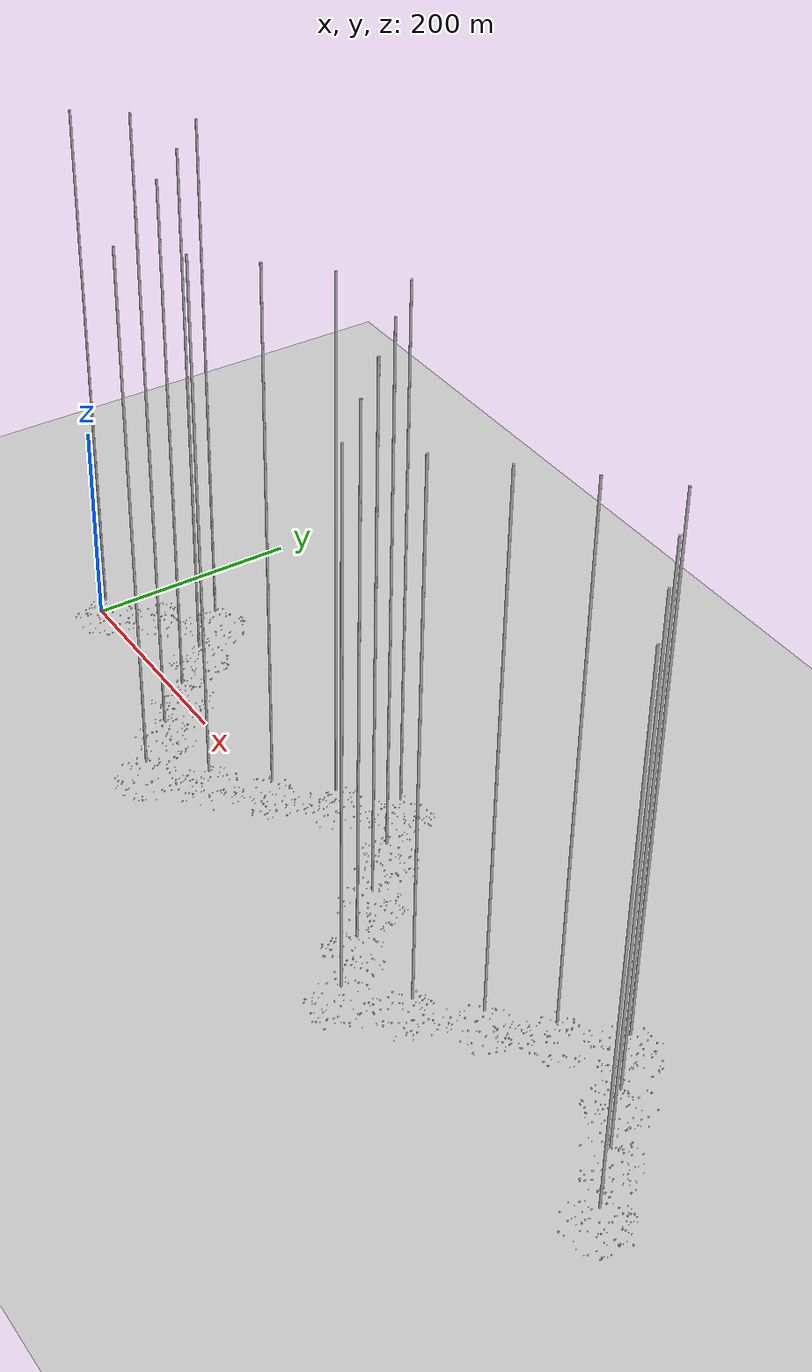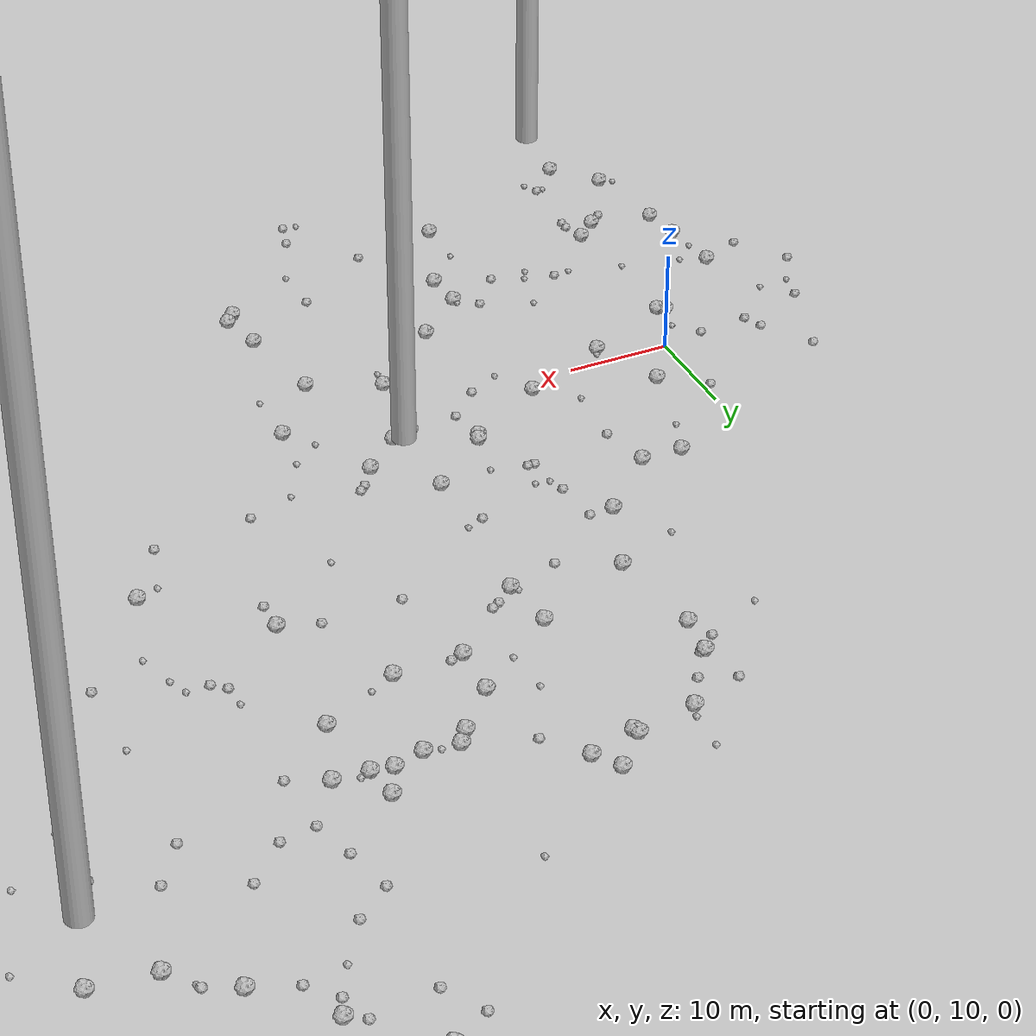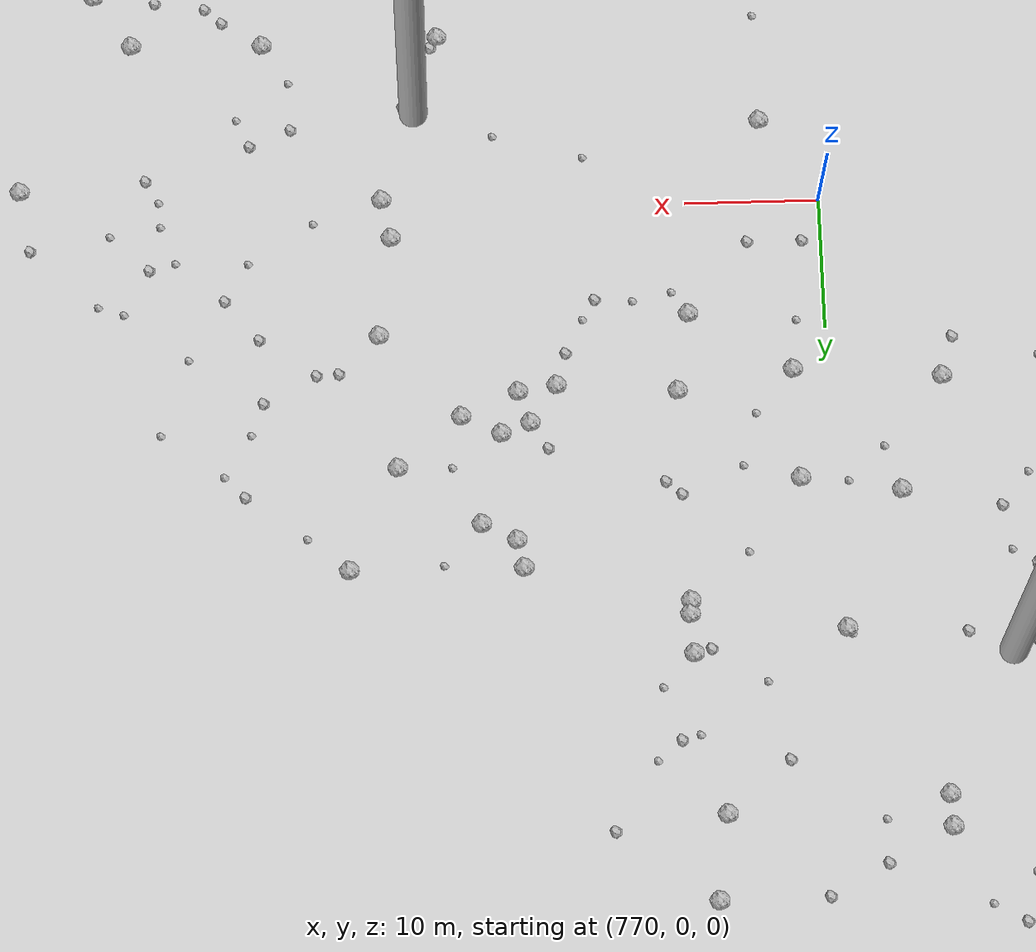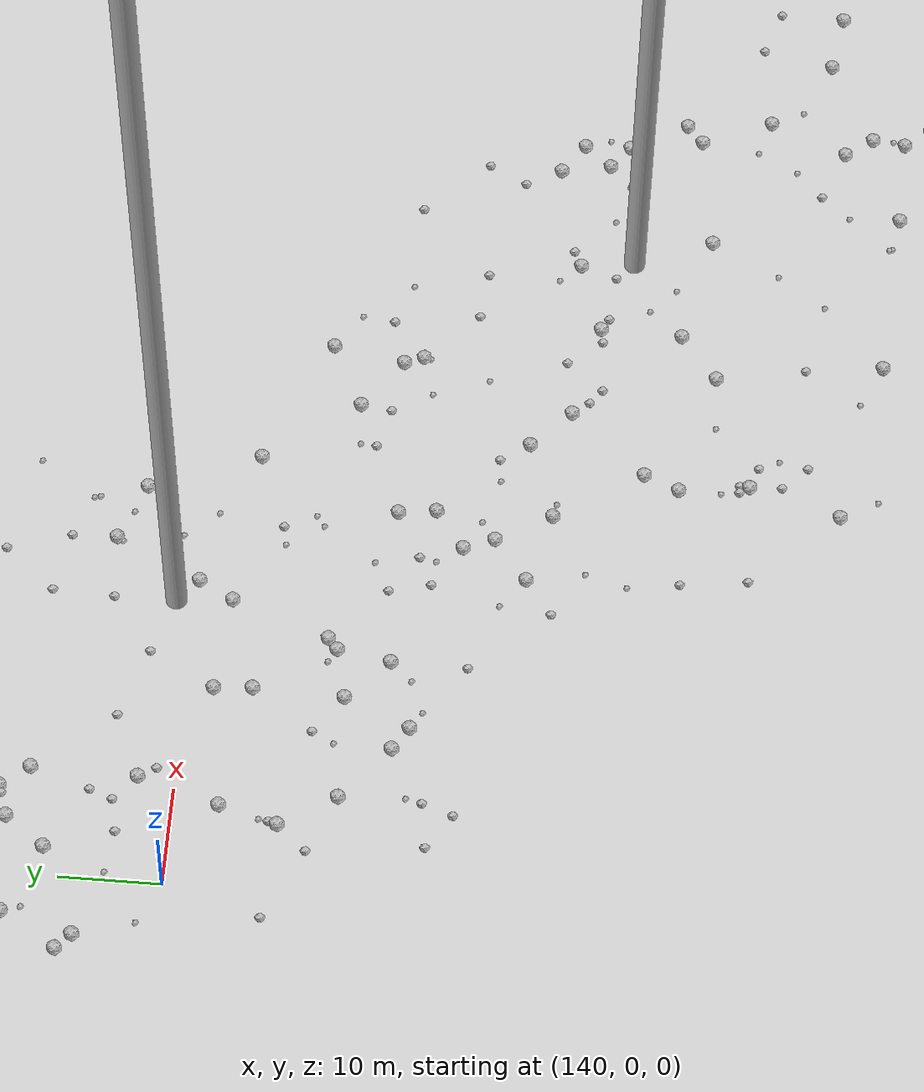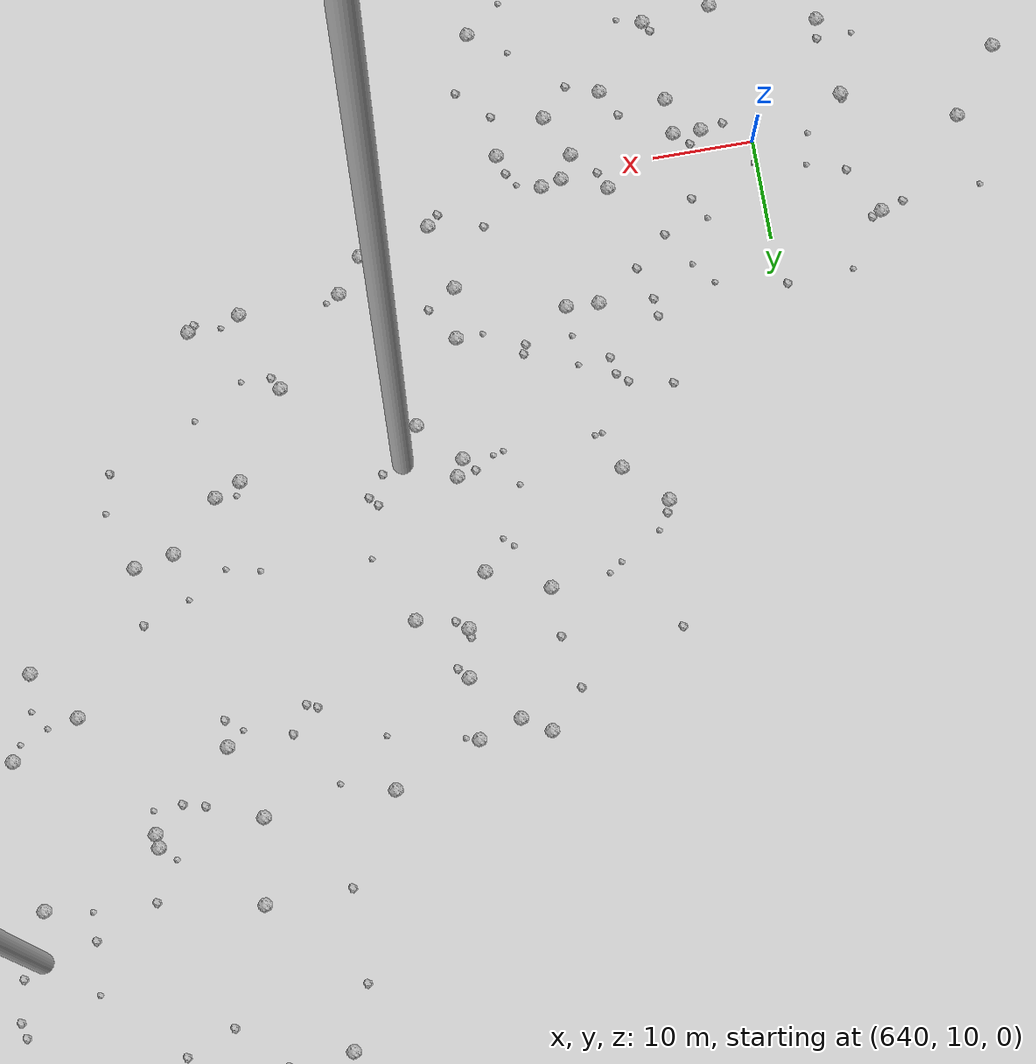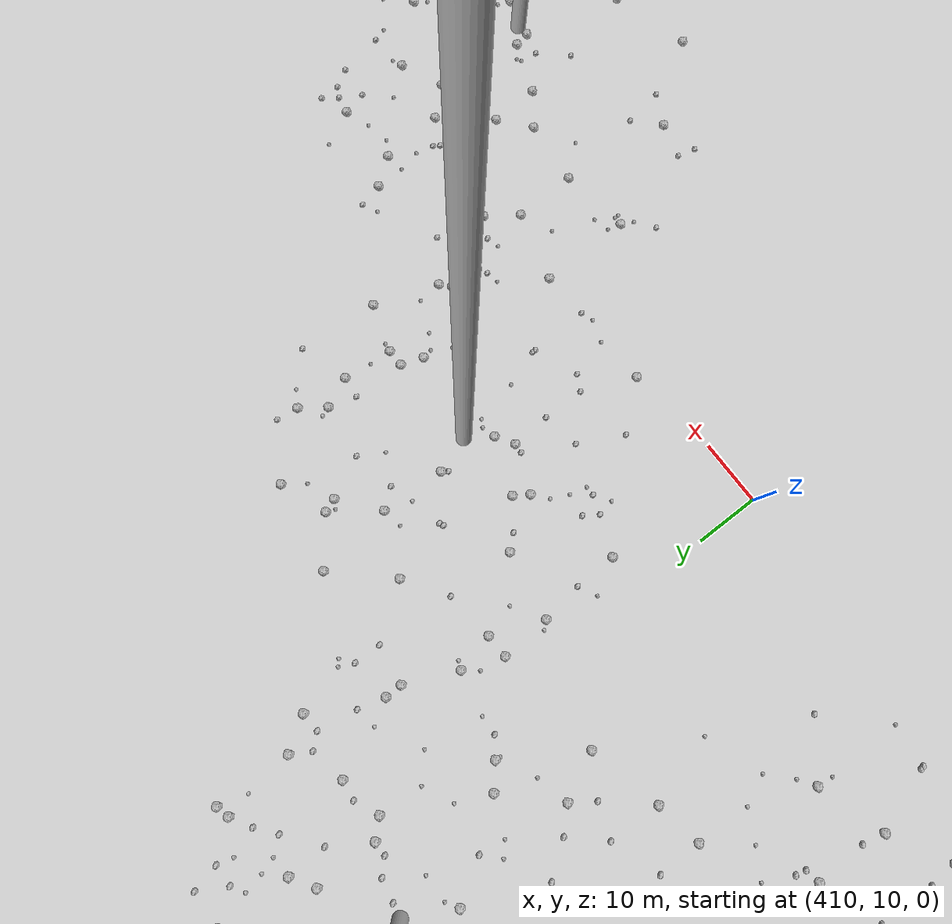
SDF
<sdf version="1.6">
 <world name="default">
  <include><uri>model://custom_ground</uri></include>
  <include><uri>model://sun</uri></include>
  <spherical_coordinates>
   <surface_model>EARTH_WGS84</surface_model>
   <latitude_deg>38.161479</latitude_deg>
   <longitude_deg>-122.454630</longitude_deg>
   <elevation>488.0</elevation>
   <heading_deg>90</heading_deg>
  </spherical_coordinates>
  <model name="rock1_0_0">
   <include><uri>model://rock1</uri><pose>-11.043193648731185 -2.0962077676405 0.5 0 0 0</pose></include>
  </model>
  <model name="rock1_0_1">
   <include><uri>model://rock1</uri><pose>35.59353807252119 -12.455169615343312 0.5 0 0 0</pose></include>
  </model>
  <model name="rock1_0_2">
   <include><uri>model://rock1</uri><pose>7.004736959455823 26.155036196943975 0.5 0 0 0</pose></include>
  </model>
  <model name="rock1_0_3">
   <include><uri>model://rock1</uri><pose>-4.830062165430748 -25.010936530134387 0.5 0 0 0</pose></include>
  </model>
  <model name="rock1_0_4">
   <include><uri>model://rock1</uri><pose>15.091161657603472 -5.873749004631957 0.5 0 0 0</pose></include>
  </model>
  <model name="rock1_0_5">
   <include><uri>model://rock1</uri><pose>-3.788531161545361 -13.311992575420327 0.5 0 0 0</pose></include>
  </model>
  <model name="rock1_0_6">
   <include><uri>model://rock1</uri><pose>-1.6683421701841255 -11.352003723324572 0.5 0 0 0</pose></include>
  </model>
  <model name="rock1_0_7">
   <include><uri>model://rock1</uri><pose>28.9095089700509 21.928321739848144 0.5 0 0 0</pose></include>
  </model>
  <model name="rock1_0_8">
   <include><uri>model://rock1</uri><pose>33.590924979391055 16.92299865013758 0.5 0 0 0</pose></include>
  </model>
  <model name="rock1_0_9">
   <include><uri>model://rock1</uri><pose>6.379599427411581 8.019061007117855 0.5 0 0 0</pose></include>
  </model>
  <model name="rock1_0_10">
   <include><uri>model://rock1</uri><pose>-9.847152490482408 -12.022939795775969 0.5 0 0 0</pose></include>
  </model>
  <model name="rock1_0_11">
   <include><uri>model://rock1</uri><pose>15.386468537609169 -9.767075057287833 0.5 0 0 0</pose></include>
  </model>
  <model name="rock1_0_12">
   <include><uri>model://rock1</uri><pose>-10.372069256988999 -8.080129531145573 0.5 0 0 0</pose></include>
  </model>
  <model name="rock1_0_13">
   <include><uri>model://rock1</uri><pose>14.966417661892194 11.727044940850618 0.5 0 0 0</pose></include>
  </model>
  <model name="rock1_0_14">
   <include><uri>model://rock1</uri><pose>11.91547099026318 -18.68268677444289 0.5 0 0 0</pose></include>
  </model>
  <model name="rock1_0_15">
   <include><uri>model://rock1</uri><pose>35.48495398177365 -7.070373716148779 0.5 0 0 0</pose></include>
  </model>
  <model name="rock1_0_16">
   <include><uri>model://rock1</uri><pose>-2.8411706771260583 4.559170402952127 0.5 0 0 0</pose></include>
  </model>
  <model name="rock1_0_17">
   <include><uri>model://rock1</uri><pose>38.730434626658166 8.55224182141523 0.5 0 0 0</pose></include>
  </model>
  <model name="rock1_0_18">
   <include><uri>model://rock1</uri><pose>3.5430061210683377 14.886961345189277 0.5 0 0 0</pose></include>
  </model>
  <model name="rock1_0_19">
   <include><uri>model://rock1</uri><pose>28.0213437419104 13.053415796749356 0.5 0 0 0</pose></include>
  </model>
  <model name="rock1_0_20">
   <include><uri>model://rock1</uri><pose>27.22222847097784 5.012601232344082 0.5 0 0 0</pose></include>
  </model>
  <model name="rock1_0_21">
   <include><uri>model://rock1</uri><pose>19.957481522521846 -1.4791337427152662 0.5 0 0 0</pose></include>
  </model>
  <model name="rock1_0_22">
   <include><uri>model://rock1</uri><pose>-2.14441062394004 4.1044256974413855 0.5 0 0 0</pose></include>
  </model>
  <model name="rock1_0_23">
   <include><uri>model://rock1</uri><pose>33.81743605116942 2.0255720460307245 0.5 0 0 0</pose></include>
  </model>
  <model name="rock1_0_24">
   <include><uri>model://rock1</uri><pose>36.50347858741454 -11.372680909043694 0.5 0 0 0</pose></include>
  </model>
  <model name="rock1_0_25">
   <include><uri>model://rock1</uri><pose>-8.431675755764921 -20.71212614425719 0.5 0 0 0</pose></include>
  </model>
  <model name="rock1_0_26">
   <include><uri>model://rock1</uri><pose>10.933469997494495 26.018235014002336 0.5 0 0 0</pose></include>
  </model>
  <model name="rock2_0_0">
   <include><uri>model://rock2</uri><pose>20.200436534535186 9.580724021214621 0.3 0 0 0</pose></include>
  </model>
  <model name="rock2_0_1">
   <include><uri>model://rock2</uri><pose>-4.1346171385672505 9.514864136735795 0.3 0 0 0</pose></include>
  </model>
  <model name="rock2_0_2">
   <include><uri>model://rock2</uri><pose>-15.799747396772348 7.29622076650287 0.3 0 0 0</pose></include>
  </model>
  <model name="rock2_0_3">
   <include><uri>model://rock2</uri><pose>-0.6195327107183317 17.81106846297294 0.3 0 0 0</pose></include>
  </model>
  <model name="rock2_0_4">
   <include><uri>model://rock2</uri><pose>-15.138236212089737 -3.8139051106960125 0.3 0 0 0</pose></include>
  </model>
  <model name="rock2_0_5">
   <include><uri>model://rock2</uri><pose>11.92590675113869 21.081544209414872 0.3 0 0 0</pose></include>
  </model>
  <model name="rock2_0_6">
   <include><uri>model://rock2</uri><pose>20.29967773837882 -17.208620503621816 0.3 0 0 0</pose></include>
  </model>
  <model name="rock2_0_7">
   <include><uri>model://rock2</uri><pose>-5.215382682406386 -14.532319930742023 0.3 0 0 0</pose></include>
  </model>
  <model name="rock2_0_8">
   <include><uri>model://rock2</uri><pose>12.964778334202613 -4.164993385564628 0.3 0 0 0</pose></include>
  </model>
  <model name="rock2_0_9">
   <include><uri>model://rock2</uri><pose>-1.1334327506293107 -13.711722882671566 0.3 0 0 0</pose></include>
  </model>
  <model name="rock2_0_10">
   <include><uri>model://rock2</uri><pose>-9.135359344005456 9.108198959215358 0.3 0 0 0</pose></include>
  </model>
  <model name="rock2_0_11">
   <include><uri>model://rock2</uri><pose>25.048200511157717 -25.752221188692697 0.3 0 0 0</pose></include>
  </model>
  <model name="rock2_0_12">
   <include><uri>model://rock2</uri><pose>28.14017477568928 -11.662689219534904 0.3 0 0 0</pose></include>
  </model>
  <model name="rock2_0_13">
   <include><uri>model://rock2</uri><pose>-9.891153156628768 10.96097742896373 0.3 0 0 0</pose></include>
  </model>
  <model name="rock2_0_14">
   <include><uri>model://rock2</uri><pose>12.58225717389901 -26.885769264374723 0.3 0 0 0</pose></include>
  </model>
  <model name="rock2_0_15">
   <include><uri>model://rock2</uri><pose>23.189603498708337 12.569901752445787 0.3 0 0 0</pose></include>
  </model>
  <model name="rock2_0_16">
   <include><uri>model://rock2</uri><pose>-1.6986790049198994 -21.69076378361192 0.3 0 0 0</pose></include>
  </model>
  <model name="rock2_0_17">
   <include><uri>model://rock2</uri><pose>27.866711755005568 10.228542457527979 0.3 0 0 0</pose></include>
  </model>
  <model name="rock2_0_18">
   <include><uri>model://rock2</uri><pose>-12.978802111335332 15.66014541744677 0.3 0 0 0</pose></include>
  </model>
  <model name="rock2_0_19">
   <include><uri>model://rock2</uri><pose>23.817987754932503 -0.18425884651627555 0.3 0 0 0</pose></include>
  </model>
  <model name="rock2_0_20">
   <include><uri>model://rock2</uri><pose>-1.1521543413473871 -14.666573984769451 0.3 0 0 0</pose></include>
  </model>
  <model name="rock2_0_21">
   <include><uri>model://rock2</uri><pose>10.040249922829055 -7.837775049696813 0.3 0 0 0</pose></include>
  </model>
  <model name="rock2_0_22">
   <include><uri>model://rock2</uri><pose>25.806691692220745 -22.892668244362227 0.3 0 0 0</pose></include>
  </model>
  <model name="rock2_0_23">
   <include><uri>model://rock2</uri><pose>19.36539544053754 27.03245134110516 0.3 0 0 0</pose></include>
  </model>
  <model name="rock2_0_24">
   <include><uri>model://rock2</uri><pose>4.04088231392889 -5.848069302282848 0.3 0 0 0</pose></include>
  </model>
  <model name="rock2_0_25">
   <include><uri>model://rock2</uri><pose>20.60392526861473 22.46269298165052 0.3 0 0 0</pose></include>
  </model>
  <model name="rock2_0_26">
   <include><uri>model://rock2</uri><pose>-18.564228769910642 1.0336384612223029 0.3 0 0 0</pose></include>
  </model>
  <model name="rock3_0_0">
   <include><uri>model://rock3</uri><pose>-13.447465586366969 4.6127901840038135 0.2 0 0 0</pose></include>
  </model>
  <model name="rock3_0_1">
   <include><uri>model://rock3</uri><pose>11.339170182414872 14.678979273207027 0.2 0 0 0</pose></include>
  </model>
  <model name="rock3_0_2">
   <include><uri>model://rock3</uri><pose>-16.493540497548963 4.4597305579063615 0.2 0 0 0</pose></include>
  </model>
  <model name="rock3_0_3">
   <include><uri>model://rock3</uri><pose>28.25898831957062 -16.755656233215028 0.2 0 0 0</pose></include>
  </model>
  <model name="rock3_0_4">
   <include><uri>model://rock3</uri><pose>-8.761477712335408 -3.36909785447855 0.2 0 0 0</pose></include>
  </model>
  <model name="rock3_0_5">
   <include><uri>model://rock3</uri><pose>23.814827243378033 21.521879860616885 0.2 0 0 0</pose></include>
  </model>
  <model name="rock3_0_6">
   <include><uri>model://rock3</uri><pose>20.337679171688507 -5.197568361773431 0.2 0 0 0</pose></include>
  </model>
  <model name="rock3_0_7">
   <include><uri>model://rock3</uri><pose>-2.2430786233445197 7.1684254015518505 0.2 0 0 0</pose></include>
  </model>
  <model name="rock3_0_8">
   <include><uri>model://rock3</uri><pose>-2.9363101195152232 -4.700438382475291 0.2 0 0 0</pose></include>
  </model>
  <model name="rock3_0_9">
   <include><uri>model://rock3</uri><pose>14.813896692297426 -5.436089904791931 0.2 0 0 0</pose></include>
  </model>
  <model name="rock3_0_10">
   <include><uri>model://rock3</uri><pose>6.894858059259835 -6.682837811064214 0.2 0 0 0</pose></include>
  </model>
  <model name="rock3_0_11">
   <include><uri>model://rock3</uri><pose>-1.072361303063154 -23.279806521858788 0.2 0 0 0</pose></include>
  </model>
  <model name="rock3_0_12">
   <include><uri>model://rock3</uri><pose>5.374692288962773 22.220523340538477 0.2 0 0 0</pose></include>
  </model>
  <model name="rock3_0_13">
   <include><uri>model://rock3</uri><pose>26.83311127683082 2.895477086049489 0.2 0 0 0</pose></include>
  </model>
  <model name="rock3_0_14">
   <include><uri>model://rock3</uri><pose>2.316651446505933 -6.125851485074286 0.2 0 0 0</pose></include>
  </model>
  <model name="rock3_0_15">
   <include><uri>model://rock3</uri><pose>11.729310082559405 -13.750714870273434 0.2 0 0 0</pose></include>
  </model>
  <model name="rock3_0_16">
   <include><uri>model://rock3</uri><pose>16.995353512760815 7.842751775037279 0.2 0 0 0</pose></include>
  </model>
  <model name="rock3_0_17">
   <include><uri>model://rock3</uri><pose>23.575871820071185 -25.786652186914818 0.2 0 0 0</pose></include>
  </model>
  <model name="rock3_0_18">
   <include><uri>model://rock3</uri><pose>-10.890213249755485 -5.394049436683414 0.2 0 0 0</pose></include>
  </model>
  <model name="rock3_0_19">
   <include><uri>model://rock3</uri><pose>6.277645106999902 -7.880902772161132 0.2 0 0 0</pose></include>
  </model>
  <model name="rock3_0_20">
   <include><uri>model://rock3</uri><pose>38.64409232161198 2.7694068742992 0.2 0 0 0</pose></include>
  </model>
  <model name="rock3_0_21">
   <include><uri>model://rock3</uri><pose>24.664502740471484 2.894468693837709 0.2 0 0 0</pose></include>
  </model>
  <model name="rock3_0_22">
   <include><uri>model://rock3</uri><pose>6.622055237427272 8.603136094713165 0.2 0 0 0</pose></include>
  </model>
  <model name="rock3_0_23">
   <include><uri>model://rock3</uri><pose>-9.873802433415664 -20.30728232852038 0.2 0 0 0</pose></include>
  </model>
  <model name="rock3_0_24">
   <include><uri>model://rock3</uri><pose>8.026725017200814 -2.250712774140581 0.2 0 0 0</pose></include>
  </model>
  <model name="rock3_0_25">
   <include><uri>model://rock3</uri><pose>23.036575510626214 -0.30236718133622986 0.2 0 0 0</pose></include>
  </model>
  <model name="rock3_0_26">
   <include><uri>model://rock3</uri><pose>-2.5254250011548613 -21.92596774375189 0.2 0 0 0</pose></include>
  </model>
  <model name="rock1_1_0">
   <include><uri>model://rock1</uri><pose>41.86436099339808 54.45187857606464 0.5 0 0 0</pose></include>
  </model>
  <model name="rock1_1_1">
   <include><uri>model://rock1</uri><pose>37.27265351204062 49.19458334442494 0.5 0 0 0</pose></include>
  </model>
  <model name="rock1_1_2">
   <include><uri>model://rock1</uri><pose>18.38487882444749 48.44841905592338 0.5 0 0 0</pose></include>
  </model>
  <model name="rock1_1_3">
   <include><uri>model://rock1</uri><pose>40.84367409731701 53.0671278624103 0.5 0 0 0</pose></include>
  </model>
  <model name="rock1_1_4">
   <include><uri>model://rock1</uri><pose>37.09490862350991 44.36449252420032 0.5 0 0 0</pose></include>
  </model>
  <model name="rock1_1_5">
   <include><uri>model://rock1</uri><pose>58.77937739023694 26.037272601109212 0.5 0 0 0</pose></include>
  </model>
  <model name="rock1_1_6">
   <include><uri>model://rock1</uri><pose>28.620719428738898 59.22440981664665 0.5 0 0 0</pose></include>
  </model>
  <model name="rock1_1_7">
   <include><uri>model://rock1</uri><pose>33.202115729501415 60.02605235824768 0.5 0 0 0</pose></include>
  </model>
  <model name="rock1_1_8">
   <include><uri>model://rock1</uri><pose>43.335066652038435 44.37413672845375 0.5 0 0 0</pose></include>
  </model>
  <model name="rock1_1_9">
   <include><uri>model://rock1</uri><pose>29.942035613966578 13.552274118966288 0.5 0 0 0</pose></include>
  </model>
  <model name="rock1_1_10">
   <include><uri>model://rock1</uri><pose>47.71065281760711 54.7402293049427 0.5 0 0 0</pose></include>
  </model>
  <model name="rock1_1_11">
   <include><uri>model://rock1</uri><pose>18.918838318911995 52.35700981881176 0.5 0 0 0</pose></include>
  </model>
  <model name="rock1_1_12">
   <include><uri>model://rock1</uri><pose>29.08499164498818 43.13459157473027 0.5 0 0 0</pose></include>
  </model>
  <model name="rock1_1_13">
   <include><uri>model://rock1</uri><pose>22.925433439928042 16.89489791115154 0.5 0 0 0</pose></include>
  </model>
  <model name="rock1_1_14">
   <include><uri>model://rock1</uri><pose>22.667952908372445 16.25673269399814 0.5 0 0 0</pose></include>
  </model>
  <model name="rock1_1_15">
   <include><uri>model://rock1</uri><pose>31.643333421803714 62.28882710612343 0.5 0 0 0</pose></include>
  </model>
  <model name="rock1_1_16">
   <include><uri>model://rock1</uri><pose>28.851164926692938 58.749279771150064 0.5 0 0 0</pose></include>
  </model>
  <model name="rock1_1_17">
   <include><uri>model://rock1</uri><pose>23.02816770910977 58.140604540299485 0.5 0 0 0</pose></include>
  </model>
  <model name="rock1_1_18">
   <include><uri>model://rock1</uri><pose>44.940742037463494 54.01848780636612 0.5 0 0 0</pose></include>
  </model>
  <model name="rock1_1_19">
   <include><uri>model://rock1</uri><pose>52.75810473216871 54.16358989611153 0.5 0 0 0</pose></include>
  </model>
  <model name="rock1_1_20">
   <include><uri>model://rock1</uri><pose>19.706462220071987 39.13059520840821 0.5 0 0 0</pose></include>
  </model>
  <model name="rock1_1_21">
   <include><uri>model://rock1</uri><pose>49.55853830072281 34.43818709799832 0.5 0 0 0</pose></include>
  </model>
  <model name="rock1_1_22">
   <include><uri>model://rock1</uri><pose>49.140555711613494 57.5478415845743 0.5 0 0 0</pose></include>
  </model>
  <model name="rock1_1_23">
   <include><uri>model://rock1</uri><pose>50.5892286607323 47.88223468163764 0.5 0 0 0</pose></include>
  </model>
  <model name="rock1_1_24">
   <include><uri>model://rock1</uri><pose>16.699763764282526 31.57402798503569 0.5 0 0 0</pose></include>
  </model>
  <model name="rock1_1_25">
   <include><uri>model://rock1</uri><pose>29.745895443753223 37.99379454518049 0.5 0 0 0</pose></include>
  </model>
  <model name="rock1_1_26">
   <include><uri>model://rock1</uri><pose>49.6267255345459 54.39934515200872 0.5 0 0 0</pose></include>
  </model>
  <model name="rock2_1_0">
   <include><uri>model://rock2</uri><pose>45.98382905328116 19.319665639375756 0.3 0 0 0</pose></include>
  </model>
  <model name="rock2_1_1">
   <include><uri>model://rock2</uri><pose>49.51518513598337 31.453743507638347 0.3 0 0 0</pose></include>
  </model>
  <model name="rock2_1_2">
   <include><uri>model://rock2</uri><pose>17.978962783047194 56.455201610141955 0.3 0 0 0</pose></include>
  </model>
  <model name="rock2_1_3">
   <include><uri>model://rock2</uri><pose>32.2484855987542 39.835180026114806 0.3 0 0 0</pose></include>
  </model>
  <model name="rock2_1_4">
   <include><uri>model://rock2</uri><pose>17.362291159379133 50.801088344393214 0.3 0 0 0</pose></include>
  </model>
  <model name="rock2_1_5">
   <include><uri>model://rock2</uri><pose>66.12273849568814 35.94318213882505 0.3 0 0 0</pose></include>
  </model>
  <model name="rock2_1_6">
   <include><uri>model://rock2</uri><pose>31.4673845211908 39.365667024243564 0.3 0 0 0</pose></include>
  </model>
  <model name="rock2_1_7">
   <include><uri>model://rock2</uri><pose>19.95355057723598 22.488647595811287 0.3 0 0 0</pose></include>
  </model>
  <model name="rock2_1_8">
   <include><uri>model://rock2</uri><pose>35.04180932672081 19.05389439418787 0.3 0 0 0</pose></include>
  </model>
  <model name="rock2_1_9">
   <include><uri>model://rock2</uri><pose>36.00677962426614 56.43537900709149 0.3 0 0 0</pose></include>
  </model>
  <model name="rock2_1_10">
   <include><uri>model://rock2</uri><pose>27.65446294095719 27.969358035135926 0.3 0 0 0</pose></include>
  </model>
  <model name="rock2_1_11">
   <include><uri>model://rock2</uri><pose>53.499871419511656 66.56399911256986 0.3 0 0 0</pose></include>
  </model>
  <model name="rock2_1_12">
   <include><uri>model://rock2</uri><pose>56.06156980562518 52.51395098748915 0.3 0 0 0</pose></include>
  </model>
  <model name="rock2_1_13">
   <include><uri>model://rock2</uri><pose>18.937235167058276 31.515416425604347 0.3 0 0 0</pose></include>
  </model>
  <model name="rock2_1_14">
   <include><uri>model://rock2</uri><pose>24.82759961137779 36.501002910824795 0.3 0 0 0</pose></include>
  </model>
  <model name="rock2_1_15">
   <include><uri>model://rock2</uri><pose>54.57332626216369 62.222855940428126 0.3 0 0 0</pose></include>
  </model>
  <model name="rock2_1_16">
   <include><uri>model://rock2</uri><pose>21.075545940589762 55.166680358512004 0.3 0 0 0</pose></include>
  </model>
  <model name="rock2_1_17">
   <include><uri>model://rock2</uri><pose>45.96531010688066 35.596595108744566 0.3 0 0 0</pose></include>
  </model>
  <model name="rock2_1_18">
   <include><uri>model://rock2</uri><pose>58.90543133870412 58.79978658351671 0.3 0 0 0</pose></include>
  </model>
  <model name="rock2_1_19">
   <include><uri>model://rock2</uri><pose>35.66911303181958 19.672091604685733 0.3 0 0 0</pose></include>
  </model>
  <model name="rock2_1_20">
   <include><uri>model://rock2</uri><pose>55.98209562845823 40.1968745608944 0.3 0 0 0</pose></include>
  </model>
  <model name="rock2_1_21">
   <include><uri>model://rock2</uri><pose>55.14339874323216 20.038279509108484 0.3 0 0 0</pose></include>
  </model>
  <model name="rock2_1_22">
   <include><uri>model://rock2</uri><pose>57.1627549676723 39.18962516895145 0.3 0 0 0</pose></include>
  </model>
  <model name="rock2_1_23">
   <include><uri>model://rock2</uri><pose>38.23118678743005 44.649860735666884 0.3 0 0 0</pose></include>
  </model>
  <model name="rock2_1_24">
   <include><uri>model://rock2</uri><pose>19.31993207086997 52.38659273557511 0.3 0 0 0</pose></include>
  </model>
  <model name="rock2_1_25">
   <include><uri>model://rock2</uri><pose>38.610609646006495 35.48687929217277 0.3 0 0 0</pose></include>
  </model>
  <model name="rock2_1_26">
   <include><uri>model://rock2</uri><pose>55.717813108475895 58.348267872920744 0.3 0 0 0</pose></include>
  </model>
  <model name="rock3_1_0">
   <include><uri>model://rock3</uri><pose>41.40964243135929 68.61188200064477 0.2 0 0 0</pose></include>
  </model>
  <model name="rock3_1_1">
   <include><uri>model://rock3</uri><pose>18.64358532165398 51.42986173313112 0.2 0 0 0</pose></include>
  </model>
  <model name="rock3_1_2">
   <include><uri>model://rock3</uri><pose>19.78430952526191 25.330313640038245 0.2 0 0 0</pose></include>
  </model>
  <model name="rock3_1_3">
   <include><uri>model://rock3</uri><pose>59.157028472320874 39.0531211228682 0.2 0 0 0</pose></include>
  </model>
  <model name="rock3_1_4">
   <include><uri>model://rock3</uri><pose>65.84006635094637 43.75973676872452 0.2 0 0 0</pose></include>
  </model>
  <model name="rock3_1_5">
   <include><uri>model://rock3</uri><pose>36.506352758343134 11.143714787605706 0.2 0 0 0</pose></include>
  </model>
  <model name="rock3_1_6">
   <include><uri>model://rock3</uri><pose>23.632640900054298 62.92279057148425 0.2 0 0 0</pose></include>
  </model>
  <model name="rock3_1_7">
   <include><uri>model://rock3</uri><pose>33.3992748727621 46.33596009676462 0.2 0 0 0</pose></include>
  </model>
  <model name="rock3_1_8">
   <include><uri>model://rock3</uri><pose>29.24514902028445 28.564614690084362 0.2 0 0 0</pose></include>
  </model>
  <model name="rock3_1_9">
   <include><uri>model://rock3</uri><pose>41.51758253744221 17.724158998149328 0.2 0 0 0</pose></include>
  </model>
  <model name="rock3_1_10">
   <include><uri>model://rock3</uri><pose>56.62682823685947 25.143118300115326 0.2 0 0 0</pose></include>
  </model>
  <model name="rock3_1_11">
   <include><uri>model://rock3</uri><pose>50.44570174307793 54.585046389134725 0.2 0 0 0</pose></include>
  </model>
  <model name="rock3_1_12">
   <include><uri>model://rock3</uri><pose>39.18521448007792 13.255834674328927 0.2 0 0 0</pose></include>
  </model>
  <model name="rock3_1_13">
   <include><uri>model://rock3</uri><pose>33.0007400672112 50.544058175515005 0.2 0 0 0</pose></include>
  </model>
  <model name="rock3_1_14">
   <include><uri>model://rock3</uri><pose>60.98308954080556 33.778133302241656 0.2 0 0 0</pose></include>
  </model>
  <model name="rock3_1_15">
   <include><uri>model://rock3</uri><pose>68.57554693294333 34.385545743594534 0.2 0 0 0</pose></include>
  </model>
  <model name="rock3_1_16">
   <include><uri>model://rock3</uri><pose>55.72454108719268 42.33414844344872 0.2 0 0 0</pose></include>
  </model>
  <model name="rock3_1_17">
   <include><uri>model://rock3</uri><pose>29.11915509920659 38.34791448116558 0.2 0 0 0</pose></include>
  </model>
  <model name="rock3_1_18">
   <include><uri>model://rock3</uri><pose>45.5837596083628 45.37312268781184 0.2 0 0 0</pose></include>
  </model>
  <model name="rock3_1_19">
   <include><uri>model://rock3</uri><pose>36.538955410985466 48.86377718493663 0.2 0 0 0</pose></include>
  </model>
  <model name="rock3_1_20">
   <include><uri>model://rock3</uri><pose>59.885376427875315 37.26324149893516 0.2 0 0 0</pose></include>
  </model>
  <model name="rock3_1_21">
   <include><uri>model://rock3</uri><pose>21.101512487678026 25.143541679720762 0.2 0 0 0</pose></include>
  </model>
  <model name="rock3_1_22">
   <include><uri>model://rock3</uri><pose>43.397398344471334 54.19410933054871 0.2 0 0 0</pose></include>
  </model>
  <model name="rock3_1_23">
   <include><uri>model://rock3</uri><pose>23.37971428638049 59.25741304033573 0.2 0 0 0</pose></include>
  </model>
  <model name="rock3_1_24">
   <include><uri>model://rock3</uri><pose>11.812039472424855 48.16660367605715 0.2 0 0 0</pose></include>
  </model>
  <model name="rock3_1_25">
   <include><uri>model://rock3</uri><pose>13.565785700574043 36.64927883676243 0.2 0 0 0</pose></include>
  </model>
  <model name="rock3_1_26">
   <include><uri>model://rock3</uri><pose>41.97307147727136 28.088590157924475 0.2 0 0 0</pose></include>
  </model>
  <model name="rock1_2_0">
   <include><uri>model://rock1</uri><pose>64.91061264664717 85.78893059337163 0.5 0 0 0</pose></include>
  </model>
  <model name="rock1_2_1">
   <include><uri>model://rock1</uri><pose>66.7586148505093 71.86633101826209 0.5 0 0 0</pose></include>
  </model>
  <model name="rock1_2_2">
   <include><uri>model://rock1</uri><pose>71.5847383686043 67.85991768263372 0.5 0 0 0</pose></include>
  </model>
  <model name="rock1_2_3">
   <include><uri>model://rock1</uri><pose>77.11667322917802 67.16169047734874 0.5 0 0 0</pose></include>
  </model>
  <model name="rock1_2_4">
   <include><uri>model://rock1</uri><pose>86.41366023035656 76.43460045029732 0.5 0 0 0</pose></include>
  </model>
  <model name="rock1_2_5">
   <include><uri>model://rock1</uri><pose>94.09988038866179 87.4725997281345 0.5 0 0 0</pose></include>
  </model>
  <model name="rock1_2_6">
   <include><uri>model://rock1</uri><pose>84.55424969671773 107.67665450942508 0.5 0 0 0</pose></include>
  </model>
  <model name="rock1_2_7">
   <include><uri>model://rock1</uri><pose>69.5165610139506 101.37417269702378 0.5 0 0 0</pose></include>
  </model>
  <model name="rock1_2_8">
   <include><uri>model://rock1</uri><pose>66.36073911736544 81.34988379000464 0.5 0 0 0</pose></include>
  </model>
  <model name="rock1_2_9">
   <include><uri>model://rock1</uri><pose>109.83549712680512 82.65884621252681 0.5 0 0 0</pose></include>
  </model>
  <model name="rock1_2_10">
   <include><uri>model://rock1</uri><pose>64.20507487683243 93.36907740077345 0.5 0 0 0</pose></include>
  </model>
  <model name="rock1_2_11">
   <include><uri>model://rock1</uri><pose>86.0116849016024 64.1347774229187 0.5 0 0 0</pose></include>
  </model>
  <model name="rock1_2_12">
   <include><uri>model://rock1</uri><pose>91.3664664449482 64.25826476902705 0.5 0 0 0</pose></include>
  </model>
  <model name="rock1_2_13">
   <include><uri>model://rock1</uri><pose>85.9282058828766 108.25326182794154 0.5 0 0 0</pose></include>
  </model>
  <model name="rock1_2_14">
   <include><uri>model://rock1</uri><pose>83.98418379363632 105.79223106877481 0.5 0 0 0</pose></include>
  </model>
  <model name="rock1_2_15">
   <include><uri>model://rock1</uri><pose>80.43442015379524 85.33830115448595 0.5 0 0 0</pose></include>
  </model>
  <model name="rock1_2_16">
   <include><uri>model://rock1</uri><pose>69.94579660719748 96.8334240588728 0.5 0 0 0</pose></include>
  </model>
  <model name="rock1_2_17">
   <include><uri>model://rock1</uri><pose>70.35890122636604 78.91567116599839 0.5 0 0 0</pose></include>
  </model>
  <model name="rock1_2_18">
   <include><uri>model://rock1</uri><pose>55.48721889520123 83.03166323656829 0.5 0 0 0</pose></include>
  </model>
  <model name="rock1_2_19">
   <include><uri>model://rock1</uri><pose>96.37474827361571 60.79415031910122 0.5 0 0 0</pose></include>
  </model>
  <model name="rock1_2_20">
   <include><uri>model://rock1</uri><pose>103.23936556743195 96.69719779840486 0.5 0 0 0</pose></include>
  </model>
  <model name="rock1_2_21">
   <include><uri>model://rock1</uri><pose>61.50348931728159 77.40158724574187 0.5 0 0 0</pose></include>
  </model>
  <model name="rock1_2_22">
   <include><uri>model://rock1</uri><pose>58.11948105505954 100.1400378585569 0.5 0 0 0</pose></include>
  </model>
  <model name="rock1_2_23">
   <include><uri>model://rock1</uri><pose>95.84202983663772 80.24925954121672 0.5 0 0 0</pose></include>
  </model>
  <model name="rock1_2_24">
   <include><uri>model://rock1</uri><pose>100.57428624296016 98.24925196736382 0.5 0 0 0</pose></include>
  </model>
  <model name="rock1_2_25">
   <include><uri>model://rock1</uri><pose>84.1238428593291 106.88809083920718 0.5 0 0 0</pose></include>
  </model>
  <model name="rock1_2_26">
   <include><uri>model://rock1</uri><pose>80.07875236006842 108.94324140772602 0.5 0 0 0</pose></include>
  </model>
  <model name="rock2_2_0">
   <include><uri>model://rock2</uri><pose>56.38906465244868 87.31797317455252 0.3 0 0 0</pose></include>
  </model>
  <model name="rock2_2_1">
   <include><uri>model://rock2</uri><pose>68.59480325038315 59.42284867265901 0.3 0 0 0</pose></include>
  </model>
  <model name="rock2_2_2">
   <include><uri>model://rock2</uri><pose>62.286550322770736 62.14614133961794 0.3 0 0 0</pose></include>
  </model>
  <model name="rock2_2_3">
   <include><uri>model://rock2</uri><pose>55.206236221620976 96.62222688690082 0.3 0 0 0</pose></include>
  </model>
  <model name="rock2_2_4">
   <include><uri>model://rock2</uri><pose>64.16550330065955 80.31598464262942 0.3 0 0 0</pose></include>
  </model>
  <model name="rock2_2_5">
   <include><uri>model://rock2</uri><pose>73.73950958010835 50.716316206307894 0.3 0 0 0</pose></include>
  </model>
  <model name="rock2_2_6">
   <include><uri>model://rock2</uri><pose>100.91137865749575 81.59194171644504 0.3 0 0 0</pose></include>
  </model>
  <model name="rock2_2_7">
   <include><uri>model://rock2</uri><pose>56.18004417380666 95.67698963729926 0.3 0 0 0</pose></include>
  </model>
  <model name="rock2_2_8">
   <include><uri>model://rock2</uri><pose>94.77847754454308 54.47076023632713 0.3 0 0 0</pose></include>
  </model>
  <model name="rock2_2_9">
   <include><uri>model://rock2</uri><pose>56.645141799665 68.93661012624533 0.3 0 0 0</pose></include>
  </model>
  <model name="rock2_2_10">
   <include><uri>model://rock2</uri><pose>54.139377786136166 77.6785472652047 0.3 0 0 0</pose></include>
  </model>
  <model name="rock2_2_11">
   <include><uri>model://rock2</uri><pose>107.32488601327742 75.2636230311636 0.3 0 0 0</pose></include>
  </model>
  <model name="rock2_2_12">
   <include><uri>model://rock2</uri><pose>65.97684482093118 55.628264045815584 0.3 0 0 0</pose></include>
  </model>
  <model name="rock2_2_13">
   <include><uri>model://rock2</uri><pose>60.81516985137661 75.59108670508496 0.3 0 0 0</pose></include>
  </model>
  <model name="rock2_2_14">
   <include><uri>model://rock2</uri><pose>59.91016930903187 78.31468596746188 0.3 0 0 0</pose></include>
  </model>
  <model name="rock2_2_15">
   <include><uri>model://rock2</uri><pose>86.22039349547521 82.79158252731769 0.3 0 0 0</pose></include>
  </model>
  <model name="rock2_2_16">
   <include><uri>model://rock2</uri><pose>62.888835289798465 73.30041587485104 0.3 0 0 0</pose></include>
  </model>
  <model name="rock2_2_17">
   <include><uri>model://rock2</uri><pose>83.28976637959695 98.47852924124982 0.3 0 0 0</pose></include>
  </model>
  <model name="rock2_2_18">
   <include><uri>model://rock2</uri><pose>52.04901443593912 81.18188421844584 0.3 0 0 0</pose></include>
  </model>
  <model name="rock2_2_19">
   <include><uri>model://rock2</uri><pose>92.53706814299073 55.063164740666544 0.3 0 0 0</pose></include>
  </model>
  <model name="rock2_2_20">
   <include><uri>model://rock2</uri><pose>89.64162167581705 104.25826122862767 0.3 0 0 0</pose></include>
  </model>
  <model name="rock2_2_21">
   <include><uri>model://rock2</uri><pose>69.50584501597918 70.45432794090652 0.3 0 0 0</pose></include>
  </model>
  <model name="rock2_2_22">
   <include><uri>model://rock2</uri><pose>66.7567537535632 81.69851655305801 0.3 0 0 0</pose></include>
  </model>
  <model name="rock2_2_23">
   <include><uri>model://rock2</uri><pose>73.36463096688185 56.6646025274835 0.3 0 0 0</pose></include>
  </model>
  <model name="rock2_2_24">
   <include><uri>model://rock2</uri><pose>96.01562214889466 63.93790901977404 0.3 0 0 0</pose></include>
  </model>
  <model name="rock2_2_25">
   <include><uri>model://rock2</uri><pose>89.97136744426217 84.82119503770498 0.3 0 0 0</pose></include>
  </model>
  <model name="rock2_2_26">
   <include><uri>model://rock2</uri><pose>79.1795207344115 106.44533939082528 0.3 0 0 0</pose></include>
  </model>
  <model name="rock3_2_0">
   <include><uri>model://rock3</uri><pose>59.80888816722794 90.37640733418397 0.2 0 0 0</pose></include>
  </model>
  <model name="rock3_2_1">
   <include><uri>model://rock3</uri><pose>79.65697916026112 71.2623288335938 0.2 0 0 0</pose></include>
  </model>
  <model name="rock3_2_2">
   <include><uri>model://rock3</uri><pose>97.50996749461159 96.97827538451621 0.2 0 0 0</pose></include>
  </model>
  <model name="rock3_2_3">
   <include><uri>model://rock3</uri><pose>88.32316138784252 106.00067763728161 0.2 0 0 0</pose></include>
  </model>
  <model name="rock3_2_4">
   <include><uri>model://rock3</uri><pose>93.03471435731213 66.21097239940381 0.2 0 0 0</pose></include>
  </model>
  <model name="rock3_2_5">
   <include><uri>model://rock3</uri><pose>101.67047775893037 85.61631798966027 0.2 0 0 0</pose></include>
  </model>
  <model name="rock3_2_6">
   <include><uri>model://rock3</uri><pose>85.80180848165858 80.38865894446974 0.2 0 0 0</pose></include>
  </model>
  <model name="rock3_2_7">
   <include><uri>model://rock3</uri><pose>100.01080536531683 84.38858531186713 0.2 0 0 0</pose></include>
  </model>
  <model name="rock3_2_8">
   <include><uri>model://rock3</uri><pose>65.41572409453893 79.38895611241023 0.2 0 0 0</pose></include>
  </model>
  <model name="rock3_2_9">
   <include><uri>model://rock3</uri><pose>69.6438964853019 69.91621065056626 0.2 0 0 0</pose></include>
  </model>
  <model name="rock3_2_10">
   <include><uri>model://rock3</uri><pose>69.31380175507974 98.1557737853661 0.2 0 0 0</pose></include>
  </model>
  <model name="rock3_2_11">
   <include><uri>model://rock3</uri><pose>59.159889033957825 72.64527210410156 0.2 0 0 0</pose></include>
  </model>
  <model name="rock3_2_12">
   <include><uri>model://rock3</uri><pose>78.72234405109974 55.02877077313891 0.2 0 0 0</pose></include>
  </model>
  <model name="rock3_2_13">
   <include><uri>model://rock3</uri><pose>83.31916619203659 90.04094895193148 0.2 0 0 0</pose></include>
  </model>
  <model name="rock3_2_14">
   <include><uri>model://rock3</uri><pose>73.94541828225346 56.95625571299702 0.2 0 0 0</pose></include>
  </model>
  <model name="rock3_2_15">
   <include><uri>model://rock3</uri><pose>107.74095372483531 85.59006878929205 0.2 0 0 0</pose></include>
  </model>
  <model name="rock3_2_16">
   <include><uri>model://rock3</uri><pose>90.27204190079956 74.31747180271441 0.2 0 0 0</pose></include>
  </model>
  <model name="rock3_2_17">
   <include><uri>model://rock3</uri><pose>89.48963214926522 54.579437725154285 0.2 0 0 0</pose></include>
  </model>
  <model name="rock3_2_18">
   <include><uri>model://rock3</uri><pose>77.27271591363873 109.17017224873129 0.2 0 0 0</pose></include>
  </model>
  <model name="rock3_2_19">
   <include><uri>model://rock3</uri><pose>65.17297557947356 99.27191944343578 0.2 0 0 0</pose></include>
  </model>
  <model name="rock3_2_20">
   <include><uri>model://rock3</uri><pose>92.11525723912774 97.0841597775237 0.2 0 0 0</pose></include>
  </model>
  <model name="rock3_2_21">
   <include><uri>model://rock3</uri><pose>95.86463147584121 59.055937142684904 0.2 0 0 0</pose></include>
  </model>
  <model name="rock3_2_22">
   <include><uri>model://rock3</uri><pose>81.44182442517945 63.43598562217947 0.2 0 0 0</pose></include>
  </model>
  <model name="rock3_2_23">
   <include><uri>model://rock3</uri><pose>91.26115435200009 65.41033914472519 0.2 0 0 0</pose></include>
  </model>
  <model name="rock3_2_24">
   <include><uri>model://rock3</uri><pose>72.99437932610772 97.34977221185392 0.2 0 0 0</pose></include>
  </model>
  <model name="rock3_2_25">
   <include><uri>model://rock3</uri><pose>88.88522995621835 78.74165552016488 0.2 0 0 0</pose></include>
  </model>
  <model name="rock3_2_26">
   <include><uri>model://rock3</uri><pose>53.604845964175006 93.12886451841206 0.2 0 0 0</pose></include>
  </model>
  <model name="rock1_3_0">
   <include><uri>model://rock1</uri><pose>128.26611327005523 64.52321990959913 0.5 0 0 0</pose></include>
  </model>
  <model name="rock1_3_1">
   <include><uri>model://rock1</uri><pose>101.33173440022112 60.82577873688962 0.5 0 0 0</pose></include>
  </model>
  <model name="rock1_3_2">
   <include><uri>model://rock1</uri><pose>136.44631829357672 61.03088094183276 0.5 0 0 0</pose></include>
  </model>
  <model name="rock1_3_3">
   <include><uri>model://rock1</uri><pose>136.01231868336393 14.941693375905107 0.5 0 0 0</pose></include>
  </model>
  <model name="rock1_3_4">
   <include><uri>model://rock1</uri><pose>97.57792779243415 24.960668567804305 0.5 0 0 0</pose></include>
  </model>
  <model name="rock1_3_5">
   <include><uri>model://rock1</uri><pose>140.85108259008354 54.07160128072027 0.5 0 0 0</pose></include>
  </model>
  <model name="rock1_3_6">
   <include><uri>model://rock1</uri><pose>117.14078286623153 55.93020652314066 0.5 0 0 0</pose></include>
  </model>
  <model name="rock1_3_7">
   <include><uri>model://rock1</uri><pose>109.23432381569927 36.1356546845871 0.5 0 0 0</pose></include>
  </model>
  <model name="rock1_3_8">
   <include><uri>model://rock1</uri><pose>134.4526605157615 41.08302555798182 0.5 0 0 0</pose></include>
  </model>
  <model name="rock1_3_9">
   <include><uri>model://rock1</uri><pose>103.52556325922114 51.148176094977885 0.5 0 0 0</pose></include>
  </model>
  <model name="rock1_3_10">
   <include><uri>model://rock1</uri><pose>116.31111483669417 16.765052620426157 0.5 0 0 0</pose></include>
  </model>
  <model name="rock1_3_11">
   <include><uri>model://rock1</uri><pose>113.37259966809341 20.30581923062041 0.5 0 0 0</pose></include>
  </model>
  <model name="rock1_3_12">
   <include><uri>model://rock1</uri><pose>109.46360876987826 15.830170125328543 0.5 0 0 0</pose></include>
  </model>
  <model name="rock1_3_13">
   <include><uri>model://rock1</uri><pose>104.87759186056779 47.35470023886803 0.5 0 0 0</pose></include>
  </model>
  <model name="rock1_3_14">
   <include><uri>model://rock1</uri><pose>112.0934967794296 31.51734315639478 0.5 0 0 0</pose></include>
  </model>
  <model name="rock1_3_15">
   <include><uri>model://rock1</uri><pose>135.78038934554874 40.94851082209993 0.5 0 0 0</pose></include>
  </model>
  <model name="rock1_3_16">
   <include><uri>model://rock1</uri><pose>108.561264476544 66.20461512326331 0.5 0 0 0</pose></include>
  </model>
  <model name="rock1_3_17">
   <include><uri>model://rock1</uri><pose>140.7740830737425 56.879599291218696 0.5 0 0 0</pose></include>
  </model>
  <model name="rock1_3_18">
   <include><uri>model://rock1</uri><pose>95.54589344961879 47.75199124943477 0.5 0 0 0</pose></include>
  </model>
  <model name="rock1_3_19">
   <include><uri>model://rock1</uri><pose>127.86742189657 30.567838531682725 0.5 0 0 0</pose></include>
  </model>
  <model name="rock1_3_20">
   <include><uri>model://rock1</uri><pose>120.28847170627257 22.981590588614875 0.5 0 0 0</pose></include>
  </model>
  <model name="rock1_3_21">
   <include><uri>model://rock1</uri><pose>132.08145828012184 59.50728082970139 0.5 0 0 0</pose></include>
  </model>
  <model name="rock1_3_22">
   <include><uri>model://rock1</uri><pose>114.36438906373519 66.96849696854305 0.5 0 0 0</pose></include>
  </model>
  <model name="rock1_3_23">
   <include><uri>model://rock1</uri><pose>147.3856511549746 36.13390391266188 0.5 0 0 0</pose></include>
  </model>
  <model name="rock1_3_24">
   <include><uri>model://rock1</uri><pose>124.34818099098513 67.03726798760913 0.5 0 0 0</pose></include>
  </model>
  <model name="rock1_3_25">
   <include><uri>model://rock1</uri><pose>106.45706986651075 51.46792724182903 0.5 0 0 0</pose></include>
  </model>
  <model name="rock1_3_26">
   <include><uri>model://rock1</uri><pose>127.89921429496688 38.90672351260035 0.5 0 0 0</pose></include>
  </model>
  <model name="rock2_3_0">
   <include><uri>model://rock2</uri><pose>110.06851878794545 28.524157163650344 0.3 0 0 0</pose></include>
  </model>
  <model name="rock2_3_1">
   <include><uri>model://rock2</uri><pose>108.43290491895294 66.48874213350685 0.3 0 0 0</pose></include>
  </model>
  <model name="rock2_3_2">
   <include><uri>model://rock2</uri><pose>112.89343687777429 24.462670830493654 0.3 0 0 0</pose></include>
  </model>
  <model name="rock2_3_3">
   <include><uri>model://rock2</uri><pose>129.93163747722093 57.25139790102878 0.3 0 0 0</pose></include>
  </model>
  <model name="rock2_3_4">
   <include><uri>model://rock2</uri><pose>104.34660432814812 25.495779629153613 0.3 0 0 0</pose></include>
  </model>
  <model name="rock2_3_5">
   <include><uri>model://rock2</uri><pose>114.79983981515645 59.121444814811554 0.3 0 0 0</pose></include>
  </model>
  <model name="rock2_3_6">
   <include><uri>model://rock2</uri><pose>140.13250397091375 45.188110003965114 0.3 0 0 0</pose></include>
  </model>
  <model name="rock2_3_7">
   <include><uri>model://rock2</uri><pose>132.23324266226018 58.239508310125835 0.3 0 0 0</pose></include>
  </model>
  <model name="rock2_3_8">
   <include><uri>model://rock2</uri><pose>112.37334124281571 19.241371986562328 0.3 0 0 0</pose></include>
  </model>
  <model name="rock2_3_9">
   <include><uri>model://rock2</uri><pose>107.55935311300065 22.445553057391557 0.3 0 0 0</pose></include>
  </model>
  <model name="rock2_3_10">
   <include><uri>model://rock2</uri><pose>105.21586619285678 16.340587960778294 0.3 0 0 0</pose></include>
  </model>
  <model name="rock2_3_11">
   <include><uri>model://rock2</uri><pose>120.66413349535162 30.46157682387287 0.3 0 0 0</pose></include>
  </model>
  <model name="rock2_3_12">
   <include><uri>model://rock2</uri><pose>139.91422255331338 48.266376665779696 0.3 0 0 0</pose></include>
  </model>
  <model name="rock2_3_13">
   <include><uri>model://rock2</uri><pose>125.27950123405476 32.533872941633305 0.3 0 0 0</pose></include>
  </model>
  <model name="rock2_3_14">
   <include><uri>model://rock2</uri><pose>102.77914325061442 22.701805730354728 0.3 0 0 0</pose></include>
  </model>
  <model name="rock2_3_15">
   <include><uri>model://rock2</uri><pose>131.751803730457 57.17861663576914 0.3 0 0 0</pose></include>
  </model>
  <model name="rock2_3_16">
   <include><uri>model://rock2</uri><pose>96.54017575433801 45.38512931056833 0.3 0 0 0</pose></include>
  </model>
  <model name="rock2_3_17">
   <include><uri>model://rock2</uri><pose>135.60213733270308 22.294052889505842 0.3 0 0 0</pose></include>
  </model>
  <model name="rock2_3_18">
   <include><uri>model://rock2</uri><pose>142.4033177865032 28.750630994905485 0.3 0 0 0</pose></include>
  </model>
  <model name="rock2_3_19">
   <include><uri>model://rock2</uri><pose>133.81072426015857 60.68425585713819 0.3 0 0 0</pose></include>
  </model>
  <model name="rock2_3_20">
   <include><uri>model://rock2</uri><pose>103.38356814174516 35.85489156227381 0.3 0 0 0</pose></include>
  </model>
  <model name="rock2_3_21">
   <include><uri>model://rock2</uri><pose>146.6080456856883 37.94764139623001 0.3 0 0 0</pose></include>
  </model>
  <model name="rock2_3_22">
   <include><uri>model://rock2</uri><pose>133.26020375323924 49.41494128376408 0.3 0 0 0</pose></include>
  </model>
  <model name="rock2_3_23">
   <include><uri>model://rock2</uri><pose>125.55211762378113 29.007948817768117 0.3 0 0 0</pose></include>
  </model>
  <model name="rock2_3_24">
   <include><uri>model://rock2</uri><pose>131.93839852150163 38.97264641083305 0.3 0 0 0</pose></include>
  </model>
  <model name="rock2_3_25">
   <include><uri>model://rock2</uri><pose>113.77580483737994 41.62475239862 0.3 0 0 0</pose></include>
  </model>
  <model name="rock2_3_26">
   <include><uri>model://rock2</uri><pose>94.9733386499964 53.105655029590324 0.3 0 0 0</pose></include>
  </model>
  <model name="rock3_3_0">
   <include><uri>model://rock3</uri><pose>140.35330211608735 46.676168777267 0.2 0 0 0</pose></include>
  </model>
  <model name="rock3_3_1">
   <include><uri>model://rock3</uri><pose>109.59965751749033 54.15312209344149 0.2 0 0 0</pose></include>
  </model>
  <model name="rock3_3_2">
   <include><uri>model://rock3</uri><pose>107.30095852825865 19.599833682915325 0.2 0 0 0</pose></include>
  </model>
  <model name="rock3_3_3">
   <include><uri>model://rock3</uri><pose>95.76702749523011 45.12382063274663 0.2 0 0 0</pose></include>
  </model>
  <model name="rock3_3_4">
   <include><uri>model://rock3</uri><pose>99.81150221543443 49.07401799768594 0.2 0 0 0</pose></include>
  </model>
  <model name="rock3_3_5">
   <include><uri>model://rock3</uri><pose>98.91333745337417 24.983700123642222 0.2 0 0 0</pose></include>
  </model>
  <model name="rock3_3_6">
   <include><uri>model://rock3</uri><pose>139.1608275136478 39.75829042188313 0.2 0 0 0</pose></include>
  </model>
  <model name="rock3_3_7">
   <include><uri>model://rock3</uri><pose>103.19108564523299 42.381851857320235 0.2 0 0 0</pose></include>
  </model>
  <model name="rock3_3_8">
   <include><uri>model://rock3</uri><pose>141.42673575319816 44.41327849851427 0.2 0 0 0</pose></include>
  </model>
  <model name="rock3_3_9">
   <include><uri>model://rock3</uri><pose>123.67408999399171 31.427196478993846 0.2 0 0 0</pose></include>
  </model>
  <model name="rock3_3_10">
   <include><uri>model://rock3</uri><pose>107.8549681148014 60.51813352357494 0.2 0 0 0</pose></include>
  </model>
  <model name="rock3_3_11">
   <include><uri>model://rock3</uri><pose>107.75043404970263 45.692595328676674 0.2 0 0 0</pose></include>
  </model>
  <model name="rock3_3_12">
   <include><uri>model://rock3</uri><pose>141.07803899125724 48.54616093173109 0.2 0 0 0</pose></include>
  </model>
  <model name="rock3_3_13">
   <include><uri>model://rock3</uri><pose>96.70840776198384 55.545963603301985 0.2 0 0 0</pose></include>
  </model>
  <model name="rock3_3_14">
   <include><uri>model://rock3</uri><pose>93.38825105642667 31.409902987787476 0.2 0 0 0</pose></include>
  </model>
  <model name="rock3_3_15">
   <include><uri>model://rock3</uri><pose>103.5387728455664 49.13453042046641 0.2 0 0 0</pose></include>
  </model>
  <model name="rock3_3_16">
   <include><uri>model://rock3</uri><pose>146.67099998149112 31.585589122433937 0.2 0 0 0</pose></include>
  </model>
  <model name="rock3_3_17">
   <include><uri>model://rock3</uri><pose>115.49215462821664 37.7154689829687 0.2 0 0 0</pose></include>
  </model>
  <model name="rock3_3_18">
   <include><uri>model://rock3</uri><pose>142.9177978847218 22.206309776240786 0.2 0 0 0</pose></include>
  </model>
  <model name="rock3_3_19">
   <include><uri>model://rock3</uri><pose>119.18293870426058 49.58012813758008 0.2 0 0 0</pose></include>
  </model>
  <model name="rock3_3_20">
   <include><uri>model://rock3</uri><pose>129.08631648656277 28.8398178069121 0.2 0 0 0</pose></include>
  </model>
  <model name="rock3_3_21">
   <include><uri>model://rock3</uri><pose>112.49614174275995 25.29173281604512 0.2 0 0 0</pose></include>
  </model>
  <model name="rock3_3_22">
   <include><uri>model://rock3</uri><pose>106.83959470160104 15.681025658356553 0.2 0 0 0</pose></include>
  </model>
  <model name="rock3_3_23">
   <include><uri>model://rock3</uri><pose>107.86722529469584 32.25860615938821 0.2 0 0 0</pose></include>
  </model>
  <model name="rock3_3_24">
   <include><uri>model://rock3</uri><pose>133.27165479077684 27.445478708432173 0.2 0 0 0</pose></include>
  </model>
  <model name="rock3_3_25">
   <include><uri>model://rock3</uri><pose>123.29063689478174 46.29569272774987 0.2 0 0 0</pose></include>
  </model>
  <model name="rock3_3_26">
   <include><uri>model://rock3</uri><pose>127.96782763627064 29.637410128968284 0.2 0 0 0</pose></include>
  </model>
  <model name="rock1_4_0">
   <include><uri>model://rock1</uri><pose>158.26129354067945 -21.78320612349637 0.5 0 0 0</pose></include>
  </model>
  <model name="rock1_4_1">
   <include><uri>model://rock1</uri><pose>148.6461739102524 -4.36706364107064 0.5 0 0 0</pose></include>
  </model>
  <model name="rock1_4_2">
   <include><uri>model://rock1</uri><pose>170.6614396948787 -3.477260027332683 0.5 0 0 0</pose></include>
  </model>
  <model name="rock1_4_3">
   <include><uri>model://rock1</uri><pose>155.9314208944053 -20.248869676097645 0.5 0 0 0</pose></include>
  </model>
  <model name="rock1_4_4">
   <include><uri>model://rock1</uri><pose>151.15916810872514 13.928296508313295 0.5 0 0 0</pose></include>
  </model>
  <model name="rock1_4_5">
   <include><uri>model://rock1</uri><pose>142.97090112769305 11.740795903836585 0.5 0 0 0</pose></include>
  </model>
  <model name="rock1_4_6">
   <include><uri>model://rock1</uri><pose>165.20171888593103 -19.364542322768845 0.5 0 0 0</pose></include>
  </model>
  <model name="rock1_4_7">
   <include><uri>model://rock1</uri><pose>167.25838909542983 -13.126374471076208 0.5 0 0 0</pose></include>
  </model>
  <model name="rock1_4_8">
   <include><uri>model://rock1</uri><pose>150.43335827797142 -15.603983127823945 0.5 0 0 0</pose></include>
  </model>
  <model name="rock1_4_9">
   <include><uri>model://rock1</uri><pose>145.8718455640213 15.66577445789028 0.5 0 0 0</pose></include>
  </model>
  <model name="rock1_4_10">
   <include><uri>model://rock1</uri><pose>148.97669988062748 16.677405084315694 0.5 0 0 0</pose></include>
  </model>
  <model name="rock1_4_11">
   <include><uri>model://rock1</uri><pose>147.07499930409134 -10.104551856533018 0.5 0 0 0</pose></include>
  </model>
  <model name="rock1_4_12">
   <include><uri>model://rock1</uri><pose>134.21081374437435 7.968940170755097 0.5 0 0 0</pose></include>
  </model>
  <model name="rock1_4_13">
   <include><uri>model://rock1</uri><pose>172.53420132046688 -0.042582064448801304 0.5 0 0 0</pose></include>
  </model>
  <model name="rock1_4_14">
   <include><uri>model://rock1</uri><pose>151.55726224825906 22.41313985555429 0.5 0 0 0</pose></include>
  </model>
  <model name="rock1_4_15">
   <include><uri>model://rock1</uri><pose>176.6423506321098 8.508089635333292 0.5 0 0 0</pose></include>
  </model>
  <model name="rock1_4_16">
   <include><uri>model://rock1</uri><pose>148.30778269468723 17.951741223984435 0.5 0 0 0</pose></include>
  </model>
  <model name="rock1_4_17">
   <include><uri>model://rock1</uri><pose>132.63869016670853 9.4168518338766 0.5 0 0 0</pose></include>
  </model>
  <model name="rock1_4_18">
   <include><uri>model://rock1</uri><pose>181.67730218336396 -18.689762296639685 0.5 0 0 0</pose></include>
  </model>
  <model name="rock1_4_19">
   <include><uri>model://rock1</uri><pose>151.0086913722161 3.6304221369396714 0.5 0 0 0</pose></include>
  </model>
  <model name="rock1_4_20">
   <include><uri>model://rock1</uri><pose>182.52761170870244 6.1119456633797355 0.5 0 0 0</pose></include>
  </model>
  <model name="rock1_4_21">
   <include><uri>model://rock1</uri><pose>161.30253396382926 -6.350405087036808 0.5 0 0 0</pose></include>
  </model>
  <model name="rock1_4_22">
   <include><uri>model://rock1</uri><pose>186.80194784242306 -4.733416442653986 0.5 0 0 0</pose></include>
  </model>
  <model name="rock1_4_23">
   <include><uri>model://rock1</uri><pose>165.44359070745907 28.493136932793085 0.5 0 0 0</pose></include>
  </model>
  <model name="rock1_4_24">
   <include><uri>model://rock1</uri><pose>161.01019715202045 -2.6030100805419814 0.5 0 0 0</pose></include>
  </model>
  <model name="rock1_4_25">
   <include><uri>model://rock1</uri><pose>161.02748712036663 -15.249821244326762 0.5 0 0 0</pose></include>
  </model>
  <model name="rock1_4_26">
   <include><uri>model://rock1</uri><pose>166.12035820222644 -14.089738988456295 0.5 0 0 0</pose></include>
  </model>
  <model name="rock2_4_0">
   <include><uri>model://rock2</uri><pose>150.40283354445174 -23.61246532380835 0.3 0 0 0</pose></include>
  </model>
  <model name="rock2_4_1">
   <include><uri>model://rock2</uri><pose>170.38148815886584 14.129951593118065 0.3 0 0 0</pose></include>
  </model>
  <model name="rock2_4_2">
   <include><uri>model://rock2</uri><pose>149.36382234457182 -26.657483187313908 0.3 0 0 0</pose></include>
  </model>
  <model name="rock2_4_3">
   <include><uri>model://rock2</uri><pose>147.8306683793752 25.561950097805223 0.3 0 0 0</pose></include>
  </model>
  <model name="rock2_4_4">
   <include><uri>model://rock2</uri><pose>137.34720406998386 -9.46368609980382 0.3 0 0 0</pose></include>
  </model>
  <model name="rock2_4_5">
   <include><uri>model://rock2</uri><pose>137.11649656005272 17.41405536645904 0.3 0 0 0</pose></include>
  </model>
  <model name="rock2_4_6">
   <include><uri>model://rock2</uri><pose>172.95280441625954 -18.477994943447612 0.3 0 0 0</pose></include>
  </model>
  <model name="rock2_4_7">
   <include><uri>model://rock2</uri><pose>164.44448991235063 3.884213495384799 0.3 0 0 0</pose></include>
  </model>
  <model name="rock2_4_8">
   <include><uri>model://rock2</uri><pose>174.5657175607966 19.149710579810602 0.3 0 0 0</pose></include>
  </model>
  <model name="rock2_4_9">
   <include><uri>model://rock2</uri><pose>165.13539632852383 -26.83600631901075 0.3 0 0 0</pose></include>
  </model>
  <model name="rock2_4_10">
   <include><uri>model://rock2</uri><pose>170.09981913840863 8.039842267819822 0.3 0 0 0</pose></include>
  </model>
  <model name="rock2_4_11">
   <include><uri>model://rock2</uri><pose>148.42634163624817 5.788370758173137 0.3 0 0 0</pose></include>
  </model>
  <model name="rock2_4_12">
   <include><uri>model://rock2</uri><pose>157.35629695631468 6.304432973521315 0.3 0 0 0</pose></include>
  </model>
  <model name="rock2_4_13">
   <include><uri>model://rock2</uri><pose>149.28377499917673 8.057023199591946 0.3 0 0 0</pose></include>
  </model>
  <model name="rock2_4_14">
   <include><uri>model://rock2</uri><pose>173.92737763564185 -22.554304588917063 0.3 0 0 0</pose></include>
  </model>
  <model name="rock2_4_15">
   <include><uri>model://rock2</uri><pose>148.2026343452162 16.418431458790415 0.3 0 0 0</pose></include>
  </model>
  <model name="rock2_4_16">
   <include><uri>model://rock2</uri><pose>145.82857433917988 -24.284660798643994 0.3 0 0 0</pose></include>
  </model>
  <model name="rock2_4_17">
   <include><uri>model://rock2</uri><pose>176.5151976539632 12.910521577187069 0.3 0 0 0</pose></include>
  </model>
  <model name="rock2_4_18">
   <include><uri>model://rock2</uri><pose>144.55734789211027 -13.04140390698241 0.3 0 0 0</pose></include>
  </model>
  <model name="rock2_4_19">
   <include><uri>model://rock2</uri><pose>147.33801871723955 -9.236280259465591 0.3 0 0 0</pose></include>
  </model>
  <model name="rock2_4_20">
   <include><uri>model://rock2</uri><pose>149.9933395743147 19.07628574504509 0.3 0 0 0</pose></include>
  </model>
  <model name="rock2_4_21">
   <include><uri>model://rock2</uri><pose>168.05409330909677 23.924626177699167 0.3 0 0 0</pose></include>
  </model>
  <model name="rock2_4_22">
   <include><uri>model://rock2</uri><pose>152.02304480199135 1.9112367458450592 0.3 0 0 0</pose></include>
  </model>
  <model name="rock2_4_23">
   <include><uri>model://rock2</uri><pose>157.15918857437327 -12.476247191670517 0.3 0 0 0</pose></include>
  </model>
  <model name="rock2_4_24">
   <include><uri>model://rock2</uri><pose>176.85619269512864 -21.186750661663865 0.3 0 0 0</pose></include>
  </model>
  <model name="rock2_4_25">
   <include><uri>model://rock2</uri><pose>179.15554416672757 -7.66098167740758 0.3 0 0 0</pose></include>
  </model>
  <model name="rock2_4_26">
   <include><uri>model://rock2</uri><pose>145.08522855600842 5.148748327691159 0.3 0 0 0</pose></include>
  </model>
  <model name="rock3_4_0">
   <include><uri>model://rock3</uri><pose>173.98702098939103 25.764052011104198 0.2 0 0 0</pose></include>
  </model>
  <model name="rock3_4_1">
   <include><uri>model://rock3</uri><pose>177.1962267377537 -8.053307042916565 0.2 0 0 0</pose></include>
  </model>
  <model name="rock3_4_2">
   <include><uri>model://rock3</uri><pose>147.49284816023248 -8.310349930190068 0.2 0 0 0</pose></include>
  </model>
  <model name="rock3_4_3">
   <include><uri>model://rock3</uri><pose>163.2894272016413 -21.57634523020416 0.2 0 0 0</pose></include>
  </model>
  <model name="rock3_4_4">
   <include><uri>model://rock3</uri><pose>175.9665000893805 -16.91642781318081 0.2 0 0 0</pose></include>
  </model>
  <model name="rock3_4_5">
   <include><uri>model://rock3</uri><pose>176.55647319080342 -22.866314073181933 0.2 0 0 0</pose></include>
  </model>
  <model name="rock3_4_6">
   <include><uri>model://rock3</uri><pose>164.76497862615875 -13.331127688042269 0.2 0 0 0</pose></include>
  </model>
  <model name="rock3_4_7">
   <include><uri>model://rock3</uri><pose>173.36338493996666 23.112818967509128 0.2 0 0 0</pose></include>
  </model>
  <model name="rock3_4_8">
   <include><uri>model://rock3</uri><pose>180.90066175506067 11.217105399572276 0.2 0 0 0</pose></include>
  </model>
  <model name="rock3_4_9">
   <include><uri>model://rock3</uri><pose>180.1357011524431 -1.260308596239902 0.2 0 0 0</pose></include>
  </model>
  <model name="rock3_4_10">
   <include><uri>model://rock3</uri><pose>179.6153790651793 7.089923831266617 0.2 0 0 0</pose></include>
  </model>
  <model name="rock3_4_11">
   <include><uri>model://rock3</uri><pose>140.79522464580276 5.6586693888221475 0.2 0 0 0</pose></include>
  </model>
  <model name="rock3_4_12">
   <include><uri>model://rock3</uri><pose>154.16655373082048 17.886648307892465 0.2 0 0 0</pose></include>
  </model>
  <model name="rock3_4_13">
   <include><uri>model://rock3</uri><pose>169.57291388286941 22.466263731960332 0.2 0 0 0</pose></include>
  </model>
  <model name="rock3_4_14">
   <include><uri>model://rock3</uri><pose>177.39369427615998 1.987761595987969 0.2 0 0 0</pose></include>
  </model>
  <model name="rock3_4_15">
   <include><uri>model://rock3</uri><pose>181.0711534406555 10.632523933168684 0.2 0 0 0</pose></include>
  </model>
  <model name="rock3_4_16">
   <include><uri>model://rock3</uri><pose>156.03420474953256 -14.689933477915552 0.2 0 0 0</pose></include>
  </model>
  <model name="rock3_4_17">
   <include><uri>model://rock3</uri><pose>180.63461166485067 -10.808084972158639 0.2 0 0 0</pose></include>
  </model>
  <model name="rock3_4_18">
   <include><uri>model://rock3</uri><pose>150.79236813694789 -22.064247500582795 0.2 0 0 0</pose></include>
  </model>
  <model name="rock3_4_19">
   <include><uri>model://rock3</uri><pose>159.99723279964041 -22.91806369983903 0.2 0 0 0</pose></include>
  </model>
  <model name="rock3_4_20">
   <include><uri>model://rock3</uri><pose>179.52820087854013 -11.629662104857093 0.2 0 0 0</pose></include>
  </model>
  <model name="rock3_4_21">
   <include><uri>model://rock3</uri><pose>184.57459863590213 16.822717065642344 0.2 0 0 0</pose></include>
  </model>
  <model name="rock3_4_22">
   <include><uri>model://rock3</uri><pose>135.8564083326227 2.122069319389958 0.2 0 0 0</pose></include>
  </model>
  <model name="rock3_4_23">
   <include><uri>model://rock3</uri><pose>136.5884728903162 13.10073141781033 0.2 0 0 0</pose></include>
  </model>
  <model name="rock3_4_24">
   <include><uri>model://rock3</uri><pose>160.80827630757534 18.938229185097427 0.2 0 0 0</pose></include>
  </model>
  <model name="rock3_4_25">
   <include><uri>model://rock3</uri><pose>176.29876226856814 7.8833138861389145 0.2 0 0 0</pose></include>
  </model>
  <model name="rock3_4_26">
   <include><uri>model://rock3</uri><pose>150.5502740827209 19.1311163303455 0.2 0 0 0</pose></include>
  </model>
  <model name="rock1_5_0">
   <include><uri>model://rock1</uri><pose>186.45957118626959 -45.96080725400534 0.5 0 0 0</pose></include>
  </model>
  <model name="rock1_5_1">
   <include><uri>model://rock1</uri><pose>200.05504735635154 -10.69190735881076 0.5 0 0 0</pose></include>
  </model>
  <model name="rock1_5_2">
   <include><uri>model://rock1</uri><pose>199.45898699369593 -48.945656407009274 0.5 0 0 0</pose></include>
  </model>
  <model name="rock1_5_3">
   <include><uri>model://rock1</uri><pose>179.45457257589294 -28.37291545526059 0.5 0 0 0</pose></include>
  </model>
  <model name="rock1_5_4">
   <include><uri>model://rock1</uri><pose>187.37405811063695 -52.90901734572529 0.5 0 0 0</pose></include>
  </model>
  <model name="rock1_5_5">
   <include><uri>model://rock1</uri><pose>199.49558928248 -19.737721360489736 0.5 0 0 0</pose></include>
  </model>
  <model name="rock1_5_6">
   <include><uri>model://rock1</uri><pose>226.08350557869022 -38.71701054469036 0.5 0 0 0</pose></include>
  </model>
  <model name="rock1_5_7">
   <include><uri>model://rock1</uri><pose>223.66586284952376 -36.84146143213376 0.5 0 0 0</pose></include>
  </model>
  <model name="rock1_5_8">
   <include><uri>model://rock1</uri><pose>175.24193969915027 -31.723356334072747 0.5 0 0 0</pose></include>
  </model>
  <model name="rock1_5_9">
   <include><uri>model://rock1</uri><pose>182.16541822709127 -22.41845043679595 0.5 0 0 0</pose></include>
  </model>
  <model name="rock1_5_10">
   <include><uri>model://rock1</uri><pose>229.21694865909484 -44.41593548684808 0.5 0 0 0</pose></include>
  </model>
  <model name="rock1_5_11">
   <include><uri>model://rock1</uri><pose>225.90389551236504 -34.131479021261455 0.5 0 0 0</pose></include>
  </model>
  <model name="rock1_5_12">
   <include><uri>model://rock1</uri><pose>193.53127864410612 -13.952200360861966 0.5 0 0 0</pose></include>
  </model>
  <model name="rock1_5_13">
   <include><uri>model://rock1</uri><pose>194.32909344940663 -34.918769916902036 0.5 0 0 0</pose></include>
  </model>
  <model name="rock1_5_14">
   <include><uri>model://rock1</uri><pose>187.90458434845075 -42.48363391256109 0.5 0 0 0</pose></include>
  </model>
  <model name="rock1_5_15">
   <include><uri>model://rock1</uri><pose>182.5014927381906 -33.82379723869763 0.5 0 0 0</pose></include>
  </model>
  <model name="rock1_5_16">
   <include><uri>model://rock1</uri><pose>227.36178504917905 -46.02215400993107 0.5 0 0 0</pose></include>
  </model>
  <model name="rock1_5_17">
   <include><uri>model://rock1</uri><pose>190.38603140156573 -31.042083314006327 0.5 0 0 0</pose></include>
  </model>
  <model name="rock1_5_18">
   <include><uri>model://rock1</uri><pose>222.7085767281895 -31.89391760086278 0.5 0 0 0</pose></include>
  </model>
  <model name="rock1_5_19">
   <include><uri>model://rock1</uri><pose>184.7617559036537 -61.930453619264455 0.5 0 0 0</pose></include>
  </model>
  <model name="rock1_5_20">
   <include><uri>model://rock1</uri><pose>202.07623190782897 -65.48177029244161 0.5 0 0 0</pose></include>
  </model>
  <model name="rock1_5_21">
   <include><uri>model://rock1</uri><pose>178.26549692506052 -25.331984103546027 0.5 0 0 0</pose></include>
  </model>
  <model name="rock1_5_22">
   <include><uri>model://rock1</uri><pose>215.34046438399164 -47.70981459036412 0.5 0 0 0</pose></include>
  </model>
  <model name="rock1_5_23">
   <include><uri>model://rock1</uri><pose>204.23275539143356 -37.1492179317658 0.5 0 0 0</pose></include>
  </model>
  <model name="rock1_5_24">
   <include><uri>model://rock1</uri><pose>211.51914136511238 -34.66960513448705 0.5 0 0 0</pose></include>
  </model>
  <model name="rock1_5_25">
   <include><uri>model://rock1</uri><pose>204.06289378799846 -45.24294452689902 0.5 0 0 0</pose></include>
  </model>
  <model name="rock1_5_26">
   <include><uri>model://rock1</uri><pose>198.7293058622476 -17.818504882028748 0.5 0 0 0</pose></include>
  </model>
  <model name="rock2_5_0">
   <include><uri>model://rock2</uri><pose>220.85018180359285 -28.39466220708966 0.3 0 0 0</pose></include>
  </model>
  <model name="rock2_5_1">
   <include><uri>model://rock2</uri><pose>189.56741983017795 -53.72847567472974 0.3 0 0 0</pose></include>
  </model>
  <model name="rock2_5_2">
   <include><uri>model://rock2</uri><pose>202.7309115662979 -37.42636592308009 0.3 0 0 0</pose></include>
  </model>
  <model name="rock2_5_3">
   <include><uri>model://rock2</uri><pose>189.93490370372598 -58.55425825461239 0.3 0 0 0</pose></include>
  </model>
  <model name="rock2_5_4">
   <include><uri>model://rock2</uri><pose>210.33586154792553 -38.29771532340977 0.3 0 0 0</pose></include>
  </model>
  <model name="rock2_5_5">
   <include><uri>model://rock2</uri><pose>175.9683188610831 -46.67784908296114 0.3 0 0 0</pose></include>
  </model>
  <model name="rock2_5_6">
   <include><uri>model://rock2</uri><pose>187.45831754628986 -51.93192456287138 0.3 0 0 0</pose></include>
  </model>
  <model name="rock2_5_7">
   <include><uri>model://rock2</uri><pose>188.99688756995533 -15.897648643200029 0.3 0 0 0</pose></include>
  </model>
  <model name="rock2_5_8">
   <include><uri>model://rock2</uri><pose>201.8203623391446 -65.56351577852953 0.3 0 0 0</pose></include>
  </model>
  <model name="rock2_5_9">
   <include><uri>model://rock2</uri><pose>197.16842145376967 -37.748585966086196 0.3 0 0 0</pose></include>
  </model>
  <model name="rock2_5_10">
   <include><uri>model://rock2</uri><pose>201.1153275367613 -57.825865778688275 0.3 0 0 0</pose></include>
  </model>
  <model name="rock2_5_11">
   <include><uri>model://rock2</uri><pose>209.66897405902318 -25.467148519456906 0.3 0 0 0</pose></include>
  </model>
  <model name="rock2_5_12">
   <include><uri>model://rock2</uri><pose>221.78174003720892 -58.532063611341464 0.3 0 0 0</pose></include>
  </model>
  <model name="rock2_5_13">
   <include><uri>model://rock2</uri><pose>205.4782929122307 -37.8721574159559 0.3 0 0 0</pose></include>
  </model>
  <model name="rock2_5_14">
   <include><uri>model://rock2</uri><pose>193.14161324207788 -17.01275212172758 0.3 0 0 0</pose></include>
  </model>
  <model name="rock2_5_15">
   <include><uri>model://rock2</uri><pose>213.1836744910146 -33.8694400978721 0.3 0 0 0</pose></include>
  </model>
  <model name="rock2_5_16">
   <include><uri>model://rock2</uri><pose>186.73355952018113 -51.943915051321255 0.3 0 0 0</pose></include>
  </model>
  <model name="rock2_5_17">
   <include><uri>model://rock2</uri><pose>188.42196891314597 -28.187571946857013 0.3 0 0 0</pose></include>
  </model>
  <model name="rock2_5_18">
   <include><uri>model://rock2</uri><pose>222.7658831010772 -24.598533066461137 0.3 0 0 0</pose></include>
  </model>
  <model name="rock2_5_19">
   <include><uri>model://rock2</uri><pose>195.6401914138524 -36.56472201575793 0.3 0 0 0</pose></include>
  </model>
  <model name="rock2_5_20">
   <include><uri>model://rock2</uri><pose>187.5594151294303 -56.112290509377004 0.3 0 0 0</pose></include>
  </model>
  <model name="rock2_5_21">
   <include><uri>model://rock2</uri><pose>216.92141921546107 -18.264879407379446 0.3 0 0 0</pose></include>
  </model>
  <model name="rock2_5_22">
   <include><uri>model://rock2</uri><pose>171.6591744577909 -34.421367169571354 0.3 0 0 0</pose></include>
  </model>
  <model name="rock2_5_23">
   <include><uri>model://rock2</uri><pose>204.7235863509202 -24.935260625321533 0.3 0 0 0</pose></include>
  </model>
  <model name="rock2_5_24">
   <include><uri>model://rock2</uri><pose>200.05604815204276 -34.056502374518466 0.3 0 0 0</pose></include>
  </model>
  <model name="rock2_5_25">
   <include><uri>model://rock2</uri><pose>203.3897501547206 -16.473026284950784 0.3 0 0 0</pose></include>
  </model>
  <model name="rock2_5_26">
   <include><uri>model://rock2</uri><pose>176.82008368316775 -53.31332044718664 0.3 0 0 0</pose></include>
  </model>
  <model name="rock3_5_0">
   <include><uri>model://rock3</uri><pose>209.4021470819072 -44.461140967850596 0.2 0 0 0</pose></include>
  </model>
  <model name="rock3_5_1">
   <include><uri>model://rock3</uri><pose>197.3549065696691 -26.514727132185833 0.2 0 0 0</pose></include>
  </model>
  <model name="rock3_5_2">
   <include><uri>model://rock3</uri><pose>190.4812449229811 -55.7410160075603 0.2 0 0 0</pose></include>
  </model>
  <model name="rock3_5_3">
   <include><uri>model://rock3</uri><pose>221.3888219672308 -39.040699825074526 0.2 0 0 0</pose></include>
  </model>
  <model name="rock3_5_4">
   <include><uri>model://rock3</uri><pose>211.91708900072277 -54.60865566981138 0.2 0 0 0</pose></include>
  </model>
  <model name="rock3_5_5">
   <include><uri>model://rock3</uri><pose>206.7628056093871 -41.94623584601011 0.2 0 0 0</pose></include>
  </model>
  <model name="rock3_5_6">
   <include><uri>model://rock3</uri><pose>195.32330360581724 -20.990020227819038 0.2 0 0 0</pose></include>
  </model>
  <model name="rock3_5_7">
   <include><uri>model://rock3</uri><pose>217.0666532484969 -37.8491713562602 0.2 0 0 0</pose></include>
  </model>
  <model name="rock3_5_8">
   <include><uri>model://rock3</uri><pose>207.7012246546609 -18.090439982517694 0.2 0 0 0</pose></include>
  </model>
  <model name="rock3_5_9">
   <include><uri>model://rock3</uri><pose>186.4511510602567 -50.17638659700951 0.2 0 0 0</pose></include>
  </model>
  <model name="rock3_5_10">
   <include><uri>model://rock3</uri><pose>208.62742896836465 -59.41582173799458 0.2 0 0 0</pose></include>
  </model>
  <model name="rock3_5_11">
   <include><uri>model://rock3</uri><pose>197.6794296944353 -63.44182335439664 0.2 0 0 0</pose></include>
  </model>
  <model name="rock3_5_12">
   <include><uri>model://rock3</uri><pose>199.36820610022798 -20.470839097170497 0.2 0 0 0</pose></include>
  </model>
  <model name="rock3_5_13">
   <include><uri>model://rock3</uri><pose>172.17958594931233 -29.39056957452744 0.2 0 0 0</pose></include>
  </model>
  <model name="rock3_5_14">
   <include><uri>model://rock3</uri><pose>224.53790531878917 -55.90677550437471 0.2 0 0 0</pose></include>
  </model>
  <model name="rock3_5_15">
   <include><uri>model://rock3</uri><pose>189.12945258102081 -14.314912334662374 0.2 0 0 0</pose></include>
  </model>
  <model name="rock3_5_16">
   <include><uri>model://rock3</uri><pose>181.32376302414747 -27.01764390559392 0.2 0 0 0</pose></include>
  </model>
  <model name="rock3_5_17">
   <include><uri>model://rock3</uri><pose>226.57846822526346 -51.8755030789393 0.2 0 0 0</pose></include>
  </model>
  <model name="rock3_5_18">
   <include><uri>model://rock3</uri><pose>183.87278868414077 -34.14313525457761 0.2 0 0 0</pose></include>
  </model>
  <model name="rock3_5_19">
   <include><uri>model://rock3</uri><pose>203.77335400765273 -13.277665004881577 0.2 0 0 0</pose></include>
  </model>
  <model name="rock3_5_20">
   <include><uri>model://rock3</uri><pose>186.71300479574404 -65.65748156080691 0.2 0 0 0</pose></include>
  </model>
  <model name="rock3_5_21">
   <include><uri>model://rock3</uri><pose>175.2153561155226 -41.59323220618136 0.2 0 0 0</pose></include>
  </model>
  <model name="rock3_5_22">
   <include><uri>model://rock3</uri><pose>209.6540346549036 -32.64715486721427 0.2 0 0 0</pose></include>
  </model>
  <model name="rock3_5_23">
   <include><uri>model://rock3</uri><pose>186.05610378065978 -28.486935618122615 0.2 0 0 0</pose></include>
  </model>
  <model name="rock3_5_24">
   <include><uri>model://rock3</uri><pose>226.77407659184956 -36.734681490081684 0.2 0 0 0</pose></include>
  </model>
  <model name="rock3_5_25">
   <include><uri>model://rock3</uri><pose>176.332047281399 -37.4863210924875 0.2 0 0 0</pose></include>
  </model>
  <model name="rock3_5_26">
   <include><uri>model://rock3</uri><pose>193.77456180629443 -49.27813962633434 0.2 0 0 0</pose></include>
  </model>
  <model name="rock1_6_0">
   <include><uri>model://rock1</uri><pose>259.1583727783604 -67.70206686733331 0.5 0 0 0</pose></include>
  </model>
  <model name="rock1_6_1">
   <include><uri>model://rock1</uri><pose>212.16696379652944 -90.1835628159678 0.5 0 0 0</pose></include>
  </model>
  <model name="rock1_6_2">
   <include><uri>model://rock1</uri><pose>234.51726124255185 -102.66413029362795 0.5 0 0 0</pose></include>
  </model>
  <model name="rock1_6_3">
   <include><uri>model://rock1</uri><pose>224.75050132871797 -103.841021239287 0.5 0 0 0</pose></include>
  </model>
  <model name="rock1_6_4">
   <include><uri>model://rock1</uri><pose>262.9776501029576 -75.47566198136349 0.5 0 0 0</pose></include>
  </model>
  <model name="rock1_6_5">
   <include><uri>model://rock1</uri><pose>229.63185620728257 -103.27880532292086 0.5 0 0 0</pose></include>
  </model>
  <model name="rock1_6_6">
   <include><uri>model://rock1</uri><pose>237.7559949752045 -58.84714529597242 0.5 0 0 0</pose></include>
  </model>
  <model name="rock1_6_7">
   <include><uri>model://rock1</uri><pose>228.72333550228743 -66.67824445930677 0.5 0 0 0</pose></include>
  </model>
  <model name="rock1_6_8">
   <include><uri>model://rock1</uri><pose>230.25088348062883 -52.988616419271345 0.5 0 0 0</pose></include>
  </model>
  <model name="rock1_6_9">
   <include><uri>model://rock1</uri><pose>265.2432477343845 -69.57001821211776 0.5 0 0 0</pose></include>
  </model>
  <model name="rock1_6_10">
   <include><uri>model://rock1</uri><pose>263.65706629924483 -97.23458927550821 0.5 0 0 0</pose></include>
  </model>
  <model name="rock1_6_11">
   <include><uri>model://rock1</uri><pose>260.1976911048608 -76.04082561169875 0.5 0 0 0</pose></include>
  </model>
  <model name="rock1_6_12">
   <include><uri>model://rock1</uri><pose>238.99577717595295 -92.46854606190365 0.5 0 0 0</pose></include>
  </model>
  <model name="rock1_6_13">
   <include><uri>model://rock1</uri><pose>217.1788205768741 -78.13882520902057 0.5 0 0 0</pose></include>
  </model>
  <model name="rock1_6_14">
   <include><uri>model://rock1</uri><pose>230.65216051458677 -69.21804869512576 0.5 0 0 0</pose></include>
  </model>
  <model name="rock1_6_15">
   <include><uri>model://rock1</uri><pose>243.68967466864473 -102.94244033546373 0.5 0 0 0</pose></include>
  </model>
  <model name="rock1_6_16">
   <include><uri>model://rock1</uri><pose>229.10881111950368 -63.41839541525209 0.5 0 0 0</pose></include>
  </model>
  <model name="rock1_6_17">
   <include><uri>model://rock1</uri><pose>257.8415611392894 -102.32317230469074 0.5 0 0 0</pose></include>
  </model>
  <model name="rock1_6_18">
   <include><uri>model://rock1</uri><pose>227.13158974824117 -60.67767292158947 0.5 0 0 0</pose></include>
  </model>
  <model name="rock1_6_19">
   <include><uri>model://rock1</uri><pose>232.4133858928559 -100.40637943140655 0.5 0 0 0</pose></include>
  </model>
  <model name="rock1_6_20">
   <include><uri>model://rock1</uri><pose>255.02470031129502 -59.68700435606437 0.5 0 0 0</pose></include>
  </model>
  <model name="rock1_6_21">
   <include><uri>model://rock1</uri><pose>259.26043429930996 -61.74940534377869 0.5 0 0 0</pose></include>
  </model>
  <model name="rock1_6_22">
   <include><uri>model://rock1</uri><pose>243.71693331785502 -59.76517098001988 0.5 0 0 0</pose></include>
  </model>
  <model name="rock1_6_23">
   <include><uri>model://rock1</uri><pose>219.63264936017418 -66.50073170944859 0.5 0 0 0</pose></include>
  </model>
  <model name="rock1_6_24">
   <include><uri>model://rock1</uri><pose>211.03175783641072 -74.84522338551173 0.5 0 0 0</pose></include>
  </model>
  <model name="rock1_6_25">
   <include><uri>model://rock1</uri><pose>260.52118640829036 -62.18703412601826 0.5 0 0 0</pose></include>
  </model>
  <model name="rock1_6_26">
   <include><uri>model://rock1</uri><pose>245.99486003534744 -79.29960170116829 0.5 0 0 0</pose></include>
  </model>
  <model name="rock2_6_0">
   <include><uri>model://rock2</uri><pose>220.99474213229823 -86.47887302156961 0.3 0 0 0</pose></include>
  </model>
  <model name="rock2_6_1">
   <include><uri>model://rock2</uri><pose>254.94167156561232 -56.19308336168742 0.3 0 0 0</pose></include>
  </model>
  <model name="rock2_6_2">
   <include><uri>model://rock2</uri><pose>248.29977923402635 -108.21738619702836 0.3 0 0 0</pose></include>
  </model>
  <model name="rock2_6_3">
   <include><uri>model://rock2</uri><pose>247.37032045326615 -79.77571143630907 0.3 0 0 0</pose></include>
  </model>
  <model name="rock2_6_4">
   <include><uri>model://rock2</uri><pose>243.9232327220468 -101.0097002718345 0.3 0 0 0</pose></include>
  </model>
  <model name="rock2_6_5">
   <include><uri>model://rock2</uri><pose>249.3289171451624 -107.51639470312932 0.3 0 0 0</pose></include>
  </model>
  <model name="rock2_6_6">
   <include><uri>model://rock2</uri><pose>261.824311809097 -100.25110378902006 0.3 0 0 0</pose></include>
  </model>
  <model name="rock2_6_7">
   <include><uri>model://rock2</uri><pose>239.1746763250793 -51.831740116595114 0.3 0 0 0</pose></include>
  </model>
  <model name="rock2_6_8">
   <include><uri>model://rock2</uri><pose>268.66286082699594 -86.27481847043649 0.3 0 0 0</pose></include>
  </model>
  <model name="rock2_6_9">
   <include><uri>model://rock2</uri><pose>235.4751463044406 -91.84872677107367 0.3 0 0 0</pose></include>
  </model>
  <model name="rock2_6_10">
   <include><uri>model://rock2</uri><pose>258.15868950673206 -103.40779827540288 0.3 0 0 0</pose></include>
  </model>
  <model name="rock2_6_11">
   <include><uri>model://rock2</uri><pose>252.4346629434757 -97.97519650768652 0.3 0 0 0</pose></include>
  </model>
  <model name="rock2_6_12">
   <include><uri>model://rock2</uri><pose>245.07816885391264 -71.88265227622618 0.3 0 0 0</pose></include>
  </model>
  <model name="rock2_6_13">
   <include><uri>model://rock2</uri><pose>245.5126242617634 -77.08537769936788 0.3 0 0 0</pose></include>
  </model>
  <model name="rock2_6_14">
   <include><uri>model://rock2</uri><pose>212.9330515356159 -84.46857342421526 0.3 0 0 0</pose></include>
  </model>
  <model name="rock2_6_15">
   <include><uri>model://rock2</uri><pose>224.33469468697902 -79.20033845954616 0.3 0 0 0</pose></include>
  </model>
  <model name="rock2_6_16">
   <include><uri>model://rock2</uri><pose>235.02365549268512 -106.7526422045801 0.3 0 0 0</pose></include>
  </model>
  <model name="rock2_6_17">
   <include><uri>model://rock2</uri><pose>220.93869036237533 -91.14336646585605 0.3 0 0 0</pose></include>
  </model>
  <model name="rock2_6_18">
   <include><uri>model://rock2</uri><pose>243.36989322278367 -99.95662264965907 0.3 0 0 0</pose></include>
  </model>
  <model name="rock2_6_19">
   <include><uri>model://rock2</uri><pose>251.16605818315062 -61.35341522338012 0.3 0 0 0</pose></include>
  </model>
  <model name="rock2_6_20">
   <include><uri>model://rock2</uri><pose>211.80540950933474 -75.45347381182108 0.3 0 0 0</pose></include>
  </model>
  <model name="rock2_6_21">
   <include><uri>model://rock2</uri><pose>264.0508642717105 -94.86277162810305 0.3 0 0 0</pose></include>
  </model>
  <model name="rock2_6_22">
   <include><uri>model://rock2</uri><pose>243.82405062515068 -53.378526490910794 0.3 0 0 0</pose></include>
  </model>
  <model name="rock2_6_23">
   <include><uri>model://rock2</uri><pose>258.86243131946213 -94.94394744505013 0.3 0 0 0</pose></include>
  </model>
  <model name="rock2_6_24">
   <include><uri>model://rock2</uri><pose>218.16662731691787 -78.71472591939522 0.3 0 0 0</pose></include>
  </model>
  <model name="rock2_6_25">
   <include><uri>model://rock2</uri><pose>231.73151573467737 -85.3260971491203 0.3 0 0 0</pose></include>
  </model>
  <model name="rock2_6_26">
   <include><uri>model://rock2</uri><pose>236.81841614684294 -109.71863945635404 0.3 0 0 0</pose></include>
  </model>
  <model name="rock3_6_0">
   <include><uri>model://rock3</uri><pose>212.39609072497134 -83.31173851054639 0.2 0 0 0</pose></include>
  </model>
  <model name="rock3_6_1">
   <include><uri>model://rock3</uri><pose>231.88443442226264 -74.0720741772098 0.2 0 0 0</pose></include>
  </model>
  <model name="rock3_6_2">
   <include><uri>model://rock3</uri><pose>249.18058679032612 -108.306794183679 0.2 0 0 0</pose></include>
  </model>
  <model name="rock3_6_3">
   <include><uri>model://rock3</uri><pose>260.73711973711033 -98.12387879060591 0.2 0 0 0</pose></include>
  </model>
  <model name="rock3_6_4">
   <include><uri>model://rock3</uri><pose>229.87623786684077 -94.83957107528656 0.2 0 0 0</pose></include>
  </model>
  <model name="rock3_6_5">
   <include><uri>model://rock3</uri><pose>224.15441306197107 -83.42321762589005 0.2 0 0 0</pose></include>
  </model>
  <model name="rock3_6_6">
   <include><uri>model://rock3</uri><pose>231.85309726106564 -56.23094360770881 0.2 0 0 0</pose></include>
  </model>
  <model name="rock3_6_7">
   <include><uri>model://rock3</uri><pose>229.10375076029192 -65.55853529937787 0.2 0 0 0</pose></include>
  </model>
  <model name="rock3_6_8">
   <include><uri>model://rock3</uri><pose>248.8747607791401 -64.28950793843508 0.2 0 0 0</pose></include>
  </model>
  <model name="rock3_6_9">
   <include><uri>model://rock3</uri><pose>214.81694010312475 -80.77900056687494 0.2 0 0 0</pose></include>
  </model>
  <model name="rock3_6_10">
   <include><uri>model://rock3</uri><pose>219.44380500643308 -61.465176482417846 0.2 0 0 0</pose></include>
  </model>
  <model name="rock3_6_11">
   <include><uri>model://rock3</uri><pose>214.73632187598398 -81.62218556217432 0.2 0 0 0</pose></include>
  </model>
  <model name="rock3_6_12">
   <include><uri>model://rock3</uri><pose>216.05566292668013 -65.65349639188588 0.2 0 0 0</pose></include>
  </model>
  <model name="rock3_6_13">
   <include><uri>model://rock3</uri><pose>222.719091758435 -100.5943853958302 0.2 0 0 0</pose></include>
  </model>
  <model name="rock3_6_14">
   <include><uri>model://rock3</uri><pose>257.1702061824885 -61.05864499199764 0.2 0 0 0</pose></include>
  </model>
  <model name="rock3_6_15">
   <include><uri>model://rock3</uri><pose>247.09143177266702 -83.88664873928788 0.2 0 0 0</pose></include>
  </model>
  <model name="rock3_6_16">
   <include><uri>model://rock3</uri><pose>246.47365326694222 -55.58577771672367 0.2 0 0 0</pose></include>
  </model>
  <model name="rock3_6_17">
   <include><uri>model://rock3</uri><pose>258.47120991063935 -83.68731439165884 0.2 0 0 0</pose></include>
  </model>
  <model name="rock3_6_18">
   <include><uri>model://rock3</uri><pose>242.57981504001404 -85.55135752053077 0.2 0 0 0</pose></include>
  </model>
  <model name="rock3_6_19">
   <include><uri>model://rock3</uri><pose>246.12782912341856 -85.08302332046858 0.2 0 0 0</pose></include>
  </model>
  <model name="rock3_6_20">
   <include><uri>model://rock3</uri><pose>217.27274853393013 -82.94767138610268 0.2 0 0 0</pose></include>
  </model>
  <model name="rock3_6_21">
   <include><uri>model://rock3</uri><pose>218.13784990216627 -83.71405228386647 0.2 0 0 0</pose></include>
  </model>
  <model name="rock3_6_22">
   <include><uri>model://rock3</uri><pose>224.91514166529305 -95.78554217184897 0.2 0 0 0</pose></include>
  </model>
  <model name="rock3_6_23">
   <include><uri>model://rock3</uri><pose>218.25791652682847 -81.72342571856652 0.2 0 0 0</pose></include>
  </model>
  <model name="rock3_6_24">
   <include><uri>model://rock3</uri><pose>249.0221262678425 -107.42867258194431 0.2 0 0 0</pose></include>
  </model>
  <model name="rock3_6_25">
   <include><uri>model://rock3</uri><pose>247.75342672582744 -77.56785084636377 0.2 0 0 0</pose></include>
  </model>
  <model name="rock3_6_26">
   <include><uri>model://rock3</uri><pose>216.15903775468146 -65.92062863947643 0.2 0 0 0</pose></include>
  </model>
  <model name="rock1_7_0">
   <include><uri>model://rock1</uri><pose>258.36330043602743 -52.16799577944258 0.5 0 0 0</pose></include>
  </model>
  <model name="rock1_7_1">
   <include><uri>model://rock1</uri><pose>280.7176537271406 -13.000954461403104 0.5 0 0 0</pose></include>
  </model>
  <model name="rock1_7_2">
   <include><uri>model://rock1</uri><pose>267.337718399111 -63.987414596378066 0.5 0 0 0</pose></include>
  </model>
  <model name="rock1_7_3">
   <include><uri>model://rock1</uri><pose>292.47649546000093 -31.09875603046047 0.5 0 0 0</pose></include>
  </model>
  <model name="rock1_7_4">
   <include><uri>model://rock1</uri><pose>295.91550569915705 -24.306379022392804 0.5 0 0 0</pose></include>
  </model>
  <model name="rock1_7_5">
   <include><uri>model://rock1</uri><pose>288.10906372541365 -33.570424925788366 0.5 0 0 0</pose></include>
  </model>
  <model name="rock1_7_6">
   <include><uri>model://rock1</uri><pose>275.69486516229523 -10.741508273450137 0.5 0 0 0</pose></include>
  </model>
  <model name="rock1_7_7">
   <include><uri>model://rock1</uri><pose>287.1242086283376 -36.3596512142629 0.5 0 0 0</pose></include>
  </model>
  <model name="rock1_7_8">
   <include><uri>model://rock1</uri><pose>299.6891174755033 -17.945070140313796 0.5 0 0 0</pose></include>
  </model>
  <model name="rock1_7_9">
   <include><uri>model://rock1</uri><pose>306.84642354593143 -51.30039670483953 0.5 0 0 0</pose></include>
  </model>
  <model name="rock1_7_10">
   <include><uri>model://rock1</uri><pose>267.6584968710806 -46.36538619680517 0.5 0 0 0</pose></include>
  </model>
  <model name="rock1_7_11">
   <include><uri>model://rock1</uri><pose>283.2046598447555 -14.290698900340821 0.5 0 0 0</pose></include>
  </model>
  <model name="rock1_7_12">
   <include><uri>model://rock1</uri><pose>267.61552403646704 -32.48314963655772 0.5 0 0 0</pose></include>
  </model>
  <model name="rock1_7_13">
   <include><uri>model://rock1</uri><pose>288.366339434507 -30.70419466128959 0.5 0 0 0</pose></include>
  </model>
  <model name="rock1_7_14">
   <include><uri>model://rock1</uri><pose>283.2093004397455 -68.77195306122894 0.5 0 0 0</pose></include>
  </model>
  <model name="rock1_7_15">
   <include><uri>model://rock1</uri><pose>252.61109662078846 -51.600379392771465 0.5 0 0 0</pose></include>
  </model>
  <model name="rock1_7_16">
   <include><uri>model://rock1</uri><pose>279.26623220680165 -56.4107042990561 0.5 0 0 0</pose></include>
  </model>
  <model name="rock1_7_17">
   <include><uri>model://rock1</uri><pose>255.3386831090059 -24.30217635325289 0.5 0 0 0</pose></include>
  </model>
  <model name="rock1_7_18">
   <include><uri>model://rock1</uri><pose>298.19651647179785 -24.123543593506263 0.5 0 0 0</pose></include>
  </model>
  <model name="rock1_7_19">
   <include><uri>model://rock1</uri><pose>255.60375410797246 -47.93028436868581 0.5 0 0 0</pose></include>
  </model>
  <model name="rock1_7_20">
   <include><uri>model://rock1</uri><pose>273.0881122154098 -18.694725061818446 0.5 0 0 0</pose></include>
  </model>
  <model name="rock1_7_21">
   <include><uri>model://rock1</uri><pose>287.4822488252304 -44.802427301829184 0.5 0 0 0</pose></include>
  </model>
  <model name="rock1_7_22">
   <include><uri>model://rock1</uri><pose>290.16896279707123 -45.59572776540766 0.5 0 0 0</pose></include>
  </model>
  <model name="rock1_7_23">
   <include><uri>model://rock1</uri><pose>262.5152320326361 -49.78349197322093 0.5 0 0 0</pose></include>
  </model>
  <model name="rock1_7_24">
   <include><uri>model://rock1</uri><pose>250.64414098991102 -43.368247683475346 0.5 0 0 0</pose></include>
  </model>
  <model name="rock1_7_25">
   <include><uri>model://rock1</uri><pose>255.3618328217722 -49.19788421771779 0.5 0 0 0</pose></include>
  </model>
  <model name="rock1_7_26">
   <include><uri>model://rock1</uri><pose>270.94930055223494 -42.65398174853947 0.5 0 0 0</pose></include>
  </model>
  <model name="rock2_7_0">
   <include><uri>model://rock2</uri><pose>270.47259542393715 -51.61481752176121 0.3 0 0 0</pose></include>
  </model>
  <model name="rock2_7_1">
   <include><uri>model://rock2</uri><pose>258.34336490249564 -32.876496152305506 0.3 0 0 0</pose></include>
  </model>
  <model name="rock2_7_2">
   <include><uri>model://rock2</uri><pose>266.31018299652806 -38.001028722828025 0.3 0 0 0</pose></include>
  </model>
  <model name="rock2_7_3">
   <include><uri>model://rock2</uri><pose>283.18475992686336 -57.77839976609356 0.3 0 0 0</pose></include>
  </model>
  <model name="rock2_7_4">
   <include><uri>model://rock2</uri><pose>274.70078111568944 -44.25299208803304 0.3 0 0 0</pose></include>
  </model>
  <model name="rock2_7_5">
   <include><uri>model://rock2</uri><pose>292.5853072120536 -17.88069525924267 0.3 0 0 0</pose></include>
  </model>
  <model name="rock2_7_6">
   <include><uri>model://rock2</uri><pose>280.14423647889373 -48.829248569717876 0.3 0 0 0</pose></include>
  </model>
  <model name="rock2_7_7">
   <include><uri>model://rock2</uri><pose>292.75118724584206 -31.574826743934622 0.3 0 0 0</pose></include>
  </model>
  <model name="rock2_7_8">
   <include><uri>model://rock2</uri><pose>260.29682255101073 -55.28099430080495 0.3 0 0 0</pose></include>
  </model>
  <model name="rock2_7_9">
   <include><uri>model://rock2</uri><pose>278.88516022096474 -19.287144782592982 0.3 0 0 0</pose></include>
  </model>
  <model name="rock2_7_10">
   <include><uri>model://rock2</uri><pose>295.0227319258834 -46.0374534608758 0.3 0 0 0</pose></include>
  </model>
  <model name="rock2_7_11">
   <include><uri>model://rock2</uri><pose>290.79020290252834 -20.80539105726571 0.3 0 0 0</pose></include>
  </model>
  <model name="rock2_7_12">
   <include><uri>model://rock2</uri><pose>260.34108748241334 -57.57694199188484 0.3 0 0 0</pose></include>
  </model>
  <model name="rock2_7_13">
   <include><uri>model://rock2</uri><pose>269.9908368909199 -36.022644528813686 0.3 0 0 0</pose></include>
  </model>
  <model name="rock2_7_14">
   <include><uri>model://rock2</uri><pose>271.19948400731016 -26.311942597436733 0.3 0 0 0</pose></include>
  </model>
  <model name="rock2_7_15">
   <include><uri>model://rock2</uri><pose>254.93006679957801 -34.699225840472366 0.3 0 0 0</pose></include>
  </model>
  <model name="rock2_7_16">
   <include><uri>model://rock2</uri><pose>276.93854672421344 -51.865856841420666 0.3 0 0 0</pose></include>
  </model>
  <model name="rock2_7_17">
   <include><uri>model://rock2</uri><pose>262.0984358744962 -46.706229804142204 0.3 0 0 0</pose></include>
  </model>
  <model name="rock2_7_18">
   <include><uri>model://rock2</uri><pose>308.14152818598455 -33.19565426330561 0.3 0 0 0</pose></include>
  </model>
  <model name="rock2_7_19">
   <include><uri>model://rock2</uri><pose>276.38686253050275 -58.689415248981675 0.3 0 0 0</pose></include>
  </model>
  <model name="rock2_7_20">
   <include><uri>model://rock2</uri><pose>259.7323133705138 -25.96358108413213 0.3 0 0 0</pose></include>
  </model>
  <model name="rock2_7_21">
   <include><uri>model://rock2</uri><pose>280.1810340164981 -45.984459250011525 0.3 0 0 0</pose></include>
  </model>
  <model name="rock2_7_22">
   <include><uri>model://rock2</uri><pose>254.72329580576724 -48.6386056291594 0.3 0 0 0</pose></include>
  </model>
  <model name="rock2_7_23">
   <include><uri>model://rock2</uri><pose>253.432848918088 -40.54677263455988 0.3 0 0 0</pose></include>
  </model>
  <model name="rock2_7_24">
   <include><uri>model://rock2</uri><pose>263.50531994623543 -39.005209549830845 0.3 0 0 0</pose></include>
  </model>
  <model name="rock2_7_25">
   <include><uri>model://rock2</uri><pose>300.03129615305613 -26.75096407614636 0.3 0 0 0</pose></include>
  </model>
  <model name="rock2_7_26">
   <include><uri>model://rock2</uri><pose>274.701433091931 -61.06111606354797 0.3 0 0 0</pose></include>
  </model>
  <model name="rock3_7_0">
   <include><uri>model://rock3</uri><pose>283.5625679224597 -65.53807057803897 0.2 0 0 0</pose></include>
  </model>
  <model name="rock3_7_1">
   <include><uri>model://rock3</uri><pose>261.7576546614801 -39.66326365510457 0.2 0 0 0</pose></include>
  </model>
  <model name="rock3_7_2">
   <include><uri>model://rock3</uri><pose>258.3944398758675 -37.73635422580808 0.2 0 0 0</pose></include>
  </model>
  <model name="rock3_7_3">
   <include><uri>model://rock3</uri><pose>256.785250660453 -23.098137722190195 0.2 0 0 0</pose></include>
  </model>
  <model name="rock3_7_4">
   <include><uri>model://rock3</uri><pose>279.2322238228796 -13.47143347171798 0.2 0 0 0</pose></include>
  </model>
  <model name="rock3_7_5">
   <include><uri>model://rock3</uri><pose>260.10755892598854 -17.759328536627223 0.2 0 0 0</pose></include>
  </model>
  <model name="rock3_7_6">
   <include><uri>model://rock3</uri><pose>304.2008316012067 -24.85653368324582 0.2 0 0 0</pose></include>
  </model>
  <model name="rock3_7_7">
   <include><uri>model://rock3</uri><pose>270.94168273619744 -51.37961738710844 0.2 0 0 0</pose></include>
  </model>
  <model name="rock3_7_8">
   <include><uri>model://rock3</uri><pose>306.2784137582973 -42.64871938823971 0.2 0 0 0</pose></include>
  </model>
  <model name="rock3_7_9">
   <include><uri>model://rock3</uri><pose>297.0987656270611 -46.31467756157214 0.2 0 0 0</pose></include>
  </model>
  <model name="rock3_7_10">
   <include><uri>model://rock3</uri><pose>294.9957219243829 -57.84626957509901 0.2 0 0 0</pose></include>
  </model>
  <model name="rock3_7_11">
   <include><uri>model://rock3</uri><pose>289.7859746917643 -45.88836278394825 0.2 0 0 0</pose></include>
  </model>
  <model name="rock3_7_12">
   <include><uri>model://rock3</uri><pose>276.11140003905064 -65.86548699029824 0.2 0 0 0</pose></include>
  </model>
  <model name="rock3_7_13">
   <include><uri>model://rock3</uri><pose>263.3495233865229 -15.94951414336893 0.2 0 0 0</pose></include>
  </model>
  <model name="rock3_7_14">
   <include><uri>model://rock3</uri><pose>300.45305429961684 -29.37970036212124 0.2 0 0 0</pose></include>
  </model>
  <model name="rock3_7_15">
   <include><uri>model://rock3</uri><pose>291.93439234492143 -17.494493442032983 0.2 0 0 0</pose></include>
  </model>
  <model name="rock3_7_16">
   <include><uri>model://rock3</uri><pose>266.0382696395741 -22.28415600710074 0.2 0 0 0</pose></include>
  </model>
  <model name="rock3_7_17">
   <include><uri>model://rock3</uri><pose>275.5392407099874 -67.95262113723196 0.2 0 0 0</pose></include>
  </model>
  <model name="rock3_7_18">
   <include><uri>model://rock3</uri><pose>293.6684840672203 -33.275821695840285 0.2 0 0 0</pose></include>
  </model>
  <model name="rock3_7_19">
   <include><uri>model://rock3</uri><pose>265.0925553727637 -44.47641257256679 0.2 0 0 0</pose></include>
  </model>
  <model name="rock3_7_20">
   <include><uri>model://rock3</uri><pose>286.336778976395 -40.668656173143766 0.2 0 0 0</pose></include>
  </model>
  <model name="rock3_7_21">
   <include><uri>model://rock3</uri><pose>303.116102020859 -56.81216265197061 0.2 0 0 0</pose></include>
  </model>
  <model name="rock3_7_22">
   <include><uri>model://rock3</uri><pose>290.71649914974194 -34.175019908588155 0.2 0 0 0</pose></include>
  </model>
  <model name="rock3_7_23">
   <include><uri>model://rock3</uri><pose>286.67444738600614 -17.65072172854351 0.2 0 0 0</pose></include>
  </model>
  <model name="rock3_7_24">
   <include><uri>model://rock3</uri><pose>292.9042915406199 -36.35326971909612 0.2 0 0 0</pose></include>
  </model>
  <model name="rock3_7_25">
   <include><uri>model://rock3</uri><pose>271.98210659552547 -21.601017176046533 0.2 0 0 0</pose></include>
  </model>
  <model name="rock3_7_26">
   <include><uri>model://rock3</uri><pose>263.474208954151 -54.75744866238897 0.2 0 0 0</pose></include>
  </model>
  <model name="rock1_8_0">
   <include><uri>model://rock1</uri><pose>316.594441903935 18.907112571215222 0.5 0 0 0</pose></include>
  </model>
  <model name="rock1_8_1">
   <include><uri>model://rock1</uri><pose>298.16194518265326 -16.380778327921348 0.5 0 0 0</pose></include>
  </model>
  <model name="rock1_8_2">
   <include><uri>model://rock1</uri><pose>307.8987200101054 13.677612245132515 0.5 0 0 0</pose></include>
  </model>
  <model name="rock1_8_3">
   <include><uri>model://rock1</uri><pose>335.30053538238235 -14.121122902779817 0.5 0 0 0</pose></include>
  </model>
  <model name="rock1_8_4">
   <include><uri>model://rock1</uri><pose>322.7328655205642 -11.065780976872425 0.5 0 0 0</pose></include>
  </model>
  <model name="rock1_8_5">
   <include><uri>model://rock1</uri><pose>335.2609601538134 5.341475340433618 0.5 0 0 0</pose></include>
  </model>
  <model name="rock1_8_6">
   <include><uri>model://rock1</uri><pose>316.6007874839098 -6.777972014625714 0.5 0 0 0</pose></include>
  </model>
  <model name="rock1_8_7">
   <include><uri>model://rock1</uri><pose>346.3067477297315 -1.1418352276143438 0.5 0 0 0</pose></include>
  </model>
  <model name="rock1_8_8">
   <include><uri>model://rock1</uri><pose>315.05094061615404 20.238163077797978 0.5 0 0 0</pose></include>
  </model>
  <model name="rock1_8_9">
   <include><uri>model://rock1</uri><pose>319.155938399444 -10.931510715643839 0.5 0 0 0</pose></include>
  </model>
  <model name="rock1_8_10">
   <include><uri>model://rock1</uri><pose>316.98939838749845 19.00576557208172 0.5 0 0 0</pose></include>
  </model>
  <model name="rock1_8_11">
   <include><uri>model://rock1</uri><pose>326.9104070920739 -10.888995078216059 0.5 0 0 0</pose></include>
  </model>
  <model name="rock1_8_12">
   <include><uri>model://rock1</uri><pose>332.46330648916904 15.406056508772338 0.5 0 0 0</pose></include>
  </model>
  <model name="rock1_8_13">
   <include><uri>model://rock1</uri><pose>315.03711054912407 -4.469501557209071 0.5 0 0 0</pose></include>
  </model>
  <model name="rock1_8_14">
   <include><uri>model://rock1</uri><pose>295.0785875616474 12.075646983830502 0.5 0 0 0</pose></include>
  </model>
  <model name="rock1_8_15">
   <include><uri>model://rock1</uri><pose>328.12565731083356 -24.57933235089385 0.5 0 0 0</pose></include>
  </model>
  <model name="rock1_8_16">
   <include><uri>model://rock1</uri><pose>324.8726492648152 -22.98048724252999 0.5 0 0 0</pose></include>
  </model>
  <model name="rock1_8_17">
   <include><uri>model://rock1</uri><pose>304.4386401520131 -21.80413476948971 0.5 0 0 0</pose></include>
  </model>
  <model name="rock1_8_18">
   <include><uri>model://rock1</uri><pose>328.84981466729505 -2.696847769629315 0.5 0 0 0</pose></include>
  </model>
  <model name="rock1_8_19">
   <include><uri>model://rock1</uri><pose>336.0449201320297 -17.08279805578639 0.5 0 0 0</pose></include>
  </model>
  <model name="rock1_8_20">
   <include><uri>model://rock1</uri><pose>336.9887423286614 -5.73203135378208 0.5 0 0 0</pose></include>
  </model>
  <model name="rock1_8_21">
   <include><uri>model://rock1</uri><pose>301.27748362622685 9.778372694723366 0.5 0 0 0</pose></include>
  </model>
  <model name="rock1_8_22">
   <include><uri>model://rock1</uri><pose>296.621950881206 10.487757390003836 0.5 0 0 0</pose></include>
  </model>
  <model name="rock1_8_23">
   <include><uri>model://rock1</uri><pose>291.635619272378 0.9822099176847132 0.5 0 0 0</pose></include>
  </model>
  <model name="rock1_8_24">
   <include><uri>model://rock1</uri><pose>305.3609016506511 21.34681964827888 0.5 0 0 0</pose></include>
  </model>
  <model name="rock1_8_25">
   <include><uri>model://rock1</uri><pose>329.9841820249418 -17.885806578884164 0.5 0 0 0</pose></include>
  </model>
  <model name="rock1_8_26">
   <include><uri>model://rock1</uri><pose>296.00349796119735 4.9440291429286205 0.5 0 0 0</pose></include>
  </model>
  <model name="rock2_8_0">
   <include><uri>model://rock2</uri><pose>318.25594710946575 4.7209897732377115 0.3 0 0 0</pose></include>
  </model>
  <model name="rock2_8_1">
   <include><uri>model://rock2</uri><pose>338.15018581086827 11.754729605339122 0.3 0 0 0</pose></include>
  </model>
  <model name="rock2_8_2">
   <include><uri>model://rock2</uri><pose>331.2183444490971 20.294937242855795 0.3 0 0 0</pose></include>
  </model>
  <model name="rock2_8_3">
   <include><uri>model://rock2</uri><pose>324.35706302384034 10.165233272420366 0.3 0 0 0</pose></include>
  </model>
  <model name="rock2_8_4">
   <include><uri>model://rock2</uri><pose>331.371214392701 12.488991496768072 0.3 0 0 0</pose></include>
  </model>
  <model name="rock2_8_5">
   <include><uri>model://rock2</uri><pose>314.2562073593876 -16.98505246632206 0.3 0 0 0</pose></include>
  </model>
  <model name="rock2_8_6">
   <include><uri>model://rock2</uri><pose>290.76961373258223 -1.5411901880598293 0.3 0 0 0</pose></include>
  </model>
  <model name="rock2_8_7">
   <include><uri>model://rock2</uri><pose>312.66943102480786 11.513283062584541 0.3 0 0 0</pose></include>
  </model>
  <model name="rock2_8_8">
   <include><uri>model://rock2</uri><pose>312.5701982520301 -13.803912552131557 0.3 0 0 0</pose></include>
  </model>
  <model name="rock2_8_9">
   <include><uri>model://rock2</uri><pose>318.56636877684133 20.659955630338985 0.3 0 0 0</pose></include>
  </model>
  <model name="rock2_8_10">
   <include><uri>model://rock2</uri><pose>345.4719885989042 2.7683884379518346 0.3 0 0 0</pose></include>
  </model>
  <model name="rock2_8_11">
   <include><uri>model://rock2</uri><pose>334.80566130684394 -15.589354353811588 0.3 0 0 0</pose></include>
  </model>
  <model name="rock2_8_12">
   <include><uri>model://rock2</uri><pose>328.28579371824213 4.797384461588933 0.3 0 0 0</pose></include>
  </model>
  <model name="rock2_8_13">
   <include><uri>model://rock2</uri><pose>318.4178659279089 -17.040719428442756 0.3 0 0 0</pose></include>
  </model>
  <model name="rock2_8_14">
   <include><uri>model://rock2</uri><pose>321.39596988219574 -6.516039936434815 0.3 0 0 0</pose></include>
  </model>
  <model name="rock2_8_15">
   <include><uri>model://rock2</uri><pose>330.3942990159628 -26.203335706213075 0.3 0 0 0</pose></include>
  </model>
  <model name="rock2_8_16">
   <include><uri>model://rock2</uri><pose>334.87921323051313 -5.542084328737701 0.3 0 0 0</pose></include>
  </model>
  <model name="rock2_8_17">
   <include><uri>model://rock2</uri><pose>313.8196133066194 21.283144411589454 0.3 0 0 0</pose></include>
  </model>
  <model name="rock2_8_18">
   <include><uri>model://rock2</uri><pose>321.84983720704923 -10.603856353744774 0.3 0 0 0</pose></include>
  </model>
  <model name="rock2_8_19">
   <include><uri>model://rock2</uri><pose>300.9216546679749 -4.8626191068050275 0.3 0 0 0</pose></include>
  </model>
  <model name="rock2_8_20">
   <include><uri>model://rock2</uri><pose>308.8637750769208 -4.5060785047933685 0.3 0 0 0</pose></include>
  </model>
  <model name="rock2_8_21">
   <include><uri>model://rock2</uri><pose>345.7599882075076 9.866318529905314 0.3 0 0 0</pose></include>
  </model>
  <model name="rock2_8_22">
   <include><uri>model://rock2</uri><pose>342.3236364209146 -17.886513375455635 0.3 0 0 0</pose></include>
  </model>
  <model name="rock2_8_23">
   <include><uri>model://rock2</uri><pose>332.8540961800098 -10.511735469749777 0.3 0 0 0</pose></include>
  </model>
  <model name="rock2_8_24">
   <include><uri>model://rock2</uri><pose>307.80912435618666 -20.879300575499656 0.3 0 0 0</pose></include>
  </model>
  <model name="rock2_8_25">
   <include><uri>model://rock2</uri><pose>335.1058924636651 13.324029979986307 0.3 0 0 0</pose></include>
  </model>
  <model name="rock2_8_26">
   <include><uri>model://rock2</uri><pose>309.03402849166685 -15.862412302212835 0.3 0 0 0</pose></include>
  </model>
  <model name="rock3_8_0">
   <include><uri>model://rock3</uri><pose>334.76222174056534 -5.94758186002646 0.2 0 0 0</pose></include>
  </model>
  <model name="rock3_8_1">
   <include><uri>model://rock3</uri><pose>308.5365142166345 -0.35696541003263604 0.2 0 0 0</pose></include>
  </model>
  <model name="rock3_8_2">
   <include><uri>model://rock3</uri><pose>311.998134599918 2.0282214413134767 0.2 0 0 0</pose></include>
  </model>
  <model name="rock3_8_3">
   <include><uri>model://rock3</uri><pose>341.84314648261557 12.147008874059871 0.2 0 0 0</pose></include>
  </model>
  <model name="rock3_8_4">
   <include><uri>model://rock3</uri><pose>310.7716042387775 5.955251520353336 0.2 0 0 0</pose></include>
  </model>
  <model name="rock3_8_5">
   <include><uri>model://rock3</uri><pose>300.12590467976156 -5.439883804434551 0.2 0 0 0</pose></include>
  </model>
  <model name="rock3_8_6">
   <include><uri>model://rock3</uri><pose>335.90200656001133 11.046943851186619 0.2 0 0 0</pose></include>
  </model>
  <model name="rock3_8_7">
   <include><uri>model://rock3</uri><pose>335.664632336076 0.09233266032578058 0.2 0 0 0</pose></include>
  </model>
  <model name="rock3_8_8">
   <include><uri>model://rock3</uri><pose>317.6362525708906 -3.1539039135210665 0.2 0 0 0</pose></include>
  </model>
  <model name="rock3_8_9">
   <include><uri>model://rock3</uri><pose>316.0119748574824 2.1952288340877075 0.2 0 0 0</pose></include>
  </model>
  <model name="rock3_8_10">
   <include><uri>model://rock3</uri><pose>311.95419899155246 17.996150081232877 0.2 0 0 0</pose></include>
  </model>
  <model name="rock3_8_11">
   <include><uri>model://rock3</uri><pose>335.1181978517786 20.404019692457524 0.2 0 0 0</pose></include>
  </model>
  <model name="rock3_8_12">
   <include><uri>model://rock3</uri><pose>319.43290329453725 22.956132867851082 0.2 0 0 0</pose></include>
  </model>
  <model name="rock3_8_13">
   <include><uri>model://rock3</uri><pose>332.1747687150186 -1.4286672367716093 0.2 0 0 0</pose></include>
  </model>
  <model name="rock3_8_14">
   <include><uri>model://rock3</uri><pose>337.3556533379759 3.1250870530323454 0.2 0 0 0</pose></include>
  </model>
  <model name="rock3_8_15">
   <include><uri>model://rock3</uri><pose>346.61190918584083 9.018817382946587 0.2 0 0 0</pose></include>
  </model>
  <model name="rock3_8_16">
   <include><uri>model://rock3</uri><pose>325.60280057660043 -22.06075671282824 0.2 0 0 0</pose></include>
  </model>
  <model name="rock3_8_17">
   <include><uri>model://rock3</uri><pose>341.8072410115932 -12.931666281820085 0.2 0 0 0</pose></include>
  </model>
  <model name="rock3_8_18">
   <include><uri>model://rock3</uri><pose>323.40878952585865 -20.209829456196086 0.2 0 0 0</pose></include>
  </model>
  <model name="rock3_8_19">
   <include><uri>model://rock3</uri><pose>296.9189960274759 -18.619362658655646 0.2 0 0 0</pose></include>
  </model>
  <model name="rock3_8_20">
   <include><uri>model://rock3</uri><pose>318.75691912489606 11.558207599960106 0.2 0 0 0</pose></include>
  </model>
  <model name="rock3_8_21">
   <include><uri>model://rock3</uri><pose>331.1279813434055 21.376232060163005 0.2 0 0 0</pose></include>
  </model>
  <model name="rock3_8_22">
   <include><uri>model://rock3</uri><pose>308.13887052361446 -27.527407536478957 0.2 0 0 0</pose></include>
  </model>
  <model name="rock3_8_23">
   <include><uri>model://rock3</uri><pose>338.2810320213427 15.052386466639142 0.2 0 0 0</pose></include>
  </model>
  <model name="rock3_8_24">
   <include><uri>model://rock3</uri><pose>322.6882786638919 19.567337764176678 0.2 0 0 0</pose></include>
  </model>
  <model name="rock3_8_25">
   <include><uri>model://rock3</uri><pose>333.297823603646 5.513910753293864 0.2 0 0 0</pose></include>
  </model>
  <model name="rock3_8_26">
   <include><uri>model://rock3</uri><pose>315.29749418279243 -0.5765123144206576 0.2 0 0 0</pose></include>
  </model>
  <model name="rock1_9_0">
   <include><uri>model://rock1</uri><pose>343.99933989306993 38.14197585877346 0.5 0 0 0</pose></include>
  </model>
  <model name="rock1_9_1">
   <include><uri>model://rock1</uri><pose>355.41978135236 20.792792157262603 0.5 0 0 0</pose></include>
  </model>
  <model name="rock1_9_2">
   <include><uri>model://rock1</uri><pose>354.31605647955655 46.9103094117883 0.5 0 0 0</pose></include>
  </model>
  <model name="rock1_9_3">
   <include><uri>model://rock1</uri><pose>339.8380073165083 44.235054157614734 0.5 0 0 0</pose></include>
  </model>
  <model name="rock1_9_4">
   <include><uri>model://rock1</uri><pose>352.5024880967213 40.562240124353735 0.5 0 0 0</pose></include>
  </model>
  <model name="rock1_9_5">
   <include><uri>model://rock1</uri><pose>369.97776743839336 59.091114542318046 0.5 0 0 0</pose></include>
  </model>
  <model name="rock1_9_6">
   <include><uri>model://rock1</uri><pose>367.4325896647697 53.31045908325716 0.5 0 0 0</pose></include>
  </model>
  <model name="rock1_9_7">
   <include><uri>model://rock1</uri><pose>343.41872835714224 45.045388545390374 0.5 0 0 0</pose></include>
  </model>
  <model name="rock1_9_8">
   <include><uri>model://rock1</uri><pose>343.13784389978326 43.08031767475375 0.5 0 0 0</pose></include>
  </model>
  <model name="rock1_9_9">
   <include><uri>model://rock1</uri><pose>342.9896079846964 43.08322731098376 0.5 0 0 0</pose></include>
  </model>
  <model name="rock1_9_10">
   <include><uri>model://rock1</uri><pose>346.20795336208437 55.52422659791376 0.5 0 0 0</pose></include>
  </model>
  <model name="rock1_9_11">
   <include><uri>model://rock1</uri><pose>345.82825500267654 35.57815019439079 0.5 0 0 0</pose></include>
  </model>
  <model name="rock1_9_12">
   <include><uri>model://rock1</uri><pose>346.6955703981174 31.18906923799495 0.5 0 0 0</pose></include>
  </model>
  <model name="rock1_9_13">
   <include><uri>model://rock1</uri><pose>385.906243684482 47.84332378938659 0.5 0 0 0</pose></include>
  </model>
  <model name="rock1_9_14">
   <include><uri>model://rock1</uri><pose>362.2854438323688 61.743191586635625 0.5 0 0 0</pose></include>
  </model>
  <model name="rock1_9_15">
   <include><uri>model://rock1</uri><pose>359.8278805428486 65.54659690001779 0.5 0 0 0</pose></include>
  </model>
  <model name="rock1_9_16">
   <include><uri>model://rock1</uri><pose>378.7608827645555 46.61898708404895 0.5 0 0 0</pose></include>
  </model>
  <model name="rock1_9_17">
   <include><uri>model://rock1</uri><pose>343.79434674248154 33.44539631406178 0.5 0 0 0</pose></include>
  </model>
  <model name="rock1_9_18">
   <include><uri>model://rock1</uri><pose>346.9433171020637 23.50413094735952 0.5 0 0 0</pose></include>
  </model>
  <model name="rock1_9_19">
   <include><uri>model://rock1</uri><pose>351.63952628053045 44.30165140402665 0.5 0 0 0</pose></include>
  </model>
  <model name="rock1_9_20">
   <include><uri>model://rock1</uri><pose>347.28062003616606 18.658071924596552 0.5 0 0 0</pose></include>
  </model>
  <model name="rock1_9_21">
   <include><uri>model://rock1</uri><pose>361.63709461230025 54.97351222427286 0.5 0 0 0</pose></include>
  </model>
  <model name="rock1_9_22">
   <include><uri>model://rock1</uri><pose>364.8970859859144 36.95844759266063 0.5 0 0 0</pose></include>
  </model>
  <model name="rock1_9_23">
   <include><uri>model://rock1</uri><pose>342.3686492887249 61.27022129354979 0.5 0 0 0</pose></include>
  </model>
  <model name="rock1_9_24">
   <include><uri>model://rock1</uri><pose>347.9608693074183 15.653099232526852 0.5 0 0 0</pose></include>
  </model>
  <model name="rock1_9_25">
   <include><uri>model://rock1</uri><pose>364.24154601517535 25.630426185290244 0.5 0 0 0</pose></include>
  </model>
  <model name="rock1_9_26">
   <include><uri>model://rock1</uri><pose>374.45324105609114 28.88909718928192 0.5 0 0 0</pose></include>
  </model>
  <model name="rock2_9_0">
   <include><uri>model://rock2</uri><pose>349.95464703337757 54.81484377470998 0.3 0 0 0</pose></include>
  </model>
  <model name="rock2_9_1">
   <include><uri>model://rock2</uri><pose>367.09417019124226 37.33404032536197 0.3 0 0 0</pose></include>
  </model>
  <model name="rock2_9_2">
   <include><uri>model://rock2</uri><pose>353.35440512301307 27.415122779556295 0.3 0 0 0</pose></include>
  </model>
  <model name="rock2_9_3">
   <include><uri>model://rock2</uri><pose>356.74203294679006 54.77450413533695 0.3 0 0 0</pose></include>
  </model>
  <model name="rock2_9_4">
   <include><uri>model://rock2</uri><pose>378.51963986857453 58.91752870863211 0.3 0 0 0</pose></include>
  </model>
  <model name="rock2_9_5">
   <include><uri>model://rock2</uri><pose>341.37669131326084 18.124898526860548 0.3 0 0 0</pose></include>
  </model>
  <model name="rock2_9_6">
   <include><uri>model://rock2</uri><pose>339.2845858744663 43.12884801035429 0.3 0 0 0</pose></include>
  </model>
  <model name="rock2_9_7">
   <include><uri>model://rock2</uri><pose>353.07826887917093 42.18527092373928 0.3 0 0 0</pose></include>
  </model>
  <model name="rock2_9_8">
   <include><uri>model://rock2</uri><pose>332.33763682905095 30.915934340828993 0.3 0 0 0</pose></include>
  </model>
  <model name="rock2_9_9">
   <include><uri>model://rock2</uri><pose>381.9359238064497 22.896906277774377 0.3 0 0 0</pose></include>
  </model>
  <model name="rock2_9_10">
   <include><uri>model://rock2</uri><pose>367.3721702080105 16.03731480636973 0.3 0 0 0</pose></include>
  </model>
  <model name="rock2_9_11">
   <include><uri>model://rock2</uri><pose>355.1506989192331 25.109242186481378 0.3 0 0 0</pose></include>
  </model>
  <model name="rock2_9_12">
   <include><uri>model://rock2</uri><pose>347.8852980176823 37.71569392239523 0.3 0 0 0</pose></include>
  </model>
  <model name="rock2_9_13">
   <include><uri>model://rock2</uri><pose>349.89934820906996 45.84634500632601 0.3 0 0 0</pose></include>
  </model>
  <model name="rock2_9_14">
   <include><uri>model://rock2</uri><pose>363.03998363514023 46.47052886110962 0.3 0 0 0</pose></include>
  </model>
  <model name="rock2_9_15">
   <include><uri>model://rock2</uri><pose>364.889769322613 29.048958679213776 0.3 0 0 0</pose></include>
  </model>
  <model name="rock2_9_16">
   <include><uri>model://rock2</uri><pose>355.40443509979247 19.893819449618164 0.3 0 0 0</pose></include>
  </model>
  <model name="rock2_9_17">
   <include><uri>model://rock2</uri><pose>355.59053552198577 57.702660274516404 0.3 0 0 0</pose></include>
  </model>
  <model name="rock2_9_18">
   <include><uri>model://rock2</uri><pose>355.6150418008924 33.806132581424166 0.3 0 0 0</pose></include>
  </model>
  <model name="rock2_9_19">
   <include><uri>model://rock2</uri><pose>367.47329322068464 15.55549465038231 0.3 0 0 0</pose></include>
  </model>
  <model name="rock2_9_20">
   <include><uri>model://rock2</uri><pose>350.2406173875777 28.64621669114133 0.3 0 0 0</pose></include>
  </model>
  <model name="rock2_9_21">
   <include><uri>model://rock2</uri><pose>356.0311975309481 29.797418340407845 0.3 0 0 0</pose></include>
  </model>
  <model name="rock2_9_22">
   <include><uri>model://rock2</uri><pose>355.71996286286003 65.66264564488782 0.3 0 0 0</pose></include>
  </model>
  <model name="rock2_9_23">
   <include><uri>model://rock2</uri><pose>367.43890949088774 38.87636787342547 0.3 0 0 0</pose></include>
  </model>
  <model name="rock2_9_24">
   <include><uri>model://rock2</uri><pose>334.52698149051895 30.535906556019324 0.3 0 0 0</pose></include>
  </model>
  <model name="rock2_9_25">
   <include><uri>model://rock2</uri><pose>352.94430697740813 13.779947890283982 0.3 0 0 0</pose></include>
  </model>
  <model name="rock2_9_26">
   <include><uri>model://rock2</uri><pose>378.6945560664699 53.430565389948214 0.3 0 0 0</pose></include>
  </model>
  <model name="rock3_9_0">
   <include><uri>model://rock3</uri><pose>353.9266818043061 46.93038334927446 0.2 0 0 0</pose></include>
  </model>
  <model name="rock3_9_1">
   <include><uri>model://rock3</uri><pose>359.00958007994234 69.48326343273905 0.2 0 0 0</pose></include>
  </model>
  <model name="rock3_9_2">
   <include><uri>model://rock3</uri><pose>374.00590626482284 26.403015112870015 0.2 0 0 0</pose></include>
  </model>
  <model name="rock3_9_3">
   <include><uri>model://rock3</uri><pose>339.8821767383948 27.807791762128257 0.2 0 0 0</pose></include>
  </model>
  <model name="rock3_9_4">
   <include><uri>model://rock3</uri><pose>369.4810958371387 43.17247257018666 0.2 0 0 0</pose></include>
  </model>
  <model name="rock3_9_5">
   <include><uri>model://rock3</uri><pose>380.176590002386 33.80139883989675 0.2 0 0 0</pose></include>
  </model>
  <model name="rock3_9_6">
   <include><uri>model://rock3</uri><pose>336.8228264612613 28.34461552458748 0.2 0 0 0</pose></include>
  </model>
  <model name="rock3_9_7">
   <include><uri>model://rock3</uri><pose>373.8953224280954 14.831273268084434 0.2 0 0 0</pose></include>
  </model>
  <model name="rock3_9_8">
   <include><uri>model://rock3</uri><pose>363.8760768211768 64.01038955351348 0.2 0 0 0</pose></include>
  </model>
  <model name="rock3_9_9">
   <include><uri>model://rock3</uri><pose>367.9736704810258 58.21254086293731 0.2 0 0 0</pose></include>
  </model>
  <model name="rock3_9_10">
   <include><uri>model://rock3</uri><pose>361.7701357128415 65.50527111920188 0.2 0 0 0</pose></include>
  </model>
  <model name="rock3_9_11">
   <include><uri>model://rock3</uri><pose>388.9355739547157 36.90230456861053 0.2 0 0 0</pose></include>
  </model>
  <model name="rock3_9_12">
   <include><uri>model://rock3</uri><pose>351.3192852854676 63.375765735493616 0.2 0 0 0</pose></include>
  </model>
  <model name="rock3_9_13">
   <include><uri>model://rock3</uri><pose>359.85468844103934 63.31143582163815 0.2 0 0 0</pose></include>
  </model>
  <model name="rock3_9_14">
   <include><uri>model://rock3</uri><pose>372.8590108403552 63.75139539210113 0.2 0 0 0</pose></include>
  </model>
  <model name="rock3_9_15">
   <include><uri>model://rock3</uri><pose>373.6555443681678 40.655053613564405 0.2 0 0 0</pose></include>
  </model>
  <model name="rock3_9_16">
   <include><uri>model://rock3</uri><pose>350.10529408403767 60.650820581297914 0.2 0 0 0</pose></include>
  </model>
  <model name="rock3_9_17">
   <include><uri>model://rock3</uri><pose>337.5915508387746 59.01632777687056 0.2 0 0 0</pose></include>
  </model>
  <model name="rock3_9_18">
   <include><uri>model://rock3</uri><pose>354.1364269557976 14.415635808772844 0.2 0 0 0</pose></include>
  </model>
  <model name="rock3_9_19">
   <include><uri>model://rock3</uri><pose>376.78219510838954 30.53063761420866 0.2 0 0 0</pose></include>
  </model>
  <model name="rock3_9_20">
   <include><uri>model://rock3</uri><pose>350.5439871500573 65.75617689240444 0.2 0 0 0</pose></include>
  </model>
  <model name="rock3_9_21">
   <include><uri>model://rock3</uri><pose>378.1477744999965 38.29473746580889 0.2 0 0 0</pose></include>
  </model>
  <model name="rock3_9_22">
   <include><uri>model://rock3</uri><pose>353.24275522037556 41.784384365381044 0.2 0 0 0</pose></include>
  </model>
  <model name="rock3_9_23">
   <include><uri>model://rock3</uri><pose>344.3230239324863 22.773458206679052 0.2 0 0 0</pose></include>
  </model>
  <model name="rock3_9_24">
   <include><uri>model://rock3</uri><pose>358.2411369937389 64.61088116423977 0.2 0 0 0</pose></include>
  </model>
  <model name="rock3_9_25">
   <include><uri>model://rock3</uri><pose>339.89591819027555 57.07585388453198 0.2 0 0 0</pose></include>
  </model>
  <model name="rock3_9_26">
   <include><uri>model://rock3</uri><pose>352.578949709024 38.17789963163186 0.2 0 0 0</pose></include>
  </model>
  <model name="rock1_10_0">
   <include><uri>model://rock1</uri><pose>420.3139806404656 68.87208368878876 0.5 0 0 0</pose></include>
  </model>
  <model name="rock1_10_1">
   <include><uri>model://rock1</uri><pose>392.0208027395462 77.55341242258376 0.5 0 0 0</pose></include>
  </model>
  <model name="rock1_10_2">
   <include><uri>model://rock1</uri><pose>405.8259234489612 81.54253453071644 0.5 0 0 0</pose></include>
  </model>
  <model name="rock1_10_3">
   <include><uri>model://rock1</uri><pose>420.7258240890838 95.509162199613 0.5 0 0 0</pose></include>
  </model>
  <model name="rock1_10_4">
   <include><uri>model://rock1</uri><pose>376.00372569368704 68.69928534777554 0.5 0 0 0</pose></include>
  </model>
  <model name="rock1_10_5">
   <include><uri>model://rock1</uri><pose>404.29930948631954 61.93530985403585 0.5 0 0 0</pose></include>
  </model>
  <model name="rock1_10_6">
   <include><uri>model://rock1</uri><pose>381.8612885559021 75.56869395321782 0.5 0 0 0</pose></include>
  </model>
  <model name="rock1_10_7">
   <include><uri>model://rock1</uri><pose>422.3711527295791 84.2034863622457 0.5 0 0 0</pose></include>
  </model>
  <model name="rock1_10_8">
   <include><uri>model://rock1</uri><pose>400.9495640161001 64.80779704610573 0.5 0 0 0</pose></include>
  </model>
  <model name="rock1_10_9">
   <include><uri>model://rock1</uri><pose>425.5415112148552 79.34001658825831 0.5 0 0 0</pose></include>
  </model>
  <model name="rock1_10_10">
   <include><uri>model://rock1</uri><pose>390.87250407924535 97.3010661159068 0.5 0 0 0</pose></include>
  </model>
  <model name="rock1_10_11">
   <include><uri>model://rock1</uri><pose>396.2664322939865 104.06965753190217 0.5 0 0 0</pose></include>
  </model>
  <model name="rock1_10_12">
   <include><uri>model://rock1</uri><pose>409.84042844132625 104.95206989865702 0.5 0 0 0</pose></include>
  </model>
  <model name="rock1_10_13">
   <include><uri>model://rock1</uri><pose>385.5759832893714 93.15119812654339 0.5 0 0 0</pose></include>
  </model>
  <model name="rock1_10_14">
   <include><uri>model://rock1</uri><pose>400.5456246188019 94.99383663671097 0.5 0 0 0</pose></include>
  </model>
  <model name="rock1_10_15">
   <include><uri>model://rock1</uri><pose>422.8085322366578 96.02233944742235 0.5 0 0 0</pose></include>
  </model>
  <model name="rock1_10_16">
   <include><uri>model://rock1</uri><pose>382.44733380225915 72.06353368626844 0.5 0 0 0</pose></include>
  </model>
  <model name="rock1_10_17">
   <include><uri>model://rock1</uri><pose>420.3493175096807 66.20065571654209 0.5 0 0 0</pose></include>
  </model>
  <model name="rock1_10_18">
   <include><uri>model://rock1</uri><pose>415.0641552191325 80.24528167343708 0.5 0 0 0</pose></include>
  </model>
  <model name="rock1_10_19">
   <include><uri>model://rock1</uri><pose>404.79282820052254 104.07731249678255 0.5 0 0 0</pose></include>
  </model>
  <model name="rock1_10_20">
   <include><uri>model://rock1</uri><pose>405.86998819192286 91.36473365204782 0.5 0 0 0</pose></include>
  </model>
  <model name="rock1_10_21">
   <include><uri>model://rock1</uri><pose>408.23464010103464 79.02499136159082 0.5 0 0 0</pose></include>
  </model>
  <model name="rock1_10_22">
   <include><uri>model://rock1</uri><pose>416.8074788108904 58.313907043161066 0.5 0 0 0</pose></include>
  </model>
  <model name="rock1_10_23">
   <include><uri>model://rock1</uri><pose>387.17549635023227 83.126892082952 0.5 0 0 0</pose></include>
  </model>
  <model name="rock1_10_24">
   <include><uri>model://rock1</uri><pose>393.7817439363067 57.53132402642676 0.5 0 0 0</pose></include>
  </model>
  <model name="rock1_10_25">
   <include><uri>model://rock1</uri><pose>409.4128320098157 93.54514117774458 0.5 0 0 0</pose></include>
  </model>
  <model name="rock1_10_26">
   <include><uri>model://rock1</uri><pose>397.18231440123895 50.56284932810795 0.5 0 0 0</pose></include>
  </model>
  <model name="rock2_10_0">
   <include><uri>model://rock2</uri><pose>386.15932465501226 56.04844418695826 0.3 0 0 0</pose></include>
  </model>
  <model name="rock2_10_1">
   <include><uri>model://rock2</uri><pose>416.5803962219869 100.61322981249747 0.3 0 0 0</pose></include>
  </model>
  <model name="rock2_10_2">
   <include><uri>model://rock2</uri><pose>383.743398923552 83.5903048407103 0.3 0 0 0</pose></include>
  </model>
  <model name="rock2_10_3">
   <include><uri>model://rock2</uri><pose>421.3692839433998 73.13412464413378 0.3 0 0 0</pose></include>
  </model>
  <model name="rock2_10_4">
   <include><uri>model://rock2</uri><pose>417.50936859764 93.81449003883267 0.3 0 0 0</pose></include>
  </model>
  <model name="rock2_10_5">
   <include><uri>model://rock2</uri><pose>415.5985373561809 104.87255932704011 0.3 0 0 0</pose></include>
  </model>
  <model name="rock2_10_6">
   <include><uri>model://rock2</uri><pose>403.565719710186 81.66820072023559 0.3 0 0 0</pose></include>
  </model>
  <model name="rock2_10_7">
   <include><uri>model://rock2</uri><pose>387.00897137842026 65.73767585250687 0.3 0 0 0</pose></include>
  </model>
  <model name="rock2_10_8">
   <include><uri>model://rock2</uri><pose>377.11196848733533 75.66354126866497 0.3 0 0 0</pose></include>
  </model>
  <model name="rock2_10_9">
   <include><uri>model://rock2</uri><pose>426.6800977459422 69.59422755267475 0.3 0 0 0</pose></include>
  </model>
  <model name="rock2_10_10">
   <include><uri>model://rock2</uri><pose>391.3507673526045 54.16681637807288 0.3 0 0 0</pose></include>
  </model>
  <model name="rock2_10_11">
   <include><uri>model://rock2</uri><pose>409.4866257993725 87.46281398580552 0.3 0 0 0</pose></include>
  </model>
  <model name="rock2_10_12">
   <include><uri>model://rock2</uri><pose>379.22567927724026 61.43676905327631 0.3 0 0 0</pose></include>
  </model>
  <model name="rock2_10_13">
   <include><uri>model://rock2</uri><pose>422.43923431072267 79.27317861458835 0.3 0 0 0</pose></include>
  </model>
  <model name="rock2_10_14">
   <include><uri>model://rock2</uri><pose>385.89350268241196 89.34988361248939 0.3 0 0 0</pose></include>
  </model>
  <model name="rock2_10_15">
   <include><uri>model://rock2</uri><pose>413.25004415749265 100.65109920908294 0.3 0 0 0</pose></include>
  </model>
  <model name="rock2_10_16">
   <include><uri>model://rock2</uri><pose>411.9297175974283 80.7591945177378 0.3 0 0 0</pose></include>
  </model>
  <model name="rock2_10_17">
   <include><uri>model://rock2</uri><pose>420.63206606533254 81.35114089436559 0.3 0 0 0</pose></include>
  </model>
  <model name="rock2_10_18">
   <include><uri>model://rock2</uri><pose>414.5795453632145 91.4715246909063 0.3 0 0 0</pose></include>
  </model>
  <model name="rock2_10_19">
   <include><uri>model://rock2</uri><pose>406.9966060448834 59.973284987787224 0.3 0 0 0</pose></include>
  </model>
  <model name="rock2_10_20">
   <include><uri>model://rock2</uri><pose>397.6453661613305 101.47510886097506 0.3 0 0 0</pose></include>
  </model>
  <model name="rock2_10_21">
   <include><uri>model://rock2</uri><pose>398.0023462911774 84.406043834313 0.3 0 0 0</pose></include>
  </model>
  <model name="rock2_10_22">
   <include><uri>model://rock2</uri><pose>373.45564026312445 75.56525914783913 0.3 0 0 0</pose></include>
  </model>
  <model name="rock2_10_23">
   <include><uri>model://rock2</uri><pose>390.55642407237923 60.80350961138375 0.3 0 0 0</pose></include>
  </model>
  <model name="rock2_10_24">
   <include><uri>model://rock2</uri><pose>401.5003579214201 83.66850079619499 0.3 0 0 0</pose></include>
  </model>
  <model name="rock2_10_25">
   <include><uri>model://rock2</uri><pose>379.2122880148405 98.25347771339793 0.3 0 0 0</pose></include>
  </model>
  <model name="rock2_10_26">
   <include><uri>model://rock2</uri><pose>395.78285595294125 71.38183216140487 0.3 0 0 0</pose></include>
  </model>
  <model name="rock3_10_0">
   <include><uri>model://rock3</uri><pose>411.2330504567071 106.8045787969143 0.2 0 0 0</pose></include>
  </model>
  <model name="rock3_10_1">
   <include><uri>model://rock3</uri><pose>394.5445902661209 93.63496022181667 0.2 0 0 0</pose></include>
  </model>
  <model name="rock3_10_2">
   <include><uri>model://rock3</uri><pose>418.035895223608 72.60213401698334 0.2 0 0 0</pose></include>
  </model>
  <model name="rock3_10_3">
   <include><uri>model://rock3</uri><pose>388.61310224150986 80.13165511195606 0.2 0 0 0</pose></include>
  </model>
  <model name="rock3_10_4">
   <include><uri>model://rock3</uri><pose>389.0272160016347 86.28003229152696 0.2 0 0 0</pose></include>
  </model>
  <model name="rock3_10_5">
   <include><uri>model://rock3</uri><pose>395.1929016296445 67.3348046007645 0.2 0 0 0</pose></include>
  </model>
  <model name="rock3_10_6">
   <include><uri>model://rock3</uri><pose>411.33044104985254 68.90273541369001 0.2 0 0 0</pose></include>
  </model>
  <model name="rock3_10_7">
   <include><uri>model://rock3</uri><pose>409.9534616121538 59.81317167892458 0.2 0 0 0</pose></include>
  </model>
  <model name="rock3_10_8">
   <include><uri>model://rock3</uri><pose>412.60295634368157 93.8487029362693 0.2 0 0 0</pose></include>
  </model>
  <model name="rock3_10_9">
   <include><uri>model://rock3</uri><pose>398.79153676465313 58.80311572535415 0.2 0 0 0</pose></include>
  </model>
  <model name="rock3_10_10">
   <include><uri>model://rock3</uri><pose>407.69277889362763 72.1771766745751 0.2 0 0 0</pose></include>
  </model>
  <model name="rock3_10_11">
   <include><uri>model://rock3</uri><pose>392.38824699487253 100.01677911885115 0.2 0 0 0</pose></include>
  </model>
  <model name="rock3_10_12">
   <include><uri>model://rock3</uri><pose>402.7701991065606 103.1186623265401 0.2 0 0 0</pose></include>
  </model>
  <model name="rock3_10_13">
   <include><uri>model://rock3</uri><pose>393.28563302896026 69.05277136256244 0.2 0 0 0</pose></include>
  </model>
  <model name="rock3_10_14">
   <include><uri>model://rock3</uri><pose>421.44943365798315 91.6999907136514 0.2 0 0 0</pose></include>
  </model>
  <model name="rock3_10_15">
   <include><uri>model://rock3</uri><pose>415.8947974456251 98.10261680990777 0.2 0 0 0</pose></include>
  </model>
  <model name="rock3_10_16">
   <include><uri>model://rock3</uri><pose>378.4832461877979 78.61667935828149 0.2 0 0 0</pose></include>
  </model>
  <model name="rock3_10_17">
   <include><uri>model://rock3</uri><pose>404.1102783180942 61.176552102883214 0.2 0 0 0</pose></include>
  </model>
  <model name="rock3_10_18">
   <include><uri>model://rock3</uri><pose>411.2154518103057 99.47853903287725 0.2 0 0 0</pose></include>
  </model>
  <model name="rock3_10_19">
   <include><uri>model://rock3</uri><pose>415.02424123690025 56.20070754281826 0.2 0 0 0</pose></include>
  </model>
  <model name="rock3_10_20">
   <include><uri>model://rock3</uri><pose>375.85730007877186 82.61745857752318 0.2 0 0 0</pose></include>
  </model>
  <model name="rock3_10_21">
   <include><uri>model://rock3</uri><pose>428.5330424266937 71.04317939746086 0.2 0 0 0</pose></include>
  </model>
  <model name="rock3_10_22">
   <include><uri>model://rock3</uri><pose>393.8104715456068 78.75317919880561 0.2 0 0 0</pose></include>
  </model>
  <model name="rock3_10_23">
   <include><uri>model://rock3</uri><pose>403.1102580779016 70.00029668859375 0.2 0 0 0</pose></include>
  </model>
  <model name="rock3_10_24">
   <include><uri>model://rock3</uri><pose>398.04989782616417 78.7102441101749 0.2 0 0 0</pose></include>
  </model>
  <model name="rock3_10_25">
   <include><uri>model://rock3</uri><pose>411.8729717145665 96.31370486053319 0.2 0 0 0</pose></include>
  </model>
  <model name="rock3_10_26">
   <include><uri>model://rock3</uri><pose>427.6638386840142 71.7983476685612 0.2 0 0 0</pose></include>
  </model>
  <model name="rock1_11_0">
   <include><uri>model://rock1</uri><pose>415.0126550606619 44.481866937083694 0.5 0 0 0</pose></include>
  </model>
  <model name="rock1_11_1">
   <include><uri>model://rock1</uri><pose>440.93395751224125 43.46924457362421 0.5 0 0 0</pose></include>
  </model>
  <model name="rock1_11_2">
   <include><uri>model://rock1</uri><pose>463.72088403304303 26.498708582639058 0.5 0 0 0</pose></include>
  </model>
  <model name="rock1_11_3">
   <include><uri>model://rock1</uri><pose>462.2075922992748 25.160215434100053 0.5 0 0 0</pose></include>
  </model>
  <model name="rock1_11_4">
   <include><uri>model://rock1</uri><pose>467.13684455028135 36.21756633664832 0.5 0 0 0</pose></include>
  </model>
  <model name="rock1_11_5">
   <include><uri>model://rock1</uri><pose>458.62543224121475 50.76816825484829 0.5 0 0 0</pose></include>
  </model>
  <model name="rock1_11_6">
   <include><uri>model://rock1</uri><pose>447.1826846671383 58.14809205003438 0.5 0 0 0</pose></include>
  </model>
  <model name="rock1_11_7">
   <include><uri>model://rock1</uri><pose>434.47519928246555 11.988174001109954 0.5 0 0 0</pose></include>
  </model>
  <model name="rock1_11_8">
   <include><uri>model://rock1</uri><pose>425.64214584496017 42.698851297737036 0.5 0 0 0</pose></include>
  </model>
  <model name="rock1_11_9">
   <include><uri>model://rock1</uri><pose>456.06930734826153 35.14818385584502 0.5 0 0 0</pose></include>
  </model>
  <model name="rock1_11_10">
   <include><uri>model://rock1</uri><pose>432.25976504203174 57.491918943692134 0.5 0 0 0</pose></include>
  </model>
  <model name="rock1_11_11">
   <include><uri>model://rock1</uri><pose>461.30281585163186 54.45109020023025 0.5 0 0 0</pose></include>
  </model>
  <model name="rock1_11_12">
   <include><uri>model://rock1</uri><pose>416.08807608219297 31.490066420011882 0.5 0 0 0</pose></include>
  </model>
  <model name="rock1_11_13">
   <include><uri>model://rock1</uri><pose>459.9191503003675 38.53333860249617 0.5 0 0 0</pose></include>
  </model>
  <model name="rock1_11_14">
   <include><uri>model://rock1</uri><pose>441.4039919580348 53.405071834599376 0.5 0 0 0</pose></include>
  </model>
  <model name="rock1_11_15">
   <include><uri>model://rock1</uri><pose>430.3477024962107 35.21465949736662 0.5 0 0 0</pose></include>
  </model>
  <model name="rock1_11_16">
   <include><uri>model://rock1</uri><pose>431.80464934845986 37.42492832019896 0.5 0 0 0</pose></include>
  </model>
  <model name="rock1_11_17">
   <include><uri>model://rock1</uri><pose>418.1739282321507 52.35069627542276 0.5 0 0 0</pose></include>
  </model>
  <model name="rock1_11_18">
   <include><uri>model://rock1</uri><pose>437.52682370690985 32.38723681490873 0.5 0 0 0</pose></include>
  </model>
  <model name="rock1_11_19">
   <include><uri>model://rock1</uri><pose>457.2650118188154 38.48606255306258 0.5 0 0 0</pose></include>
  </model>
  <model name="rock1_11_20">
   <include><uri>model://rock1</uri><pose>446.3965313071461 60.209754596810015 0.5 0 0 0</pose></include>
  </model>
  <model name="rock1_11_21">
   <include><uri>model://rock1</uri><pose>414.5182116611221 52.23196190451615 0.5 0 0 0</pose></include>
  </model>
  <model name="rock1_11_22">
   <include><uri>model://rock1</uri><pose>453.61893875390007 62.98308826898177 0.5 0 0 0</pose></include>
  </model>
  <model name="rock1_11_23">
   <include><uri>model://rock1</uri><pose>439.7699387797375 65.46356953387019 0.5 0 0 0</pose></include>
  </model>
  <model name="rock1_11_24">
   <include><uri>model://rock1</uri><pose>440.2664133438048 34.11221938918359 0.5 0 0 0</pose></include>
  </model>
  <model name="rock1_11_25">
   <include><uri>model://rock1</uri><pose>460.66782989152557 46.196264861741646 0.5 0 0 0</pose></include>
  </model>
  <model name="rock1_11_26">
   <include><uri>model://rock1</uri><pose>449.16384389344705 32.05833976521451 0.5 0 0 0</pose></include>
  </model>
  <model name="rock2_11_0">
   <include><uri>model://rock2</uri><pose>461.71323800823956 57.84684300989847 0.3 0 0 0</pose></include>
  </model>
  <model name="rock2_11_1">
   <include><uri>model://rock2</uri><pose>436.00864195173494 32.484006782294756 0.3 0 0 0</pose></include>
  </model>
  <model name="rock2_11_2">
   <include><uri>model://rock2</uri><pose>437.8907427804355 26.36308835919326 0.3 0 0 0</pose></include>
  </model>
  <model name="rock2_11_3">
   <include><uri>model://rock2</uri><pose>434.4746399030713 47.94354964541214 0.3 0 0 0</pose></include>
  </model>
  <model name="rock2_11_4">
   <include><uri>model://rock2</uri><pose>460.6796587203923 19.599945262840656 0.3 0 0 0</pose></include>
  </model>
  <model name="rock2_11_5">
   <include><uri>model://rock2</uri><pose>440.2725776951824 42.56926625692623 0.3 0 0 0</pose></include>
  </model>
  <model name="rock2_11_6">
   <include><uri>model://rock2</uri><pose>425.8150674495058 53.255376597153784 0.3 0 0 0</pose></include>
  </model>
  <model name="rock2_11_7">
   <include><uri>model://rock2</uri><pose>415.8848975777129 38.04223485726472 0.3 0 0 0</pose></include>
  </model>
  <model name="rock2_11_8">
   <include><uri>model://rock2</uri><pose>468.1652095834236 48.58487939181791 0.3 0 0 0</pose></include>
  </model>
  <model name="rock2_11_9">
   <include><uri>model://rock2</uri><pose>426.55671812308077 65.36613230688535 0.3 0 0 0</pose></include>
  </model>
  <model name="rock2_11_10">
   <include><uri>model://rock2</uri><pose>454.62959021371614 30.64946767935177 0.3 0 0 0</pose></include>
  </model>
  <model name="rock2_11_11">
   <include><uri>model://rock2</uri><pose>432.1452630487492 25.354788889936064 0.3 0 0 0</pose></include>
  </model>
  <model name="rock2_11_12">
   <include><uri>model://rock2</uri><pose>435.0584506560097 48.20644682766072 0.3 0 0 0</pose></include>
  </model>
  <model name="rock2_11_13">
   <include><uri>model://rock2</uri><pose>421.9468876911508 29.04761331275652 0.3 0 0 0</pose></include>
  </model>
  <model name="rock2_11_14">
   <include><uri>model://rock2</uri><pose>446.8601724070279 21.807618400643225 0.3 0 0 0</pose></include>
  </model>
  <model name="rock2_11_15">
   <include><uri>model://rock2</uri><pose>447.12742559425874 12.23848117532956 0.3 0 0 0</pose></include>
  </model>
  <model name="rock2_11_16">
   <include><uri>model://rock2</uri><pose>443.64262190294 50.522589548313526 0.3 0 0 0</pose></include>
  </model>
  <model name="rock2_11_17">
   <include><uri>model://rock2</uri><pose>450.25870378114524 51.86851782711293 0.3 0 0 0</pose></include>
  </model>
  <model name="rock2_11_18">
   <include><uri>model://rock2</uri><pose>457.4069712159578 46.59534349619666 0.3 0 0 0</pose></include>
  </model>
  <model name="rock2_11_19">
   <include><uri>model://rock2</uri><pose>446.88510661987874 21.305518273727508 0.3 0 0 0</pose></include>
  </model>
  <model name="rock2_11_20">
   <include><uri>model://rock2</uri><pose>428.71928337500407 18.67704687782726 0.3 0 0 0</pose></include>
  </model>
  <model name="rock2_11_21">
   <include><uri>model://rock2</uri><pose>423.35840566612467 31.20174438581919 0.3 0 0 0</pose></include>
  </model>
  <model name="rock2_11_22">
   <include><uri>model://rock2</uri><pose>427.49706906275475 40.565728674331304 0.3 0 0 0</pose></include>
  </model>
  <model name="rock2_11_23">
   <include><uri>model://rock2</uri><pose>424.783071792819 28.07298017551964 0.3 0 0 0</pose></include>
  </model>
  <model name="rock2_11_24">
   <include><uri>model://rock2</uri><pose>455.26060935890825 28.958062504575153 0.3 0 0 0</pose></include>
  </model>
  <model name="rock2_11_25">
   <include><uri>model://rock2</uri><pose>437.8414780198485 19.918925786860033 0.3 0 0 0</pose></include>
  </model>
  <model name="rock2_11_26">
   <include><uri>model://rock2</uri><pose>440.20628495099885 18.6455387243632 0.3 0 0 0</pose></include>
  </model>
  <model name="rock3_11_0">
   <include><uri>model://rock3</uri><pose>418.0067776628177 57.82130440649596 0.2 0 0 0</pose></include>
  </model>
  <model name="rock3_11_1">
   <include><uri>model://rock3</uri><pose>438.2281347192363 52.901516104310616 0.2 0 0 0</pose></include>
  </model>
  <model name="rock3_11_2">
   <include><uri>model://rock3</uri><pose>445.8458279596738 58.891367534962455 0.2 0 0 0</pose></include>
  </model>
  <model name="rock3_11_3">
   <include><uri>model://rock3</uri><pose>458.56783713875177 32.158868343646986 0.2 0 0 0</pose></include>
  </model>
  <model name="rock3_11_4">
   <include><uri>model://rock3</uri><pose>443.4603161261915 33.99532456373585 0.2 0 0 0</pose></include>
  </model>
  <model name="rock3_11_5">
   <include><uri>model://rock3</uri><pose>426.8473100390929 30.639079983118886 0.2 0 0 0</pose></include>
  </model>
  <model name="rock3_11_6">
   <include><uri>model://rock3</uri><pose>441.83820567975283 12.677408069380318 0.2 0 0 0</pose></include>
  </model>
  <model name="rock3_11_7">
   <include><uri>model://rock3</uri><pose>461.4059229283927 54.15919900179004 0.2 0 0 0</pose></include>
  </model>
  <model name="rock3_11_8">
   <include><uri>model://rock3</uri><pose>458.1026980448008 52.2281386477775 0.2 0 0 0</pose></include>
  </model>
  <model name="rock3_11_9">
   <include><uri>model://rock3</uri><pose>460.0697208913524 41.923748757432506 0.2 0 0 0</pose></include>
  </model>
  <model name="rock3_11_10">
   <include><uri>model://rock3</uri><pose>426.1711561973898 28.046251220765136 0.2 0 0 0</pose></include>
  </model>
  <model name="rock3_11_11">
   <include><uri>model://rock3</uri><pose>448.0856930561127 48.110516151384 0.2 0 0 0</pose></include>
  </model>
  <model name="rock3_11_12">
   <include><uri>model://rock3</uri><pose>419.5870503324173 47.39504077799395 0.2 0 0 0</pose></include>
  </model>
  <model name="rock3_11_13">
   <include><uri>model://rock3</uri><pose>458.7003139058895 19.17724021306715 0.2 0 0 0</pose></include>
  </model>
  <model name="rock3_11_14">
   <include><uri>model://rock3</uri><pose>456.3324342569099 33.59716433331383 0.2 0 0 0</pose></include>
  </model>
  <model name="rock3_11_15">
   <include><uri>model://rock3</uri><pose>463.676996295615 52.95397602448849 0.2 0 0 0</pose></include>
  </model>
  <model name="rock3_11_16">
   <include><uri>model://rock3</uri><pose>461.221921343766 38.36874394864697 0.2 0 0 0</pose></include>
  </model>
  <model name="rock3_11_17">
   <include><uri>model://rock3</uri><pose>445.24567479621703 11.5651480095135 0.2 0 0 0</pose></include>
  </model>
  <model name="rock3_11_18">
   <include><uri>model://rock3</uri><pose>440.0120882285903 49.35726713678411 0.2 0 0 0</pose></include>
  </model>
  <model name="rock3_11_19">
   <include><uri>model://rock3</uri><pose>442.351183394496 34.63344725641458 0.2 0 0 0</pose></include>
  </model>
  <model name="rock3_11_20">
   <include><uri>model://rock3</uri><pose>463.34938692010684 30.133805441193974 0.2 0 0 0</pose></include>
  </model>
  <model name="rock3_11_21">
   <include><uri>model://rock3</uri><pose>422.39681019540757 26.458686932048504 0.2 0 0 0</pose></include>
  </model>
  <model name="rock3_11_22">
   <include><uri>model://rock3</uri><pose>413.05863915467836 36.624677197420546 0.2 0 0 0</pose></include>
  </model>
  <model name="rock3_11_23">
   <include><uri>model://rock3</uri><pose>451.33760008739006 59.8830241118131 0.2 0 0 0</pose></include>
  </model>
  <model name="rock3_11_24">
   <include><uri>model://rock3</uri><pose>444.89266715159715 27.336940791632422 0.2 0 0 0</pose></include>
  </model>
  <model name="rock3_11_25">
   <include><uri>model://rock3</uri><pose>428.0809928066766 33.309274419131185 0.2 0 0 0</pose></include>
  </model>
  <model name="rock3_11_26">
   <include><uri>model://rock3</uri><pose>413.93866278495165 45.623827359584595 0.2 0 0 0</pose></include>
  </model>
  <model name="rock1_12_0">
   <include><uri>model://rock1</uri><pose>465.08884283819384 0.4085263461639492 0.5 0 0 0</pose></include>
  </model>
  <model name="rock1_12_1">
   <include><uri>model://rock1</uri><pose>505.98601755797415 1.5062213845295105 0.5 0 0 0</pose></include>
  </model>
  <model name="rock1_12_2">
   <include><uri>model://rock1</uri><pose>468.1521396579189 14.528601771519632 0.5 0 0 0</pose></include>
  </model>
  <model name="rock1_12_3">
   <include><uri>model://rock1</uri><pose>499.5607957640998 -12.658962548496405 0.5 0 0 0</pose></include>
  </model>
  <model name="rock1_12_4">
   <include><uri>model://rock1</uri><pose>494.04744776612 -10.870424453573019 0.5 0 0 0</pose></include>
  </model>
  <model name="rock1_12_5">
   <include><uri>model://rock1</uri><pose>495.5278759294972 -8.221858549859693 0.5 0 0 0</pose></include>
  </model>
  <model name="rock1_12_6">
   <include><uri>model://rock1</uri><pose>495.694766960259 9.369306017447713 0.5 0 0 0</pose></include>
  </model>
  <model name="rock1_12_7">
   <include><uri>model://rock1</uri><pose>454.4566657178007 -1.1849729123741213 0.5 0 0 0</pose></include>
  </model>
  <model name="rock1_12_8">
   <include><uri>model://rock1</uri><pose>464.882429159741 9.888771118718125 0.5 0 0 0</pose></include>
  </model>
  <model name="rock1_12_9">
   <include><uri>model://rock1</uri><pose>479.4729192053762 3.3059796515925655 0.5 0 0 0</pose></include>
  </model>
  <model name="rock1_12_10">
   <include><uri>model://rock1</uri><pose>484.85498622933335 20.183863825402938 0.5 0 0 0</pose></include>
  </model>
  <model name="rock1_12_11">
   <include><uri>model://rock1</uri><pose>462.9618097326217 -16.686920900322875 0.5 0 0 0</pose></include>
  </model>
  <model name="rock1_12_12">
   <include><uri>model://rock1</uri><pose>481.8030169963043 24.292215998597086 0.5 0 0 0</pose></include>
  </model>
  <model name="rock1_12_13">
   <include><uri>model://rock1</uri><pose>463.59486793293934 19.46399643813436 0.5 0 0 0</pose></include>
  </model>
  <model name="rock1_12_14">
   <include><uri>model://rock1</uri><pose>487.5057367232594 -7.109651000715051 0.5 0 0 0</pose></include>
  </model>
  <model name="rock1_12_15">
   <include><uri>model://rock1</uri><pose>479.808229611826 -4.110075174378455 0.5 0 0 0</pose></include>
  </model>
  <model name="rock1_12_16">
   <include><uri>model://rock1</uri><pose>503.2850081813591 1.2612274469266467 0.5 0 0 0</pose></include>
  </model>
  <model name="rock1_12_17">
   <include><uri>model://rock1</uri><pose>472.0035932690812 -28.074618566065315 0.5 0 0 0</pose></include>
  </model>
  <model name="rock1_12_18">
   <include><uri>model://rock1</uri><pose>485.49908327767224 10.613227807275472 0.5 0 0 0</pose></include>
  </model>
  <model name="rock1_12_19">
   <include><uri>model://rock1</uri><pose>474.90682955665295 -0.5119289382630434 0.5 0 0 0</pose></include>
  </model>
  <model name="rock1_12_20">
   <include><uri>model://rock1</uri><pose>506.53120448193374 -8.107547213345757 0.5 0 0 0</pose></include>
  </model>
  <model name="rock1_12_21">
   <include><uri>model://rock1</uri><pose>494.62145419575523 20.90315964721428 0.5 0 0 0</pose></include>
  </model>
  <model name="rock1_12_22">
   <include><uri>model://rock1</uri><pose>491.09692613436584 -3.8167084524809987 0.5 0 0 0</pose></include>
  </model>
  <model name="rock1_12_23">
   <include><uri>model://rock1</uri><pose>489.25360747583466 6.464133370497137 0.5 0 0 0</pose></include>
  </model>
  <model name="rock1_12_24">
   <include><uri>model://rock1</uri><pose>484.12455831048214 -24.533134122112426 0.5 0 0 0</pose></include>
  </model>
  <model name="rock1_12_25">
   <include><uri>model://rock1</uri><pose>487.96203842048504 -9.41151363667764 0.5 0 0 0</pose></include>
  </model>
  <model name="rock1_12_26">
   <include><uri>model://rock1</uri><pose>454.30553387909595 12.730737651332085 0.5 0 0 0</pose></include>
  </model>
  <model name="rock2_12_0">
   <include><uri>model://rock2</uri><pose>501.72390790275307 9.966878677597862 0.3 0 0 0</pose></include>
  </model>
  <model name="rock2_12_1">
   <include><uri>model://rock2</uri><pose>480.87311684731554 -12.709866401990922 0.3 0 0 0</pose></include>
  </model>
  <model name="rock2_12_2">
   <include><uri>model://rock2</uri><pose>506.50742065984986 -6.205022545723043 0.3 0 0 0</pose></include>
  </model>
  <model name="rock2_12_3">
   <include><uri>model://rock2</uri><pose>469.78483988316503 22.15648063783756 0.3 0 0 0</pose></include>
  </model>
  <model name="rock2_12_4">
   <include><uri>model://rock2</uri><pose>480.9350519907541 27.97280930660687 0.3 0 0 0</pose></include>
  </model>
  <model name="rock2_12_5">
   <include><uri>model://rock2</uri><pose>481.4024525880672 12.739604384138715 0.3 0 0 0</pose></include>
  </model>
  <model name="rock2_12_6">
   <include><uri>model://rock2</uri><pose>457.66223054028995 -15.322996580083641 0.3 0 0 0</pose></include>
  </model>
  <model name="rock2_12_7">
   <include><uri>model://rock2</uri><pose>456.9823792339824 -18.03572714476168 0.3 0 0 0</pose></include>
  </model>
  <model name="rock2_12_8">
   <include><uri>model://rock2</uri><pose>484.57005317669564 -8.603219068226284 0.3 0 0 0</pose></include>
  </model>
  <model name="rock2_12_9">
   <include><uri>model://rock2</uri><pose>500.5321284319356 16.817059693267076 0.3 0 0 0</pose></include>
  </model>
  <model name="rock2_12_10">
   <include><uri>model://rock2</uri><pose>497.3357113522246 20.38348019974859 0.3 0 0 0</pose></include>
  </model>
  <model name="rock2_12_11">
   <include><uri>model://rock2</uri><pose>500.8633643551275 -16.897760847956363 0.3 0 0 0</pose></include>
  </model>
  <model name="rock2_12_12">
   <include><uri>model://rock2</uri><pose>482.0070150170705 13.639759498957794 0.3 0 0 0</pose></include>
  </model>
  <model name="rock2_12_13">
   <include><uri>model://rock2</uri><pose>450.7138124612592 -5.196014127717142 0.3 0 0 0</pose></include>
  </model>
  <model name="rock2_12_14">
   <include><uri>model://rock2</uri><pose>495.5100950413655 17.217887124141747 0.3 0 0 0</pose></include>
  </model>
  <model name="rock2_12_15">
   <include><uri>model://rock2</uri><pose>498.9154767099807 22.569234842111108 0.3 0 0 0</pose></include>
  </model>
  <model name="rock2_12_16">
   <include><uri>model://rock2</uri><pose>507.2404522493258 2.0973194443428866 0.3 0 0 0</pose></include>
  </model>
  <model name="rock2_12_17">
   <include><uri>model://rock2</uri><pose>478.91199480982885 12.800440958876237 0.3 0 0 0</pose></include>
  </model>
  <model name="rock2_12_18">
   <include><uri>model://rock2</uri><pose>461.87874924334056 20.200816812132643 0.3 0 0 0</pose></include>
  </model>
  <model name="rock2_12_19">
   <include><uri>model://rock2</uri><pose>481.640970274907 10.513544846999324 0.3 0 0 0</pose></include>
  </model>
  <model name="rock2_12_20">
   <include><uri>model://rock2</uri><pose>483.88710544895685 6.3962973530678084 0.3 0 0 0</pose></include>
  </model>
  <model name="rock2_12_21">
   <include><uri>model://rock2</uri><pose>505.1291644798081 -4.79104198438009 0.3 0 0 0</pose></include>
  </model>
  <model name="rock2_12_22">
   <include><uri>model://rock2</uri><pose>466.6873303377603 -13.146871029143984 0.3 0 0 0</pose></include>
  </model>
  <model name="rock2_12_23">
   <include><uri>model://rock2</uri><pose>467.63491850388573 -19.138578827167223 0.3 0 0 0</pose></include>
  </model>
  <model name="rock2_12_24">
   <include><uri>model://rock2</uri><pose>464.9885951891954 16.198339844967307 0.3 0 0 0</pose></include>
  </model>
  <model name="rock2_12_25">
   <include><uri>model://rock2</uri><pose>498.8009578314379 -15.199998969685565 0.3 0 0 0</pose></include>
  </model>
  <model name="rock2_12_26">
   <include><uri>model://rock2</uri><pose>498.94336388084344 19.51012812108185 0.3 0 0 0</pose></include>
  </model>
  <model name="rock3_12_0">
   <include><uri>model://rock3</uri><pose>490.94953848150396 -2.1796576351939088 0.2 0 0 0</pose></include>
  </model>
  <model name="rock3_12_1">
   <include><uri>model://rock3</uri><pose>468.9553574424286 -4.188189684650812 0.2 0 0 0</pose></include>
  </model>
  <model name="rock3_12_2">
   <include><uri>model://rock3</uri><pose>490.8485748925036 19.450290834910327 0.2 0 0 0</pose></include>
  </model>
  <model name="rock3_12_3">
   <include><uri>model://rock3</uri><pose>485.58922240284454 -5.687917276498457 0.2 0 0 0</pose></include>
  </model>
  <model name="rock3_12_4">
   <include><uri>model://rock3</uri><pose>497.24017896691316 9.904754184036179 0.2 0 0 0</pose></include>
  </model>
  <model name="rock3_12_5">
   <include><uri>model://rock3</uri><pose>457.4291510598985 1.364807951457795 0.2 0 0 0</pose></include>
  </model>
  <model name="rock3_12_6">
   <include><uri>model://rock3</uri><pose>502.3390708749189 7.878387734241002 0.2 0 0 0</pose></include>
  </model>
  <model name="rock3_12_7">
   <include><uri>model://rock3</uri><pose>499.46969432658193 -12.548927739265594 0.2 0 0 0</pose></include>
  </model>
  <model name="rock3_12_8">
   <include><uri>model://rock3</uri><pose>459.96066584351627 7.627960363363648 0.2 0 0 0</pose></include>
  </model>
  <model name="rock3_12_9">
   <include><uri>model://rock3</uri><pose>453.49962570079373 -3.1546222841951064 0.2 0 0 0</pose></include>
  </model>
  <model name="rock3_12_10">
   <include><uri>model://rock3</uri><pose>455.76421136479524 -1.9192098870479484 0.2 0 0 0</pose></include>
  </model>
  <model name="rock3_12_11">
   <include><uri>model://rock3</uri><pose>502.08623481448114 -0.5618950093406099 0.2 0 0 0</pose></include>
  </model>
  <model name="rock3_12_12">
   <include><uri>model://rock3</uri><pose>494.85753744723394 -9.108692233778953 0.2 0 0 0</pose></include>
  </model>
  <model name="rock3_12_13">
   <include><uri>model://rock3</uri><pose>506.70160747781676 4.716981745972959 0.2 0 0 0</pose></include>
  </model>
  <model name="rock3_12_14">
   <include><uri>model://rock3</uri><pose>492.21789272832393 13.549793426354988 0.2 0 0 0</pose></include>
  </model>
  <model name="rock3_12_15">
   <include><uri>model://rock3</uri><pose>487.1801588269784 18.71565662494517 0.2 0 0 0</pose></include>
  </model>
  <model name="rock3_12_16">
   <include><uri>model://rock3</uri><pose>509.0973941293177 -6.792944932850176 0.2 0 0 0</pose></include>
  </model>
  <model name="rock3_12_17">
   <include><uri>model://rock3</uri><pose>455.8027971445431 -1.2963113740104717 0.2 0 0 0</pose></include>
  </model>
  <model name="rock3_12_18">
   <include><uri>model://rock3</uri><pose>490.7636346139658 3.0805084794215034 0.2 0 0 0</pose></include>
  </model>
  <model name="rock3_12_19">
   <include><uri>model://rock3</uri><pose>492.00925872206284 26.185308481159097 0.2 0 0 0</pose></include>
  </model>
  <model name="rock3_12_20">
   <include><uri>model://rock3</uri><pose>462.753465487135 20.223310369503693 0.2 0 0 0</pose></include>
  </model>
  <model name="rock3_12_21">
   <include><uri>model://rock3</uri><pose>454.95398906005084 0.7067419096532142 0.2 0 0 0</pose></include>
  </model>
  <model name="rock3_12_22">
   <include><uri>model://rock3</uri><pose>478.65613951843983 26.800358940808593 0.2 0 0 0</pose></include>
  </model>
  <model name="rock3_12_23">
   <include><uri>model://rock3</uri><pose>484.9594376797884 -6.082404355789308 0.2 0 0 0</pose></include>
  </model>
  <model name="rock3_12_24">
   <include><uri>model://rock3</uri><pose>481.92701900368525 19.725394146260854 0.2 0 0 0</pose></include>
  </model>
  <model name="rock3_12_25">
   <include><uri>model://rock3</uri><pose>482.62805210819 16.349698075135173 0.2 0 0 0</pose></include>
  </model>
  <model name="rock3_12_26">
   <include><uri>model://rock3</uri><pose>463.05618652331765 15.63453545595032 0.2 0 0 0</pose></include>
  </model>
  <model name="rock1_13_0">
   <include><uri>model://rock1</uri><pose>517.4123649989139 -18.751928109235124 0.5 0 0 0</pose></include>
  </model>
  <model name="rock1_13_1">
   <include><uri>model://rock1</uri><pose>496.19258376987653 -57.92103386339106 0.5 0 0 0</pose></include>
  </model>
  <model name="rock1_13_2">
   <include><uri>model://rock1</uri><pose>545.6863563960311 -41.60730221572541 0.5 0 0 0</pose></include>
  </model>
  <model name="rock1_13_3">
   <include><uri>model://rock1</uri><pose>499.1956610662447 -48.60512656719964 0.5 0 0 0</pose></include>
  </model>
  <model name="rock1_13_4">
   <include><uri>model://rock1</uri><pose>504.6634023055959 -44.63447150231835 0.5 0 0 0</pose></include>
  </model>
  <model name="rock1_13_5">
   <include><uri>model://rock1</uri><pose>532.4951058214355 -38.455646758950984 0.5 0 0 0</pose></include>
  </model>
  <model name="rock1_13_6">
   <include><uri>model://rock1</uri><pose>514.6923730201153 -40.97429949234346 0.5 0 0 0</pose></include>
  </model>
  <model name="rock1_13_7">
   <include><uri>model://rock1</uri><pose>505.3037281153294 -55.03695779028922 0.5 0 0 0</pose></include>
  </model>
  <model name="rock1_13_8">
   <include><uri>model://rock1</uri><pose>498.3862795182635 -59.59916517176854 0.5 0 0 0</pose></include>
  </model>
  <model name="rock1_13_9">
   <include><uri>model://rock1</uri><pose>512.0217404288265 -58.271092897393146 0.5 0 0 0</pose></include>
  </model>
  <model name="rock1_13_10">
   <include><uri>model://rock1</uri><pose>540.1158137302434 -42.96368214249581 0.5 0 0 0</pose></include>
  </model>
  <model name="rock1_13_11">
   <include><uri>model://rock1</uri><pose>512.991050303916 -19.212763277674398 0.5 0 0 0</pose></include>
  </model>
  <model name="rock1_13_12">
   <include><uri>model://rock1</uri><pose>505.77259217870414 -45.23361927351701 0.5 0 0 0</pose></include>
  </model>
  <model name="rock1_13_13">
   <include><uri>model://rock1</uri><pose>528.4549374933765 -50.43328810911734 0.5 0 0 0</pose></include>
  </model>
  <model name="rock1_13_14">
   <include><uri>model://rock1</uri><pose>530.8861072231457 -32.27699098854661 0.5 0 0 0</pose></include>
  </model>
  <model name="rock1_13_15">
   <include><uri>model://rock1</uri><pose>521.6603772290322 -50.60172972113516 0.5 0 0 0</pose></include>
  </model>
  <model name="rock1_13_16">
   <include><uri>model://rock1</uri><pose>547.7061138245354 -42.046562355574736 0.5 0 0 0</pose></include>
  </model>
  <model name="rock1_13_17">
   <include><uri>model://rock1</uri><pose>515.8736492862236 -19.670760650246656 0.5 0 0 0</pose></include>
  </model>
  <model name="rock1_13_18">
   <include><uri>model://rock1</uri><pose>527.7279367542361 -66.08923161321061 0.5 0 0 0</pose></include>
  </model>
  <model name="rock1_13_19">
   <include><uri>model://rock1</uri><pose>499.2234039216961 -53.768007460060176 0.5 0 0 0</pose></include>
  </model>
  <model name="rock1_13_20">
   <include><uri>model://rock1</uri><pose>525.0036065840156 -54.57709665135415 0.5 0 0 0</pose></include>
  </model>
  <model name="rock1_13_21">
   <include><uri>model://rock1</uri><pose>539.1819630843332 -26.18120715707196 0.5 0 0 0</pose></include>
  </model>
  <model name="rock1_13_22">
   <include><uri>model://rock1</uri><pose>523.469230903012 -45.64343688443347 0.5 0 0 0</pose></include>
  </model>
  <model name="rock1_13_23">
   <include><uri>model://rock1</uri><pose>496.4955811215537 -49.934722531429586 0.5 0 0 0</pose></include>
  </model>
  <model name="rock1_13_24">
   <include><uri>model://rock1</uri><pose>534.9005173307083 -45.97435317229622 0.5 0 0 0</pose></include>
  </model>
  <model name="rock1_13_25">
   <include><uri>model://rock1</uri><pose>507.83450430132007 -64.64070185240833 0.5 0 0 0</pose></include>
  </model>
  <model name="rock1_13_26">
   <include><uri>model://rock1</uri><pose>501.0833567478639 -35.13561091149346 0.5 0 0 0</pose></include>
  </model>
  <model name="rock2_13_0">
   <include><uri>model://rock2</uri><pose>499.46265278445946 -61.7147375373025 0.3 0 0 0</pose></include>
  </model>
  <model name="rock2_13_1">
   <include><uri>model://rock2</uri><pose>494.289661001996 -47.00145538639802 0.3 0 0 0</pose></include>
  </model>
  <model name="rock2_13_2">
   <include><uri>model://rock2</uri><pose>526.8563408946528 -45.049403228627355 0.3 0 0 0</pose></include>
  </model>
  <model name="rock2_13_3">
   <include><uri>model://rock2</uri><pose>495.9893332759719 -44.93696691300413 0.3 0 0 0</pose></include>
  </model>
  <model name="rock2_13_4">
   <include><uri>model://rock2</uri><pose>509.6462726268431 -21.489043395345597 0.3 0 0 0</pose></include>
  </model>
  <model name="rock2_13_5">
   <include><uri>model://rock2</uri><pose>498.09419184392505 -42.15542366019098 0.3 0 0 0</pose></include>
  </model>
  <model name="rock2_13_6">
   <include><uri>model://rock2</uri><pose>537.2485092095786 -61.54386813677939 0.3 0 0 0</pose></include>
  </model>
  <model name="rock2_13_7">
   <include><uri>model://rock2</uri><pose>496.32234722995224 -57.940420629583485 0.3 0 0 0</pose></include>
  </model>
  <model name="rock2_13_8">
   <include><uri>model://rock2</uri><pose>497.23559451792306 -24.212385354290852 0.3 0 0 0</pose></include>
  </model>
  <model name="rock2_13_9">
   <include><uri>model://rock2</uri><pose>511.619028238691 -28.77280688357787 0.3 0 0 0</pose></include>
  </model>
  <model name="rock2_13_10">
   <include><uri>model://rock2</uri><pose>503.3269174037172 -17.948670666570322 0.3 0 0 0</pose></include>
  </model>
  <model name="rock2_13_11">
   <include><uri>model://rock2</uri><pose>512.8717518972558 -37.225015001681726 0.3 0 0 0</pose></include>
  </model>
  <model name="rock2_13_12">
   <include><uri>model://rock2</uri><pose>545.4823443758065 -31.983084903166244 0.3 0 0 0</pose></include>
  </model>
  <model name="rock2_13_13">
   <include><uri>model://rock2</uri><pose>501.2278015463323 -29.730952145250363 0.3 0 0 0</pose></include>
  </model>
  <model name="rock2_13_14">
   <include><uri>model://rock2</uri><pose>527.6422483355594 -58.357186917791154 0.3 0 0 0</pose></include>
  </model>
  <model name="rock2_13_15">
   <include><uri>model://rock2</uri><pose>495.71801225070175 -34.77782498452757 0.3 0 0 0</pose></include>
  </model>
  <model name="rock2_13_16">
   <include><uri>model://rock2</uri><pose>499.8671322495303 -26.58046824328317 0.3 0 0 0</pose></include>
  </model>
  <model name="rock2_13_17">
   <include><uri>model://rock2</uri><pose>523.9661430489549 -39.43338914881361 0.3 0 0 0</pose></include>
  </model>
  <model name="rock2_13_18">
   <include><uri>model://rock2</uri><pose>493.62630378546373 -38.45161358646483 0.3 0 0 0</pose></include>
  </model>
  <model name="rock2_13_19">
   <include><uri>model://rock2</uri><pose>519.8348838404685 -14.818587798818811 0.3 0 0 0</pose></include>
  </model>
  <model name="rock2_13_20">
   <include><uri>model://rock2</uri><pose>531.6020014272762 -50.04433288627846 0.3 0 0 0</pose></include>
  </model>
  <model name="rock2_13_21">
   <include><uri>model://rock2</uri><pose>501.57967099529793 -58.01577586372145 0.3 0 0 0</pose></include>
  </model>
  <model name="rock2_13_22">
   <include><uri>model://rock2</uri><pose>521.7826321232482 -44.899089644775074 0.3 0 0 0</pose></include>
  </model>
  <model name="rock2_13_23">
   <include><uri>model://rock2</uri><pose>537.6284625308018 -26.125241804914182 0.3 0 0 0</pose></include>
  </model>
  <model name="rock2_13_24">
   <include><uri>model://rock2</uri><pose>503.37776316160216 -35.169583697343455 0.3 0 0 0</pose></include>
  </model>
  <model name="rock2_13_25">
   <include><uri>model://rock2</uri><pose>540.1538609057086 -31.38438445036413 0.3 0 0 0</pose></include>
  </model>
  <model name="rock2_13_26">
   <include><uri>model://rock2</uri><pose>507.7776267220582 -63.10437905206391 0.3 0 0 0</pose></include>
  </model>
  <model name="rock3_13_0">
   <include><uri>model://rock3</uri><pose>520.9906601276447 -22.691999601634777 0.2 0 0 0</pose></include>
  </model>
  <model name="rock3_13_1">
   <include><uri>model://rock3</uri><pose>526.1753958944934 -30.803631562286597 0.2 0 0 0</pose></include>
  </model>
  <model name="rock3_13_2">
   <include><uri>model://rock3</uri><pose>506.57134187581823 -30.074928656496247 0.2 0 0 0</pose></include>
  </model>
  <model name="rock3_13_3">
   <include><uri>model://rock3</uri><pose>492.98508766160097 -36.37410486213392 0.2 0 0 0</pose></include>
  </model>
  <model name="rock3_13_4">
   <include><uri>model://rock3</uri><pose>533.210116380443 -27.08834188893053 0.2 0 0 0</pose></include>
  </model>
  <model name="rock3_13_5">
   <include><uri>model://rock3</uri><pose>523.3518097663678 -18.42043402860611 0.2 0 0 0</pose></include>
  </model>
  <model name="rock3_13_6">
   <include><uri>model://rock3</uri><pose>498.499825964155 -46.944667993264844 0.2 0 0 0</pose></include>
  </model>
  <model name="rock3_13_7">
   <include><uri>model://rock3</uri><pose>519.9605837969951 -53.05529779596205 0.2 0 0 0</pose></include>
  </model>
  <model name="rock3_13_8">
   <include><uri>model://rock3</uri><pose>503.5533734596818 -55.34543357784371 0.2 0 0 0</pose></include>
  </model>
  <model name="rock3_13_9">
   <include><uri>model://rock3</uri><pose>514.4638542557736 -53.2866813382099 0.2 0 0 0</pose></include>
  </model>
  <model name="rock3_13_10">
   <include><uri>model://rock3</uri><pose>520.396623139527 -43.92214289932693 0.2 0 0 0</pose></include>
  </model>
  <model name="rock3_13_11">
   <include><uri>model://rock3</uri><pose>518.4373476083609 -66.32480452873358 0.2 0 0 0</pose></include>
  </model>
  <model name="rock3_13_12">
   <include><uri>model://rock3</uri><pose>516.8776065296837 -69.05692955937731 0.2 0 0 0</pose></include>
  </model>
  <model name="rock3_13_13">
   <include><uri>model://rock3</uri><pose>507.31340438670657 -44.75246673624767 0.2 0 0 0</pose></include>
  </model>
  <model name="rock3_13_14">
   <include><uri>model://rock3</uri><pose>500.5957089501494 -18.217994012578714 0.2 0 0 0</pose></include>
  </model>
  <model name="rock3_13_15">
   <include><uri>model://rock3</uri><pose>536.4240544576442 -58.1112731410843 0.2 0 0 0</pose></include>
  </model>
  <model name="rock3_13_16">
   <include><uri>model://rock3</uri><pose>529.2620664046491 -58.9194502217171 0.2 0 0 0</pose></include>
  </model>
  <model name="rock3_13_17">
   <include><uri>model://rock3</uri><pose>495.59550965775543 -43.38101937503846 0.2 0 0 0</pose></include>
  </model>
  <model name="rock3_13_18">
   <include><uri>model://rock3</uri><pose>509.301169481587 -63.51490701865765 0.2 0 0 0</pose></include>
  </model>
  <model name="rock3_13_19">
   <include><uri>model://rock3</uri><pose>532.9950862988471 -31.66662005756963 0.2 0 0 0</pose></include>
  </model>
  <model name="rock3_13_20">
   <include><uri>model://rock3</uri><pose>540.4881109493994 -53.63835459252604 0.2 0 0 0</pose></include>
  </model>
  <model name="rock3_13_21">
   <include><uri>model://rock3</uri><pose>516.2331784209143 -62.75717142305951 0.2 0 0 0</pose></include>
  </model>
  <model name="rock3_13_22">
   <include><uri>model://rock3</uri><pose>498.5433144736132 -24.360117136408604 0.2 0 0 0</pose></include>
  </model>
  <model name="rock3_13_23">
   <include><uri>model://rock3</uri><pose>534.511790028847 -38.73377666612832 0.2 0 0 0</pose></include>
  </model>
  <model name="rock3_13_24">
   <include><uri>model://rock3</uri><pose>532.3692335855283 -21.398388448892042 0.2 0 0 0</pose></include>
  </model>
  <model name="rock3_13_25">
   <include><uri>model://rock3</uri><pose>497.8838204745772 -36.08268075295321 0.2 0 0 0</pose></include>
  </model>
  <model name="rock3_13_26">
   <include><uri>model://rock3</uri><pose>530.8032031098766 -42.136590200327696 0.2 0 0 0</pose></include>
  </model>
  <model name="rock1_14_0">
   <include><uri>model://rock1</uri><pose>534.7836159875761 -69.36564961762673 0.5 0 0 0</pose></include>
  </model>
  <model name="rock1_14_1">
   <include><uri>model://rock1</uri><pose>570.3575215343106 -93.45010923796671 0.5 0 0 0</pose></include>
  </model>
  <model name="rock1_14_2">
   <include><uri>model://rock1</uri><pose>576.4543257651707 -72.14048926566264 0.5 0 0 0</pose></include>
  </model>
  <model name="rock1_14_3">
   <include><uri>model://rock1</uri><pose>570.2616450507979 -89.30559936048559 0.5 0 0 0</pose></include>
  </model>
  <model name="rock1_14_4">
   <include><uri>model://rock1</uri><pose>540.6344041330635 -101.32594333044756 0.5 0 0 0</pose></include>
  </model>
  <model name="rock1_14_5">
   <include><uri>model://rock1</uri><pose>568.5983903994648 -98.70506116773264 0.5 0 0 0</pose></include>
  </model>
  <model name="rock1_14_6">
   <include><uri>model://rock1</uri><pose>535.0269183196734 -77.78190417872759 0.5 0 0 0</pose></include>
  </model>
  <model name="rock1_14_7">
   <include><uri>model://rock1</uri><pose>553.6071456759626 -51.675142858398566 0.5 0 0 0</pose></include>
  </model>
  <model name="rock1_14_8">
   <include><uri>model://rock1</uri><pose>564.2162374733786 -109.29042816375525 0.5 0 0 0</pose></include>
  </model>
  <model name="rock1_14_9">
   <include><uri>model://rock1</uri><pose>538.2294652488886 -66.79643053894972 0.5 0 0 0</pose></include>
  </model>
  <model name="rock1_14_10">
   <include><uri>model://rock1</uri><pose>543.618907796489 -104.06612838488799 0.5 0 0 0</pose></include>
  </model>
  <model name="rock1_14_11">
   <include><uri>model://rock1</uri><pose>569.7445418295256 -64.28624205038572 0.5 0 0 0</pose></include>
  </model>
  <model name="rock1_14_12">
   <include><uri>model://rock1</uri><pose>560.2995204523613 -97.0082539169074 0.5 0 0 0</pose></include>
  </model>
  <model name="rock1_14_13">
   <include><uri>model://rock1</uri><pose>569.0669824394798 -64.48060876917575 0.5 0 0 0</pose></include>
  </model>
  <model name="rock1_14_14">
   <include><uri>model://rock1</uri><pose>575.9448163008275 -74.35205710329149 0.5 0 0 0</pose></include>
  </model>
  <model name="rock1_14_15">
   <include><uri>model://rock1</uri><pose>580.7096411790872 -63.58111345566778 0.5 0 0 0</pose></include>
  </model>
  <model name="rock1_14_16">
   <include><uri>model://rock1</uri><pose>578.5543573981605 -89.08262216302136 0.5 0 0 0</pose></include>
  </model>
  <model name="rock1_14_17">
   <include><uri>model://rock1</uri><pose>552.7635222159236 -73.06803329523223 0.5 0 0 0</pose></include>
  </model>
  <model name="rock1_14_18">
   <include><uri>model://rock1</uri><pose>547.8093929852812 -55.97972666803658 0.5 0 0 0</pose></include>
  </model>
  <model name="rock1_14_19">
   <include><uri>model://rock1</uri><pose>555.6284817839994 -105.3861152839124 0.5 0 0 0</pose></include>
  </model>
  <model name="rock1_14_20">
   <include><uri>model://rock1</uri><pose>570.5382688340604 -60.88045839412562 0.5 0 0 0</pose></include>
  </model>
  <model name="rock1_14_21">
   <include><uri>model://rock1</uri><pose>573.6634590053883 -58.96108361739063 0.5 0 0 0</pose></include>
  </model>
  <model name="rock1_14_22">
   <include><uri>model://rock1</uri><pose>549.0535891106423 -96.96481499751222 0.5 0 0 0</pose></include>
  </model>
  <model name="rock1_14_23">
   <include><uri>model://rock1</uri><pose>561.5056082919626 -81.36048007906805 0.5 0 0 0</pose></include>
  </model>
  <model name="rock1_14_24">
   <include><uri>model://rock1</uri><pose>575.9583952107283 -105.27468763881461 0.5 0 0 0</pose></include>
  </model>
  <model name="rock1_14_25">
   <include><uri>model://rock1</uri><pose>566.2221931044787 -106.94732983822848 0.5 0 0 0</pose></include>
  </model>
  <model name="rock1_14_26">
   <include><uri>model://rock1</uri><pose>580.8989155885732 -85.21019355620189 0.5 0 0 0</pose></include>
  </model>
  <model name="rock2_14_0">
   <include><uri>model://rock2</uri><pose>568.0068988680587 -55.33843532776317 0.3 0 0 0</pose></include>
  </model>
  <model name="rock2_14_1">
   <include><uri>model://rock2</uri><pose>544.0337569716324 -57.00251682731682 0.3 0 0 0</pose></include>
  </model>
  <model name="rock2_14_2">
   <include><uri>model://rock2</uri><pose>554.0556604058254 -82.88170952959817 0.3 0 0 0</pose></include>
  </model>
  <model name="rock2_14_3">
   <include><uri>model://rock2</uri><pose>547.5838964532751 -99.03171518061691 0.3 0 0 0</pose></include>
  </model>
  <model name="rock2_14_4">
   <include><uri>model://rock2</uri><pose>583.855597649993 -86.65692293230155 0.3 0 0 0</pose></include>
  </model>
  <model name="rock2_14_5">
   <include><uri>model://rock2</uri><pose>545.1486925984447 -97.60328551376423 0.3 0 0 0</pose></include>
  </model>
  <model name="rock2_14_6">
   <include><uri>model://rock2</uri><pose>544.5472503423993 -91.85697460809155 0.3 0 0 0</pose></include>
  </model>
  <model name="rock2_14_7">
   <include><uri>model://rock2</uri><pose>543.8776852900754 -63.41463273118237 0.3 0 0 0</pose></include>
  </model>
  <model name="rock2_14_8">
   <include><uri>model://rock2</uri><pose>553.805004147994 -52.06255364603675 0.3 0 0 0</pose></include>
  </model>
  <model name="rock2_14_9">
   <include><uri>model://rock2</uri><pose>542.1798198656013 -86.5139351120506 0.3 0 0 0</pose></include>
  </model>
  <model name="rock2_14_10">
   <include><uri>model://rock2</uri><pose>589.7907067423388 -79.4937040943884 0.3 0 0 0</pose></include>
  </model>
  <model name="rock2_14_11">
   <include><uri>model://rock2</uri><pose>542.1410675996051 -96.2411561774944 0.3 0 0 0</pose></include>
  </model>
  <model name="rock2_14_12">
   <include><uri>model://rock2</uri><pose>555.3937106885575 -61.46003601219905 0.3 0 0 0</pose></include>
  </model>
  <model name="rock2_14_13">
   <include><uri>model://rock2</uri><pose>562.9530736945087 -103.02177531633369 0.3 0 0 0</pose></include>
  </model>
  <model name="rock2_14_14">
   <include><uri>model://rock2</uri><pose>534.1401341841763 -69.69430733714644 0.3 0 0 0</pose></include>
  </model>
  <model name="rock2_14_15">
   <include><uri>model://rock2</uri><pose>577.4519998789453 -73.86016354672299 0.3 0 0 0</pose></include>
  </model>
  <model name="rock2_14_16">
   <include><uri>model://rock2</uri><pose>550.7789969135474 -76.06560851168838 0.3 0 0 0</pose></include>
  </model>
  <model name="rock2_14_17">
   <include><uri>model://rock2</uri><pose>576.5527774418942 -90.69789900943863 0.3 0 0 0</pose></include>
  </model>
  <model name="rock2_14_18">
   <include><uri>model://rock2</uri><pose>567.6703525274559 -97.37944540710023 0.3 0 0 0</pose></include>
  </model>
  <model name="rock2_14_19">
   <include><uri>model://rock2</uri><pose>556.6388870639639 -103.41192481238143 0.3 0 0 0</pose></include>
  </model>
  <model name="rock2_14_20">
   <include><uri>model://rock2</uri><pose>531.620074637728 -83.66887827051775 0.3 0 0 0</pose></include>
  </model>
  <model name="rock2_14_21">
   <include><uri>model://rock2</uri><pose>538.4339374255796 -92.01597052666948 0.3 0 0 0</pose></include>
  </model>
  <model name="rock2_14_22">
   <include><uri>model://rock2</uri><pose>569.8376418166831 -52.94091313735388 0.3 0 0 0</pose></include>
  </model>
  <model name="rock2_14_23">
   <include><uri>model://rock2</uri><pose>554.6470784489572 -89.62014603268265 0.3 0 0 0</pose></include>
  </model>
  <model name="rock2_14_24">
   <include><uri>model://rock2</uri><pose>558.0184565774649 -52.37134799530641 0.3 0 0 0</pose></include>
  </model>
  <model name="rock2_14_25">
   <include><uri>model://rock2</uri><pose>560.6726824710415 -71.93897880492756 0.3 0 0 0</pose></include>
  </model>
  <model name="rock2_14_26">
   <include><uri>model://rock2</uri><pose>559.0221731968336 -93.18206844175322 0.3 0 0 0</pose></include>
  </model>
  <model name="rock3_14_0">
   <include><uri>model://rock3</uri><pose>545.3490311444867 -60.04566507695678 0.2 0 0 0</pose></include>
  </model>
  <model name="rock3_14_1">
   <include><uri>model://rock3</uri><pose>541.0607339879165 -64.19065735321982 0.2 0 0 0</pose></include>
  </model>
  <model name="rock3_14_2">
   <include><uri>model://rock3</uri><pose>538.8749110634997 -67.75350372051008 0.2 0 0 0</pose></include>
  </model>
  <model name="rock3_14_3">
   <include><uri>model://rock3</uri><pose>553.5017534518266 -70.87166031810325 0.2 0 0 0</pose></include>
  </model>
  <model name="rock3_14_4">
   <include><uri>model://rock3</uri><pose>567.6676572416577 -104.10301396824575 0.2 0 0 0</pose></include>
  </model>
  <model name="rock3_14_5">
   <include><uri>model://rock3</uri><pose>579.5024295505815 -78.75573269526873 0.2 0 0 0</pose></include>
  </model>
  <model name="rock3_14_6">
   <include><uri>model://rock3</uri><pose>573.4938793098806 -61.78273490167876 0.2 0 0 0</pose></include>
  </model>
  <model name="rock3_14_7">
   <include><uri>model://rock3</uri><pose>571.4794357433009 -53.03057516099459 0.2 0 0 0</pose></include>
  </model>
  <model name="rock3_14_8">
   <include><uri>model://rock3</uri><pose>556.256445814283 -80.83756763949145 0.2 0 0 0</pose></include>
  </model>
  <model name="rock3_14_9">
   <include><uri>model://rock3</uri><pose>575.8019069369473 -74.81754259381455 0.2 0 0 0</pose></include>
  </model>
  <model name="rock3_14_10">
   <include><uri>model://rock3</uri><pose>548.9046795218976 -53.38165000019016 0.2 0 0 0</pose></include>
  </model>
  <model name="rock3_14_11">
   <include><uri>model://rock3</uri><pose>576.4617186752149 -57.3409943715018 0.2 0 0 0</pose></include>
  </model>
  <model name="rock3_14_12">
   <include><uri>model://rock3</uri><pose>579.841096901427 -100.19958705702825 0.2 0 0 0</pose></include>
  </model>
  <model name="rock3_14_13">
   <include><uri>model://rock3</uri><pose>574.907576324881 -94.82898864481527 0.2 0 0 0</pose></include>
  </model>
  <model name="rock3_14_14">
   <include><uri>model://rock3</uri><pose>569.2681742132962 -95.77782744769094 0.2 0 0 0</pose></include>
  </model>
  <model name="rock3_14_15">
   <include><uri>model://rock3</uri><pose>552.6042702278105 -62.861078724244244 0.2 0 0 0</pose></include>
  </model>
  <model name="rock3_14_16">
   <include><uri>model://rock3</uri><pose>576.7220636060969 -66.82865870968904 0.2 0 0 0</pose></include>
  </model>
  <model name="rock3_14_17">
   <include><uri>model://rock3</uri><pose>556.3128373632615 -95.72362473400246 0.2 0 0 0</pose></include>
  </model>
  <model name="rock3_14_18">
   <include><uri>model://rock3</uri><pose>565.4098660093613 -69.70787854260871 0.2 0 0 0</pose></include>
  </model>
  <model name="rock3_14_19">
   <include><uri>model://rock3</uri><pose>574.597940371383 -60.37540266556479 0.2 0 0 0</pose></include>
  </model>
  <model name="rock3_14_20">
   <include><uri>model://rock3</uri><pose>588.9756596626028 -78.16224300099697 0.2 0 0 0</pose></include>
  </model>
  <model name="rock3_14_21">
   <include><uri>model://rock3</uri><pose>566.3370719885478 -82.60844008115221 0.2 0 0 0</pose></include>
  </model>
  <model name="rock3_14_22">
   <include><uri>model://rock3</uri><pose>569.5534077259899 -74.81869918575002 0.2 0 0 0</pose></include>
  </model>
  <model name="rock3_14_23">
   <include><uri>model://rock3</uri><pose>555.3831303137298 -83.24144302255075 0.2 0 0 0</pose></include>
  </model>
  <model name="rock3_14_24">
   <include><uri>model://rock3</uri><pose>573.2533555679261 -75.25295980118852 0.2 0 0 0</pose></include>
  </model>
  <model name="rock3_14_25">
   <include><uri>model://rock3</uri><pose>540.2283331134242 -71.21896051149429 0.2 0 0 0</pose></include>
  </model>
  <model name="rock3_14_26">
   <include><uri>model://rock3</uri><pose>557.2469743252929 -75.91193290129095 0.2 0 0 0</pose></include>
  </model>
  <model name="rock1_15_0">
   <include><uri>model://rock1</uri><pose>581.1105113084515 -57.08791041980676 0.5 0 0 0</pose></include>
  </model>
  <model name="rock1_15_1">
   <include><uri>model://rock1</uri><pose>590.4986696817725 -23.321055574704715 0.5 0 0 0</pose></include>
  </model>
  <model name="rock1_15_2">
   <include><uri>model://rock1</uri><pose>610.3446763521154 -31.123959279773864 0.5 0 0 0</pose></include>
  </model>
  <model name="rock1_15_3">
   <include><uri>model://rock1</uri><pose>613.542328390989 -53.85054586191836 0.5 0 0 0</pose></include>
  </model>
  <model name="rock1_15_4">
   <include><uri>model://rock1</uri><pose>584.9618114661592 -38.77642941211262 0.5 0 0 0</pose></include>
  </model>
  <model name="rock1_15_5">
   <include><uri>model://rock1</uri><pose>579.7582435639187 -22.601780123110025 0.5 0 0 0</pose></include>
  </model>
  <model name="rock1_15_6">
   <include><uri>model://rock1</uri><pose>603.6895126364429 -42.426183345677345 0.5 0 0 0</pose></include>
  </model>
  <model name="rock1_15_7">
   <include><uri>model://rock1</uri><pose>572.994530821765 -52.12692898113875 0.5 0 0 0</pose></include>
  </model>
  <model name="rock1_15_8">
   <include><uri>model://rock1</uri><pose>610.9728509708863 -36.750090250135685 0.5 0 0 0</pose></include>
  </model>
  <model name="rock1_15_9">
   <include><uri>model://rock1</uri><pose>594.8714467488694 -18.260849797292558 0.5 0 0 0</pose></include>
  </model>
  <model name="rock1_15_10">
   <include><uri>model://rock1</uri><pose>612.3888394751473 -28.44964881678908 0.5 0 0 0</pose></include>
  </model>
  <model name="rock1_15_11">
   <include><uri>model://rock1</uri><pose>616.7936641885448 -46.09195304548477 0.5 0 0 0</pose></include>
  </model>
  <model name="rock1_15_12">
   <include><uri>model://rock1</uri><pose>604.7400019820575 -41.47088553629811 0.5 0 0 0</pose></include>
  </model>
  <model name="rock1_15_13">
   <include><uri>model://rock1</uri><pose>593.0518945997595 -62.15823057291037 0.5 0 0 0</pose></include>
  </model>
  <model name="rock1_15_14">
   <include><uri>model://rock1</uri><pose>619.2125944876952 -27.468405114260996 0.5 0 0 0</pose></include>
  </model>
  <model name="rock1_15_15">
   <include><uri>model://rock1</uri><pose>601.1615529277849 -52.88464090322063 0.5 0 0 0</pose></include>
  </model>
  <model name="rock1_15_16">
   <include><uri>model://rock1</uri><pose>597.9200602410043 -57.41935412560764 0.5 0 0 0</pose></include>
  </model>
  <model name="rock1_15_17">
   <include><uri>model://rock1</uri><pose>597.8672948288034 -18.11211262526794 0.5 0 0 0</pose></include>
  </model>
  <model name="rock1_15_18">
   <include><uri>model://rock1</uri><pose>613.1286234021378 -48.967753297125626 0.5 0 0 0</pose></include>
  </model>
  <model name="rock1_15_19">
   <include><uri>model://rock1</uri><pose>583.0031787173593 -63.78636957583173 0.5 0 0 0</pose></include>
  </model>
  <model name="rock1_15_20">
   <include><uri>model://rock1</uri><pose>586.3530803010754 -23.490286728197056 0.5 0 0 0</pose></include>
  </model>
  <model name="rock1_15_21">
   <include><uri>model://rock1</uri><pose>570.4810606148924 -38.68763443616525 0.5 0 0 0</pose></include>
  </model>
  <model name="rock1_15_22">
   <include><uri>model://rock1</uri><pose>573.4642230991689 -44.550184426122456 0.5 0 0 0</pose></include>
  </model>
  <model name="rock1_15_23">
   <include><uri>model://rock1</uri><pose>591.6703594674049 -32.353964731006975 0.5 0 0 0</pose></include>
  </model>
  <model name="rock1_15_24">
   <include><uri>model://rock1</uri><pose>604.1240001384073 -31.86774886101206 0.5 0 0 0</pose></include>
  </model>
  <model name="rock1_15_25">
   <include><uri>model://rock1</uri><pose>597.1934076702162 -64.91179067092024 0.5 0 0 0</pose></include>
  </model>
  <model name="rock1_15_26">
   <include><uri>model://rock1</uri><pose>595.9805711693006 -23.1683891804606 0.5 0 0 0</pose></include>
  </model>
  <model name="rock2_15_0">
   <include><uri>model://rock2</uri><pose>624.4328528006262 -23.364506437979763 0.3 0 0 0</pose></include>
  </model>
  <model name="rock2_15_1">
   <include><uri>model://rock2</uri><pose>577.6981211532346 -23.51804423327473 0.3 0 0 0</pose></include>
  </model>
  <model name="rock2_15_2">
   <include><uri>model://rock2</uri><pose>612.2216307636164 -41.48176372411015 0.3 0 0 0</pose></include>
  </model>
  <model name="rock2_15_3">
   <include><uri>model://rock2</uri><pose>624.9693483119494 -37.994363855250114 0.3 0 0 0</pose></include>
  </model>
  <model name="rock2_15_4">
   <include><uri>model://rock2</uri><pose>614.7095334924107 -54.6050948237189 0.3 0 0 0</pose></include>
  </model>
  <model name="rock2_15_5">
   <include><uri>model://rock2</uri><pose>594.8111745888134 -39.77607996758101 0.3 0 0 0</pose></include>
  </model>
  <model name="rock2_15_6">
   <include><uri>model://rock2</uri><pose>609.6755906258544 -40.74094720476927 0.3 0 0 0</pose></include>
  </model>
  <model name="rock2_15_7">
   <include><uri>model://rock2</uri><pose>622.5955724244436 -31.155054518611337 0.3 0 0 0</pose></include>
  </model>
  <model name="rock2_15_8">
   <include><uri>model://rock2</uri><pose>579.5962098580543 -44.46739745158367 0.3 0 0 0</pose></include>
  </model>
  <model name="rock2_15_9">
   <include><uri>model://rock2</uri><pose>597.4110643564651 -30.3913007882841 0.3 0 0 0</pose></include>
  </model>
  <model name="rock2_15_10">
   <include><uri>model://rock2</uri><pose>583.2618221864632 -40.3693917321535 0.3 0 0 0</pose></include>
  </model>
  <model name="rock2_15_11">
   <include><uri>model://rock2</uri><pose>576.5008130094328 -34.05547643236077 0.3 0 0 0</pose></include>
  </model>
  <model name="rock2_15_12">
   <include><uri>model://rock2</uri><pose>614.5257771561045 -65.94698458967088 0.3 0 0 0</pose></include>
  </model>
  <model name="rock2_15_13">
   <include><uri>model://rock2</uri><pose>608.355340475375 -13.08862428493186 0.3 0 0 0</pose></include>
  </model>
  <model name="rock2_15_14">
   <include><uri>model://rock2</uri><pose>592.0518422598309 -67.64215506535263 0.3 0 0 0</pose></include>
  </model>
  <model name="rock2_15_15">
   <include><uri>model://rock2</uri><pose>621.5746373393407 -52.858437334755784 0.3 0 0 0</pose></include>
  </model>
  <model name="rock2_15_16">
   <include><uri>model://rock2</uri><pose>617.4415309239332 -50.225602230315545 0.3 0 0 0</pose></include>
  </model>
  <model name="rock2_15_17">
   <include><uri>model://rock2</uri><pose>596.29774843653 -59.48883637687559 0.3 0 0 0</pose></include>
  </model>
  <model name="rock2_15_18">
   <include><uri>model://rock2</uri><pose>589.4155149264134 -20.959943550128607 0.3 0 0 0</pose></include>
  </model>
  <model name="rock2_15_19">
   <include><uri>model://rock2</uri><pose>603.632877384898 -47.62572558844587 0.3 0 0 0</pose></include>
  </model>
  <model name="rock2_15_20">
   <include><uri>model://rock2</uri><pose>611.2803428277713 -62.39674859385959 0.3 0 0 0</pose></include>
  </model>
  <model name="rock2_15_21">
   <include><uri>model://rock2</uri><pose>590.3691569667413 -42.19512624968097 0.3 0 0 0</pose></include>
  </model>
  <model name="rock2_15_22">
   <include><uri>model://rock2</uri><pose>600.0809378050407 -27.894876690245297 0.3 0 0 0</pose></include>
  </model>
  <model name="rock2_15_23">
   <include><uri>model://rock2</uri><pose>613.7575678232034 -19.77066216089578 0.3 0 0 0</pose></include>
  </model>
  <model name="rock2_15_24">
   <include><uri>model://rock2</uri><pose>583.9521327233806 -51.559598409761456 0.3 0 0 0</pose></include>
  </model>
  <model name="rock2_15_25">
   <include><uri>model://rock2</uri><pose>580.6223560560251 -45.79118853157019 0.3 0 0 0</pose></include>
  </model>
  <model name="rock2_15_26">
   <include><uri>model://rock2</uri><pose>612.7085454872446 -52.82575566037543 0.3 0 0 0</pose></include>
  </model>
  <model name="rock3_15_0">
   <include><uri>model://rock3</uri><pose>585.263105988458 -21.542115200752036 0.2 0 0 0</pose></include>
  </model>
  <model name="rock3_15_1">
   <include><uri>model://rock3</uri><pose>574.3424992998133 -39.002334481213225 0.2 0 0 0</pose></include>
  </model>
  <model name="rock3_15_2">
   <include><uri>model://rock3</uri><pose>589.4319576331069 -29.20003810169311 0.2 0 0 0</pose></include>
  </model>
  <model name="rock3_15_3">
   <include><uri>model://rock3</uri><pose>606.9821919164267 -52.07590320710366 0.2 0 0 0</pose></include>
  </model>
  <model name="rock3_15_4">
   <include><uri>model://rock3</uri><pose>592.085570831247 -19.438192997506242 0.2 0 0 0</pose></include>
  </model>
  <model name="rock3_15_5">
   <include><uri>model://rock3</uri><pose>615.8741624519793 -40.64310257503706 0.2 0 0 0</pose></include>
  </model>
  <model name="rock3_15_6">
   <include><uri>model://rock3</uri><pose>574.7879548827894 -35.247609101618956 0.2 0 0 0</pose></include>
  </model>
  <model name="rock3_15_7">
   <include><uri>model://rock3</uri><pose>625.8424906836431 -50.37931349164802 0.2 0 0 0</pose></include>
  </model>
  <model name="rock3_15_8">
   <include><uri>model://rock3</uri><pose>625.7798165402729 -44.792801342230916 0.2 0 0 0</pose></include>
  </model>
  <model name="rock3_15_9">
   <include><uri>model://rock3</uri><pose>578.6243134419815 -59.57517026358515 0.2 0 0 0</pose></include>
  </model>
  <model name="rock3_15_10">
   <include><uri>model://rock3</uri><pose>617.6159914039504 -45.025788656565666 0.2 0 0 0</pose></include>
  </model>
  <model name="rock3_15_11">
   <include><uri>model://rock3</uri><pose>582.421983973032 -60.59144840709256 0.2 0 0 0</pose></include>
  </model>
  <model name="rock3_15_12">
   <include><uri>model://rock3</uri><pose>582.3122862430059 -61.94419611358732 0.2 0 0 0</pose></include>
  </model>
  <model name="rock3_15_13">
   <include><uri>model://rock3</uri><pose>591.5663210431084 -27.332104117513175 0.2 0 0 0</pose></include>
  </model>
  <model name="rock3_15_14">
   <include><uri>model://rock3</uri><pose>607.5696237213934 -50.20672966893083 0.2 0 0 0</pose></include>
  </model>
  <model name="rock3_15_15">
   <include><uri>model://rock3</uri><pose>596.3796776238933 -28.078873713081656 0.2 0 0 0</pose></include>
  </model>
  <model name="rock3_15_16">
   <include><uri>model://rock3</uri><pose>602.611803516059 -30.124678426920703 0.2 0 0 0</pose></include>
  </model>
  <model name="rock3_15_17">
   <include><uri>model://rock3</uri><pose>593.6213970376812 -68.26622422506267 0.2 0 0 0</pose></include>
  </model>
  <model name="rock3_15_18">
   <include><uri>model://rock3</uri><pose>615.4658116612409 -29.047410525535568 0.2 0 0 0</pose></include>
  </model>
  <model name="rock3_15_19">
   <include><uri>model://rock3</uri><pose>607.9637715435771 -51.937871509570996 0.2 0 0 0</pose></include>
  </model>
  <model name="rock3_15_20">
   <include><uri>model://rock3</uri><pose>606.3664353022671 -24.1843648214006 0.2 0 0 0</pose></include>
  </model>
  <model name="rock3_15_21">
   <include><uri>model://rock3</uri><pose>606.8649609527514 -19.571820381742164 0.2 0 0 0</pose></include>
  </model>
  <model name="rock3_15_22">
   <include><uri>model://rock3</uri><pose>596.0006502490429 -64.84011820244302 0.2 0 0 0</pose></include>
  </model>
  <model name="rock3_15_23">
   <include><uri>model://rock3</uri><pose>578.0108295320617 -22.868704878937564 0.2 0 0 0</pose></include>
  </model>
  <model name="rock3_15_24">
   <include><uri>model://rock3</uri><pose>627.9468300688867 -36.310466322896836 0.2 0 0 0</pose></include>
  </model>
  <model name="rock3_15_25">
   <include><uri>model://rock3</uri><pose>606.0499699326299 -61.357108579323935 0.2 0 0 0</pose></include>
  </model>
  <model name="rock3_15_26">
   <include><uri>model://rock3</uri><pose>586.8283462831832 -18.282956718288943 0.2 0 0 0</pose></include>
  </model>
  <model name="rock1_16_0">
   <include><uri>model://rock1</uri><pose>659.5301065575194 10.559023437824635 0.5 0 0 0</pose></include>
  </model>
  <model name="rock1_16_1">
   <include><uri>model://rock1</uri><pose>631.4104163409826 -1.3996257588063585 0.5 0 0 0</pose></include>
  </model>
  <model name="rock1_16_2">
   <include><uri>model://rock1</uri><pose>664.4919954743281 -11.55813832239851 0.5 0 0 0</pose></include>
  </model>
  <model name="rock1_16_3">
   <include><uri>model://rock1</uri><pose>624.0293041199237 -6.199438737552466 0.5 0 0 0</pose></include>
  </model>
  <model name="rock1_16_4">
   <include><uri>model://rock1</uri><pose>658.0271018313214 23.6473558827291 0.5 0 0 0</pose></include>
  </model>
  <model name="rock1_16_5">
   <include><uri>model://rock1</uri><pose>614.4996411714995 4.332832590868428 0.5 0 0 0</pose></include>
  </model>
  <model name="rock1_16_6">
   <include><uri>model://rock1</uri><pose>621.8116044411141 -20.241478058774863 0.5 0 0 0</pose></include>
  </model>
  <model name="rock1_16_7">
   <include><uri>model://rock1</uri><pose>642.4855968392902 -23.56884102393805 0.5 0 0 0</pose></include>
  </model>
  <model name="rock1_16_8">
   <include><uri>model://rock1</uri><pose>660.1790435686908 4.054807611814027 0.5 0 0 0</pose></include>
  </model>
  <model name="rock1_16_9">
   <include><uri>model://rock1</uri><pose>666.2284119307967 -5.744110314031865 0.5 0 0 0</pose></include>
  </model>
  <model name="rock1_16_10">
   <include><uri>model://rock1</uri><pose>619.3575395180156 10.851815681476204 0.5 0 0 0</pose></include>
  </model>
  <model name="rock1_16_11">
   <include><uri>model://rock1</uri><pose>648.6837504581151 -4.050685004711653 0.5 0 0 0</pose></include>
  </model>
  <model name="rock1_16_12">
   <include><uri>model://rock1</uri><pose>647.6805348358126 7.840304271390671 0.5 0 0 0</pose></include>
  </model>
  <model name="rock1_16_13">
   <include><uri>model://rock1</uri><pose>641.7474218699864 -4.613115722566835 0.5 0 0 0</pose></include>
  </model>
  <model name="rock1_16_14">
   <include><uri>model://rock1</uri><pose>658.1541223189989 8.252186377396406 0.5 0 0 0</pose></include>
  </model>
  <model name="rock1_16_15">
   <include><uri>model://rock1</uri><pose>636.4114347181107 -11.535304773354603 0.5 0 0 0</pose></include>
  </model>
  <model name="rock1_16_16">
   <include><uri>model://rock1</uri><pose>657.4007100451354 -21.80682334102508 0.5 0 0 0</pose></include>
  </model>
  <model name="rock1_16_17">
   <include><uri>model://rock1</uri><pose>644.9057649797621 7.934011534772118 0.5 0 0 0</pose></include>
  </model>
  <model name="rock1_16_18">
   <include><uri>model://rock1</uri><pose>630.4474884405322 6.6216449728307225 0.5 0 0 0</pose></include>
  </model>
  <model name="rock1_16_19">
   <include><uri>model://rock1</uri><pose>661.6042316642711 11.003501809980982 0.5 0 0 0</pose></include>
  </model>
  <model name="rock1_16_20">
   <include><uri>model://rock1</uri><pose>628.659695570812 19.17500029150716 0.5 0 0 0</pose></include>
  </model>
  <model name="rock1_16_21">
   <include><uri>model://rock1</uri><pose>647.8607035246312 4.235011976699134 0.5 0 0 0</pose></include>
  </model>
  <model name="rock1_16_22">
   <include><uri>model://rock1</uri><pose>617.7162643577337 -15.281356920735217 0.5 0 0 0</pose></include>
  </model>
  <model name="rock1_16_23">
   <include><uri>model://rock1</uri><pose>654.2062267471945 2.3219618121914323 0.5 0 0 0</pose></include>
  </model>
  <model name="rock1_16_24">
   <include><uri>model://rock1</uri><pose>665.4790559732639 7.1138977509177295 0.5 0 0 0</pose></include>
  </model>
  <model name="rock1_16_25">
   <include><uri>model://rock1</uri><pose>648.7836172311117 -16.964183778079192 0.5 0 0 0</pose></include>
  </model>
  <model name="rock1_16_26">
   <include><uri>model://rock1</uri><pose>655.0921388720856 12.239028437668786 0.5 0 0 0</pose></include>
  </model>
  <model name="rock2_16_0">
   <include><uri>model://rock2</uri><pose>655.8241071465003 10.524021200359876 0.3 0 0 0</pose></include>
  </model>
  <model name="rock2_16_1">
   <include><uri>model://rock2</uri><pose>657.4518096167442 1.2290624604013765 0.3 0 0 0</pose></include>
  </model>
  <model name="rock2_16_2">
   <include><uri>model://rock2</uri><pose>646.1717168852699 9.168592733538837 0.3 0 0 0</pose></include>
  </model>
  <model name="rock2_16_3">
   <include><uri>model://rock2</uri><pose>664.8565805206505 9.046559589618674 0.3 0 0 0</pose></include>
  </model>
  <model name="rock2_16_4">
   <include><uri>model://rock2</uri><pose>626.3439976021461 18.524108067083368 0.3 0 0 0</pose></include>
  </model>
  <model name="rock2_16_5">
   <include><uri>model://rock2</uri><pose>665.3383244445171 3.0259040032901794 0.3 0 0 0</pose></include>
  </model>
  <model name="rock2_16_6">
   <include><uri>model://rock2</uri><pose>647.9095334291814 -19.977917339878417 0.3 0 0 0</pose></include>
  </model>
  <model name="rock2_16_7">
   <include><uri>model://rock2</uri><pose>628.9830182531934 -26.336794735075166 0.3 0 0 0</pose></include>
  </model>
  <model name="rock2_16_8">
   <include><uri>model://rock2</uri><pose>668.4062192115255 0.06527354788840611 0.3 0 0 0</pose></include>
  </model>
  <model name="rock2_16_9">
   <include><uri>model://rock2</uri><pose>647.0183928912817 14.724138503188655 0.3 0 0 0</pose></include>
  </model>
  <model name="rock2_16_10">
   <include><uri>model://rock2</uri><pose>630.3832894247255 7.125401387740858 0.3 0 0 0</pose></include>
  </model>
  <model name="rock2_16_11">
   <include><uri>model://rock2</uri><pose>650.3255554516213 17.87994664845499 0.3 0 0 0</pose></include>
  </model>
  <model name="rock2_16_12">
   <include><uri>model://rock2</uri><pose>642.5833049178929 7.602272348775507 0.3 0 0 0</pose></include>
  </model>
  <model name="rock2_16_13">
   <include><uri>model://rock2</uri><pose>655.1423501791796 -10.854001015832416 0.3 0 0 0</pose></include>
  </model>
  <model name="rock2_16_14">
   <include><uri>model://rock2</uri><pose>624.0247823374432 -18.61539196111186 0.3 0 0 0</pose></include>
  </model>
  <model name="rock2_16_15">
   <include><uri>model://rock2</uri><pose>652.7345732682777 4.987301007728668 0.3 0 0 0</pose></include>
  </model>
  <model name="rock2_16_16">
   <include><uri>model://rock2</uri><pose>639.1872609119229 24.86939781782808 0.3 0 0 0</pose></include>
  </model>
  <model name="rock2_16_17">
   <include><uri>model://rock2</uri><pose>652.4243170568947 25.92546652945 0.3 0 0 0</pose></include>
  </model>
  <model name="rock2_16_18">
   <include><uri>model://rock2</uri><pose>653.6842068384399 20.816316773848968 0.3 0 0 0</pose></include>
  </model>
  <model name="rock2_16_19">
   <include><uri>model://rock2</uri><pose>648.0563326610319 -3.0725454718606606 0.3 0 0 0</pose></include>
  </model>
  <model name="rock2_16_20">
   <include><uri>model://rock2</uri><pose>616.315002768427 -6.02475772937273 0.3 0 0 0</pose></include>
  </model>
  <model name="rock2_16_21">
   <include><uri>model://rock2</uri><pose>629.6306911652306 19.651244065866322 0.3 0 0 0</pose></include>
  </model>
  <model name="rock2_16_22">
   <include><uri>model://rock2</uri><pose>652.5811573508818 24.144961820293553 0.3 0 0 0</pose></include>
  </model>
  <model name="rock2_16_23">
   <include><uri>model://rock2</uri><pose>639.7035786637408 -6.30266541884188 0.3 0 0 0</pose></include>
  </model>
  <model name="rock2_16_24">
   <include><uri>model://rock2</uri><pose>631.6873998008041 0.5819925558227084 0.3 0 0 0</pose></include>
  </model>
  <model name="rock2_16_25">
   <include><uri>model://rock2</uri><pose>622.7126385085318 -12.571139542218308 0.3 0 0 0</pose></include>
  </model>
  <model name="rock2_16_26">
   <include><uri>model://rock2</uri><pose>631.2902372304354 14.441197557152648 0.3 0 0 0</pose></include>
  </model>
  <model name="rock3_16_0">
   <include><uri>model://rock3</uri><pose>662.6060175423212 -8.51465017134316 0.2 0 0 0</pose></include>
  </model>
  <model name="rock3_16_1">
   <include><uri>model://rock3</uri><pose>616.5838491769864 -2.378197619985407 0.2 0 0 0</pose></include>
  </model>
  <model name="rock3_16_2">
   <include><uri>model://rock3</uri><pose>626.2039562264589 -17.94374154490179 0.2 0 0 0</pose></include>
  </model>
  <model name="rock3_16_3">
   <include><uri>model://rock3</uri><pose>656.4304917404856 -17.038229453920625 0.2 0 0 0</pose></include>
  </model>
  <model name="rock3_16_4">
   <include><uri>model://rock3</uri><pose>632.4821152358157 24.479099150526245 0.2 0 0 0</pose></include>
  </model>
  <model name="rock3_16_5">
   <include><uri>model://rock3</uri><pose>628.1583401724163 0.5201664842902041 0.2 0 0 0</pose></include>
  </model>
  <model name="rock3_16_6">
   <include><uri>model://rock3</uri><pose>634.3748166387633 10.005071653410113 0.2 0 0 0</pose></include>
  </model>
  <model name="rock3_16_7">
   <include><uri>model://rock3</uri><pose>646.2495960707774 23.464881709238362 0.2 0 0 0</pose></include>
  </model>
  <model name="rock3_16_8">
   <include><uri>model://rock3</uri><pose>651.1709888753162 -4.787767243253128 0.2 0 0 0</pose></include>
  </model>
  <model name="rock3_16_9">
   <include><uri>model://rock3</uri><pose>635.1109056940955 13.191817706818455 0.2 0 0 0</pose></include>
  </model>
  <model name="rock3_16_10">
   <include><uri>model://rock3</uri><pose>648.1179167179379 21.28728841203725 0.2 0 0 0</pose></include>
  </model>
  <model name="rock3_16_11">
   <include><uri>model://rock3</uri><pose>651.9191756402447 -9.290518933461193 0.2 0 0 0</pose></include>
  </model>
  <model name="rock3_16_12">
   <include><uri>model://rock3</uri><pose>662.5384832476019 -3.312413946704261 0.2 0 0 0</pose></include>
  </model>
  <model name="rock3_16_13">
   <include><uri>model://rock3</uri><pose>627.8706442094365 -21.812705693503403 0.2 0 0 0</pose></include>
  </model>
  <model name="rock3_16_14">
   <include><uri>model://rock3</uri><pose>616.2101870880726 -2.7148536309520637 0.2 0 0 0</pose></include>
  </model>
  <model name="rock3_16_15">
   <include><uri>model://rock3</uri><pose>645.7985274325573 16.88828234064676 0.2 0 0 0</pose></include>
  </model>
  <model name="rock3_16_16">
   <include><uri>model://rock3</uri><pose>640.2897575581427 -9.711668012873066 0.2 0 0 0</pose></include>
  </model>
  <model name="rock3_16_17">
   <include><uri>model://rock3</uri><pose>617.6497988903552 -15.456464378892104 0.2 0 0 0</pose></include>
  </model>
  <model name="rock3_16_18">
   <include><uri>model://rock3</uri><pose>618.4103982061665 18.083610108319746 0.2 0 0 0</pose></include>
  </model>
  <model name="rock3_16_19">
   <include><uri>model://rock3</uri><pose>648.591713394292 -24.508804177810788 0.2 0 0 0</pose></include>
  </model>
  <model name="rock3_16_20">
   <include><uri>model://rock3</uri><pose>637.4189187519254 -7.551478378052153 0.2 0 0 0</pose></include>
  </model>
  <model name="rock3_16_21">
   <include><uri>model://rock3</uri><pose>663.9809029304068 10.325674457047114 0.2 0 0 0</pose></include>
  </model>
  <model name="rock3_16_22">
   <include><uri>model://rock3</uri><pose>640.243122375307 12.129230686712816 0.2 0 0 0</pose></include>
  </model>
  <model name="rock3_16_23">
   <include><uri>model://rock3</uri><pose>617.0340256073496 -2.4193762435990216 0.2 0 0 0</pose></include>
  </model>
  <model name="rock3_16_24">
   <include><uri>model://rock3</uri><pose>634.0255915915626 -15.182270278061825 0.2 0 0 0</pose></include>
  </model>
  <model name="rock3_16_25">
   <include><uri>model://rock3</uri><pose>619.4097367267517 -7.807048187152034 0.2 0 0 0</pose></include>
  </model>
  <model name="rock3_16_26">
   <include><uri>model://rock3</uri><pose>659.0003878205957 -22.04452941287694 0.2 0 0 0</pose></include>
  </model>
  <model name="rock1_17_0">
   <include><uri>model://rock1</uri><pose>693.4083511343377 18.741318147709155 0.5 0 0 0</pose></include>
  </model>
  <model name="rock1_17_1">
   <include><uri>model://rock1</uri><pose>698.6258828799693 36.52564374032981 0.5 0 0 0</pose></include>
  </model>
  <model name="rock1_17_2">
   <include><uri>model://rock1</uri><pose>703.5271802174825 41.358894447737924 0.5 0 0 0</pose></include>
  </model>
  <model name="rock1_17_3">
   <include><uri>model://rock1</uri><pose>673.4323501853247 13.055269152418623 0.5 0 0 0</pose></include>
  </model>
  <model name="rock1_17_4">
   <include><uri>model://rock1</uri><pose>673.738336328633 48.29160177874027 0.5 0 0 0</pose></include>
  </model>
  <model name="rock1_17_5">
   <include><uri>model://rock1</uri><pose>669.9745072278498 64.81259256471489 0.5 0 0 0</pose></include>
  </model>
  <model name="rock1_17_6">
   <include><uri>model://rock1</uri><pose>683.292712599008 18.35723364596207 0.5 0 0 0</pose></include>
  </model>
  <model name="rock1_17_7">
   <include><uri>model://rock1</uri><pose>677.047311127457 58.33397530803878 0.5 0 0 0</pose></include>
  </model>
  <model name="rock1_17_8">
   <include><uri>model://rock1</uri><pose>672.5665066636054 24.769178589175926 0.5 0 0 0</pose></include>
  </model>
  <model name="rock1_17_9">
   <include><uri>model://rock1</uri><pose>695.9740093967971 35.33472720027112 0.5 0 0 0</pose></include>
  </model>
  <model name="rock1_17_10">
   <include><uri>model://rock1</uri><pose>690.5625025133586 26.811192122516104 0.5 0 0 0</pose></include>
  </model>
  <model name="rock1_17_11">
   <include><uri>model://rock1</uri><pose>677.0879447670574 64.46328301842036 0.5 0 0 0</pose></include>
  </model>
  <model name="rock1_17_12">
   <include><uri>model://rock1</uri><pose>698.6303383662938 19.639657458038528 0.5 0 0 0</pose></include>
  </model>
  <model name="rock1_17_13">
   <include><uri>model://rock1</uri><pose>680.6369499893351 14.924354006062408 0.5 0 0 0</pose></include>
  </model>
  <model name="rock1_17_14">
   <include><uri>model://rock1</uri><pose>674.8167583786968 38.51330158439725 0.5 0 0 0</pose></include>
  </model>
  <model name="rock1_17_15">
   <include><uri>model://rock1</uri><pose>671.8934880529821 19.681903416510526 0.5 0 0 0</pose></include>
  </model>
  <model name="rock1_17_16">
   <include><uri>model://rock1</uri><pose>677.9267279198842 32.776163246965126 0.5 0 0 0</pose></include>
  </model>
  <model name="rock1_17_17">
   <include><uri>model://rock1</uri><pose>658.6990894354653 40.359419718046084 0.5 0 0 0</pose></include>
  </model>
  <model name="rock1_17_18">
   <include><uri>model://rock1</uri><pose>667.6110169415723 50.92663730793164 0.5 0 0 0</pose></include>
  </model>
  <model name="rock1_17_19">
   <include><uri>model://rock1</uri><pose>672.7446428594733 63.08750695397117 0.5 0 0 0</pose></include>
  </model>
  <model name="rock1_17_20">
   <include><uri>model://rock1</uri><pose>685.9185249716521 67.89893992850833 0.5 0 0 0</pose></include>
  </model>
  <model name="rock1_17_21">
   <include><uri>model://rock1</uri><pose>673.9951255601792 36.8413262035625 0.5 0 0 0</pose></include>
  </model>
  <model name="rock1_17_22">
   <include><uri>model://rock1</uri><pose>707.5136256513322 42.09750918893682 0.5 0 0 0</pose></include>
  </model>
  <model name="rock1_17_23">
   <include><uri>model://rock1</uri><pose>676.2704494604701 53.556412908136956 0.5 0 0 0</pose></include>
  </model>
  <model name="rock1_17_24">
   <include><uri>model://rock1</uri><pose>654.7089392681867 44.32909247110625 0.5 0 0 0</pose></include>
  </model>
  <model name="rock1_17_25">
   <include><uri>model://rock1</uri><pose>661.2862986836901 23.449670625102733 0.5 0 0 0</pose></include>
  </model>
  <model name="rock1_17_26">
   <include><uri>model://rock1</uri><pose>681.268016356906 51.8760468760959 0.5 0 0 0</pose></include>
  </model>
  <model name="rock2_17_0">
   <include><uri>model://rock2</uri><pose>697.9252277078753 19.03373797131403 0.3 0 0 0</pose></include>
  </model>
  <model name="rock2_17_1">
   <include><uri>model://rock2</uri><pose>656.5063820859611 31.922227614100365 0.3 0 0 0</pose></include>
  </model>
  <model name="rock2_17_2">
   <include><uri>model://rock2</uri><pose>666.3987182951485 61.131252569493704 0.3 0 0 0</pose></include>
  </model>
  <model name="rock2_17_3">
   <include><uri>model://rock2</uri><pose>674.7707971716962 21.470055587133103 0.3 0 0 0</pose></include>
  </model>
  <model name="rock2_17_4">
   <include><uri>model://rock2</uri><pose>682.9175574091605 39.985273017015565 0.3 0 0 0</pose></include>
  </model>
  <model name="rock2_17_5">
   <include><uri>model://rock2</uri><pose>694.8159264459894 60.839292528607096 0.3 0 0 0</pose></include>
  </model>
  <model name="rock2_17_6">
   <include><uri>model://rock2</uri><pose>667.4699501931772 55.838136830132164 0.3 0 0 0</pose></include>
  </model>
  <model name="rock2_17_7">
   <include><uri>model://rock2</uri><pose>672.9069487793449 38.16312046576031 0.3 0 0 0</pose></include>
  </model>
  <model name="rock2_17_8">
   <include><uri>model://rock2</uri><pose>677.3745817211955 52.67646507936683 0.3 0 0 0</pose></include>
  </model>
  <model name="rock2_17_9">
   <include><uri>model://rock2</uri><pose>652.1406170379732 32.84597125103487 0.3 0 0 0</pose></include>
  </model>
  <model name="rock2_17_10">
   <include><uri>model://rock2</uri><pose>683.6965354135313 39.11322448173634 0.3 0 0 0</pose></include>
  </model>
  <model name="rock2_17_11">
   <include><uri>model://rock2</uri><pose>657.8678599777971 29.257424449897087 0.3 0 0 0</pose></include>
  </model>
  <model name="rock2_17_12">
   <include><uri>model://rock2</uri><pose>657.564446822589 30.985302474989304 0.3 0 0 0</pose></include>
  </model>
  <model name="rock2_17_13">
   <include><uri>model://rock2</uri><pose>692.0574421204376 58.657183466066336 0.3 0 0 0</pose></include>
  </model>
  <model name="rock2_17_14">
   <include><uri>model://rock2</uri><pose>665.8799831876381 26.546349210881893 0.3 0 0 0</pose></include>
  </model>
  <model name="rock2_17_15">
   <include><uri>model://rock2</uri><pose>667.9108957743489 14.01634970980436 0.3 0 0 0</pose></include>
  </model>
  <model name="rock2_17_16">
   <include><uri>model://rock2</uri><pose>708.4419895689684 32.38159963255654 0.3 0 0 0</pose></include>
  </model>
  <model name="rock2_17_17">
   <include><uri>model://rock2</uri><pose>707.4775778647197 47.8323119927387 0.3 0 0 0</pose></include>
  </model>
  <model name="rock2_17_18">
   <include><uri>model://rock2</uri><pose>655.5784189392132 56.90894099271726 0.3 0 0 0</pose></include>
  </model>
  <model name="rock2_17_19">
   <include><uri>model://rock2</uri><pose>666.241951833596 27.46577328365141 0.3 0 0 0</pose></include>
  </model>
  <model name="rock2_17_20">
   <include><uri>model://rock2</uri><pose>676.1750257131625 54.402547662063036 0.3 0 0 0</pose></include>
  </model>
  <model name="rock2_17_21">
   <include><uri>model://rock2</uri><pose>655.0626639810409 45.55140506962298 0.3 0 0 0</pose></include>
  </model>
  <model name="rock2_17_22">
   <include><uri>model://rock2</uri><pose>672.2730525322496 12.037672768596241 0.3 0 0 0</pose></include>
  </model>
  <model name="rock2_17_23">
   <include><uri>model://rock2</uri><pose>693.0786251174584 58.19678405764408 0.3 0 0 0</pose></include>
  </model>
  <model name="rock2_17_24">
   <include><uri>model://rock2</uri><pose>691.2512269414772 25.586185796116695 0.3 0 0 0</pose></include>
  </model>
  <model name="rock2_17_25">
   <include><uri>model://rock2</uri><pose>677.9704836182261 57.27520719137422 0.3 0 0 0</pose></include>
  </model>
  <model name="rock2_17_26">
   <include><uri>model://rock2</uri><pose>681.9983107126752 37.0066374907022 0.3 0 0 0</pose></include>
  </model>
  <model name="rock3_17_0">
   <include><uri>model://rock3</uri><pose>661.6704705793314 50.43466282984169 0.2 0 0 0</pose></include>
  </model>
  <model name="rock3_17_1">
   <include><uri>model://rock3</uri><pose>694.2280172576541 25.437769725489474 0.2 0 0 0</pose></include>
  </model>
  <model name="rock3_17_2">
   <include><uri>model://rock3</uri><pose>691.0937095708578 66.3747497385302 0.2 0 0 0</pose></include>
  </model>
  <model name="rock3_17_3">
   <include><uri>model://rock3</uri><pose>670.4697378669487 46.18839708273372 0.2 0 0 0</pose></include>
  </model>
  <model name="rock3_17_4">
   <include><uri>model://rock3</uri><pose>684.6168121094234 19.020891836246797 0.2 0 0 0</pose></include>
  </model>
  <model name="rock3_17_5">
   <include><uri>model://rock3</uri><pose>696.4823905800473 36.616425275249 0.2 0 0 0</pose></include>
  </model>
  <model name="rock3_17_6">
   <include><uri>model://rock3</uri><pose>661.076466072764 29.40383817031536 0.2 0 0 0</pose></include>
  </model>
  <model name="rock3_17_7">
   <include><uri>model://rock3</uri><pose>660.3490571143778 49.55182241119649 0.2 0 0 0</pose></include>
  </model>
  <model name="rock3_17_8">
   <include><uri>model://rock3</uri><pose>668.8368749301617 40.26893823771603 0.2 0 0 0</pose></include>
  </model>
  <model name="rock3_17_9">
   <include><uri>model://rock3</uri><pose>661.1712043951229 26.3984053390801 0.2 0 0 0</pose></include>
  </model>
  <model name="rock3_17_10">
   <include><uri>model://rock3</uri><pose>684.4116943587255 45.09468737602802 0.2 0 0 0</pose></include>
  </model>
  <model name="rock3_17_11">
   <include><uri>model://rock3</uri><pose>699.3630950605973 28.555437527063393 0.2 0 0 0</pose></include>
  </model>
  <model name="rock3_17_12">
   <include><uri>model://rock3</uri><pose>678.3350794978379 64.05596397473369 0.2 0 0 0</pose></include>
  </model>
  <model name="rock3_17_13">
   <include><uri>model://rock3</uri><pose>695.3401110530862 19.699877188663724 0.2 0 0 0</pose></include>
  </model>
  <model name="rock3_17_14">
   <include><uri>model://rock3</uri><pose>670.934210136108 36.9223627714797 0.2 0 0 0</pose></include>
  </model>
  <model name="rock3_17_15">
   <include><uri>model://rock3</uri><pose>695.364431124035 44.381951392535946 0.2 0 0 0</pose></include>
  </model>
  <model name="rock3_17_16">
   <include><uri>model://rock3</uri><pose>669.8699847522171 24.694443415470456 0.2 0 0 0</pose></include>
  </model>
  <model name="rock3_17_17">
   <include><uri>model://rock3</uri><pose>671.3887491916743 45.28516325373508 0.2 0 0 0</pose></include>
  </model>
  <model name="rock3_17_18">
   <include><uri>model://rock3</uri><pose>669.8892259405721 36.675160051691876 0.2 0 0 0</pose></include>
  </model>
  <model name="rock3_17_19">
   <include><uri>model://rock3</uri><pose>659.9604155503595 36.57287417329722 0.2 0 0 0</pose></include>
  </model>
  <model name="rock3_17_20">
   <include><uri>model://rock3</uri><pose>698.6901146530944 43.66494609107004 0.2 0 0 0</pose></include>
  </model>
  <model name="rock3_17_21">
   <include><uri>model://rock3</uri><pose>709.4358180962197 36.2016726512339 0.2 0 0 0</pose></include>
  </model>
  <model name="rock3_17_22">
   <include><uri>model://rock3</uri><pose>660.7123016202897 36.683049134929334 0.2 0 0 0</pose></include>
  </model>
  <model name="rock3_17_23">
   <include><uri>model://rock3</uri><pose>699.5247643296591 59.59494990797794 0.2 0 0 0</pose></include>
  </model>
  <model name="rock3_17_24">
   <include><uri>model://rock3</uri><pose>702.7027086772806 46.05099674188241 0.2 0 0 0</pose></include>
  </model>
  <model name="rock3_17_25">
   <include><uri>model://rock3</uri><pose>656.1443986480211 47.11638718678944 0.2 0 0 0</pose></include>
  </model>
  <model name="rock3_17_26">
   <include><uri>model://rock3</uri><pose>685.8658734560055 62.51638968929624 0.2 0 0 0</pose></include>
  </model>
  <model name="rock1_18_0">
   <include><uri>model://rock1</uri><pose>718.7753282585796 93.2164312501707 0.5 0 0 0</pose></include>
  </model>
  <model name="rock1_18_1">
   <include><uri>model://rock1</uri><pose>733.6317478465998 54.26198403718598 0.5 0 0 0</pose></include>
  </model>
  <model name="rock1_18_2">
   <include><uri>model://rock1</uri><pose>722.0889718985592 58.871148373957354 0.5 0 0 0</pose></include>
  </model>
  <model name="rock1_18_3">
   <include><uri>model://rock1</uri><pose>740.8936359418805 96.80046389655854 0.5 0 0 0</pose></include>
  </model>
  <model name="rock1_18_4">
   <include><uri>model://rock1</uri><pose>719.1489591237173 50.628982508916366 0.5 0 0 0</pose></include>
  </model>
  <model name="rock1_18_5">
   <include><uri>model://rock1</uri><pose>694.0612489348418 91.9753735356129 0.5 0 0 0</pose></include>
  </model>
  <model name="rock1_18_6">
   <include><uri>model://rock1</uri><pose>731.1294711312446 66.41367272300528 0.5 0 0 0</pose></include>
  </model>
  <model name="rock1_18_7">
   <include><uri>model://rock1</uri><pose>731.1434885341296 78.40067641449738 0.5 0 0 0</pose></include>
  </model>
  <model name="rock1_18_8">
   <include><uri>model://rock1</uri><pose>723.5200883955927 91.7722154021695 0.5 0 0 0</pose></include>
  </model>
  <model name="rock1_18_9">
   <include><uri>model://rock1</uri><pose>746.7067963256176 88.22956025376271 0.5 0 0 0</pose></include>
  </model>
  <model name="rock1_18_10">
   <include><uri>model://rock1</uri><pose>730.1608358616228 97.73412106866212 0.5 0 0 0</pose></include>
  </model>
  <model name="rock1_18_11">
   <include><uri>model://rock1</uri><pose>734.2314726966484 72.76491782457654 0.5 0 0 0</pose></include>
  </model>
  <model name="rock1_18_12">
   <include><uri>model://rock1</uri><pose>718.2844430070184 99.72209611173979 0.5 0 0 0</pose></include>
  </model>
  <model name="rock1_18_13">
   <include><uri>model://rock1</uri><pose>709.4215302866021 69.50979742134649 0.5 0 0 0</pose></include>
  </model>
  <model name="rock1_18_14">
   <include><uri>model://rock1</uri><pose>747.2201767270349 91.8303596378513 0.5 0 0 0</pose></include>
  </model>
  <model name="rock1_18_15">
   <include><uri>model://rock1</uri><pose>727.3989645046856 64.22339275637178 0.5 0 0 0</pose></include>
  </model>
  <model name="rock1_18_16">
   <include><uri>model://rock1</uri><pose>733.7378910647701 92.33706168976985 0.5 0 0 0</pose></include>
  </model>
  <model name="rock1_18_17">
   <include><uri>model://rock1</uri><pose>706.7285765564633 105.01916121815077 0.5 0 0 0</pose></include>
  </model>
  <model name="rock1_18_18">
   <include><uri>model://rock1</uri><pose>749.4432644882684 80.09833997143244 0.5 0 0 0</pose></include>
  </model>
  <model name="rock1_18_19">
   <include><uri>model://rock1</uri><pose>715.7226507352594 105.04265127082618 0.5 0 0 0</pose></include>
  </model>
  <model name="rock1_18_20">
   <include><uri>model://rock1</uri><pose>715.2366462784753 55.687806437567815 0.5 0 0 0</pose></include>
  </model>
  <model name="rock1_18_21">
   <include><uri>model://rock1</uri><pose>700.1843650055791 76.70433915641908 0.5 0 0 0</pose></include>
  </model>
  <model name="rock1_18_22">
   <include><uri>model://rock1</uri><pose>701.3240462874197 60.989174679691494 0.5 0 0 0</pose></include>
  </model>
  <model name="rock1_18_23">
   <include><uri>model://rock1</uri><pose>724.2799004724563 104.58953486949454 0.5 0 0 0</pose></include>
  </model>
  <model name="rock1_18_24">
   <include><uri>model://rock1</uri><pose>698.9421012736334 68.34607742608769 0.5 0 0 0</pose></include>
  </model>
  <model name="rock1_18_25">
   <include><uri>model://rock1</uri><pose>709.532687578701 68.1836741335043 0.5 0 0 0</pose></include>
  </model>
  <model name="rock1_18_26">
   <include><uri>model://rock1</uri><pose>721.2568479801807 73.66264349652957 0.5 0 0 0</pose></include>
  </model>
  <model name="rock2_18_0">
   <include><uri>model://rock2</uri><pose>710.405852135619 74.72320544540293 0.3 0 0 0</pose></include>
  </model>
  <model name="rock2_18_1">
   <include><uri>model://rock2</uri><pose>730.3632781095055 93.9017216971458 0.3 0 0 0</pose></include>
  </model>
  <model name="rock2_18_2">
   <include><uri>model://rock2</uri><pose>710.9290304292407 96.0391073014047 0.3 0 0 0</pose></include>
  </model>
  <model name="rock2_18_3">
   <include><uri>model://rock2</uri><pose>724.1379597145428 79.82587700549527 0.3 0 0 0</pose></include>
  </model>
  <model name="rock2_18_4">
   <include><uri>model://rock2</uri><pose>722.7539846313258 91.80782141729024 0.3 0 0 0</pose></include>
  </model>
  <model name="rock2_18_5">
   <include><uri>model://rock2</uri><pose>734.2883233566944 70.17532555037782 0.3 0 0 0</pose></include>
  </model>
  <model name="rock2_18_6">
   <include><uri>model://rock2</uri><pose>724.3931053037737 50.61214500767244 0.3 0 0 0</pose></include>
  </model>
  <model name="rock2_18_7">
   <include><uri>model://rock2</uri><pose>725.0300093004439 83.86712905218457 0.3 0 0 0</pose></include>
  </model>
  <model name="rock2_18_8">
   <include><uri>model://rock2</uri><pose>706.4839223784134 65.77379543203249 0.3 0 0 0</pose></include>
  </model>
  <model name="rock2_18_9">
   <include><uri>model://rock2</uri><pose>700.3399105978858 92.38891251316798 0.3 0 0 0</pose></include>
  </model>
  <model name="rock2_18_10">
   <include><uri>model://rock2</uri><pose>735.5247536764958 72.37041118798459 0.3 0 0 0</pose></include>
  </model>
  <model name="rock2_18_11">
   <include><uri>model://rock2</uri><pose>691.5659779310374 76.54806987940691 0.3 0 0 0</pose></include>
  </model>
  <model name="rock2_18_12">
   <include><uri>model://rock2</uri><pose>734.6934300705345 77.16959709371672 0.3 0 0 0</pose></include>
  </model>
  <model name="rock2_18_13">
   <include><uri>model://rock2</uri><pose>743.6493897627269 62.33478625160208 0.3 0 0 0</pose></include>
  </model>
  <model name="rock2_18_14">
   <include><uri>model://rock2</uri><pose>731.5148377568206 76.56145997776864 0.3 0 0 0</pose></include>
  </model>
  <model name="rock2_18_15">
   <include><uri>model://rock2</uri><pose>724.702009598684 85.41514271197985 0.3 0 0 0</pose></include>
  </model>
  <model name="rock2_18_16">
   <include><uri>model://rock2</uri><pose>726.9292739297642 108.09744902700433 0.3 0 0 0</pose></include>
  </model>
  <model name="rock2_18_17">
   <include><uri>model://rock2</uri><pose>709.8458920833442 89.83080467464023 0.3 0 0 0</pose></include>
  </model>
  <model name="rock2_18_18">
   <include><uri>model://rock2</uri><pose>716.7083431961277 77.3901384488737 0.3 0 0 0</pose></include>
  </model>
  <model name="rock2_18_19">
   <include><uri>model://rock2</uri><pose>718.641276095804 91.07890418748178 0.3 0 0 0</pose></include>
  </model>
  <model name="rock2_18_20">
   <include><uri>model://rock2</uri><pose>730.6418806457887 99.07722808367338 0.3 0 0 0</pose></include>
  </model>
  <model name="rock2_18_21">
   <include><uri>model://rock2</uri><pose>701.1549058050338 58.37721936116233 0.3 0 0 0</pose></include>
  </model>
  <model name="rock2_18_22">
   <include><uri>model://rock2</uri><pose>704.3148442078251 66.33678351678529 0.3 0 0 0</pose></include>
  </model>
  <model name="rock2_18_23">
   <include><uri>model://rock2</uri><pose>748.6405242345306 87.53701506820686 0.3 0 0 0</pose></include>
  </model>
  <model name="rock2_18_24">
   <include><uri>model://rock2</uri><pose>691.6561656765309 85.82523645596689 0.3 0 0 0</pose></include>
  </model>
  <model name="rock2_18_25">
   <include><uri>model://rock2</uri><pose>704.916472982299 87.85423562261826 0.3 0 0 0</pose></include>
  </model>
  <model name="rock2_18_26">
   <include><uri>model://rock2</uri><pose>728.3940448652385 87.99473958732489 0.3 0 0 0</pose></include>
  </model>
  <model name="rock3_18_0">
   <include><uri>model://rock3</uri><pose>716.6043283456746 74.49158717502648 0.2 0 0 0</pose></include>
  </model>
  <model name="rock3_18_1">
   <include><uri>model://rock3</uri><pose>744.0240541978496 92.04926451963578 0.2 0 0 0</pose></include>
  </model>
  <model name="rock3_18_2">
   <include><uri>model://rock3</uri><pose>744.6960380812205 95.3716990251833 0.2 0 0 0</pose></include>
  </model>
  <model name="rock3_18_3">
   <include><uri>model://rock3</uri><pose>738.8625761223881 80.12262736841289 0.2 0 0 0</pose></include>
  </model>
  <model name="rock3_18_4">
   <include><uri>model://rock3</uri><pose>719.5570917682976 54.2986579673688 0.2 0 0 0</pose></include>
  </model>
  <model name="rock3_18_5">
   <include><uri>model://rock3</uri><pose>715.5575727684213 95.93990517428952 0.2 0 0 0</pose></include>
  </model>
  <model name="rock3_18_6">
   <include><uri>model://rock3</uri><pose>740.9269178606116 99.0819844712317 0.2 0 0 0</pose></include>
  </model>
  <model name="rock3_18_7">
   <include><uri>model://rock3</uri><pose>727.5048458180439 56.53234406686829 0.2 0 0 0</pose></include>
  </model>
  <model name="rock3_18_8">
   <include><uri>model://rock3</uri><pose>717.1515430709268 82.50852872239275 0.2 0 0 0</pose></include>
  </model>
  <model name="rock3_18_9">
   <include><uri>model://rock3</uri><pose>711.9973837663202 105.16957247279132 0.2 0 0 0</pose></include>
  </model>
  <model name="rock3_18_10">
   <include><uri>model://rock3</uri><pose>731.9580858844723 60.34785934561909 0.2 0 0 0</pose></include>
  </model>
  <model name="rock3_18_11">
   <include><uri>model://rock3</uri><pose>724.728977534097 93.99806417940543 0.2 0 0 0</pose></include>
  </model>
  <model name="rock3_18_12">
   <include><uri>model://rock3</uri><pose>710.3138578825694 98.43461865243228 0.2 0 0 0</pose></include>
  </model>
  <model name="rock3_18_13">
   <include><uri>model://rock3</uri><pose>727.2917410427608 106.36019163569276 0.2 0 0 0</pose></include>
  </model>
  <model name="rock3_18_14">
   <include><uri>model://rock3</uri><pose>707.8520014515677 70.89534789903827 0.2 0 0 0</pose></include>
  </model>
  <model name="rock3_18_15">
   <include><uri>model://rock3</uri><pose>739.540616667697 97.60926790112545 0.2 0 0 0</pose></include>
  </model>
  <model name="rock3_18_16">
   <include><uri>model://rock3</uri><pose>721.1006189403299 57.311291368196166 0.2 0 0 0</pose></include>
  </model>
  <model name="rock3_18_17">
   <include><uri>model://rock3</uri><pose>733.1765605893735 77.7944928815641 0.2 0 0 0</pose></include>
  </model>
  <model name="rock3_18_18">
   <include><uri>model://rock3</uri><pose>718.2705084617916 56.19776150406171 0.2 0 0 0</pose></include>
  </model>
  <model name="rock3_18_19">
   <include><uri>model://rock3</uri><pose>736.9621501013901 62.57492558188957 0.2 0 0 0</pose></include>
  </model>
  <model name="rock3_18_20">
   <include><uri>model://rock3</uri><pose>726.8473887723438 107.84592357885964 0.2 0 0 0</pose></include>
  </model>
  <model name="rock3_18_21">
   <include><uri>model://rock3</uri><pose>709.3485020963184 65.84365525041098 0.2 0 0 0</pose></include>
  </model>
  <model name="rock3_18_22">
   <include><uri>model://rock3</uri><pose>732.168376837535 96.6992378471502 0.2 0 0 0</pose></include>
  </model>
  <model name="rock3_18_23">
   <include><uri>model://rock3</uri><pose>729.3449676168609 92.75317936871096 0.2 0 0 0</pose></include>
  </model>
  <model name="rock3_18_24">
   <include><uri>model://rock3</uri><pose>724.7376452847034 58.23060112461221 0.2 0 0 0</pose></include>
  </model>
  <model name="rock3_18_25">
   <include><uri>model://rock3</uri><pose>733.1659548408708 72.70344738625631 0.2 0 0 0</pose></include>
  </model>
  <model name="rock3_18_26">
   <include><uri>model://rock3</uri><pose>717.4314185040771 94.3789117901421 0.2 0 0 0</pose></include>
  </model>
  <model name="rock1_19_0">
   <include><uri>model://rock1</uri><pose>750.8209645281212 15.311716220744254 0.5 0 0 0</pose></include>
  </model>
  <model name="rock1_19_1">
   <include><uri>model://rock1</uri><pose>762.6026774656593 47.94207784439311 0.5 0 0 0</pose></include>
  </model>
  <model name="rock1_19_2">
   <include><uri>model://rock1</uri><pose>780.7600933452301 30.767872063574544 0.5 0 0 0</pose></include>
  </model>
  <model name="rock1_19_3">
   <include><uri>model://rock1</uri><pose>780.673128866894 34.7082715433131 0.5 0 0 0</pose></include>
  </model>
  <model name="rock1_19_4">
   <include><uri>model://rock1</uri><pose>742.3597129337513 16.95316125722051 0.5 0 0 0</pose></include>
  </model>
  <model name="rock1_19_5">
   <include><uri>model://rock1</uri><pose>755.0469793359435 28.558507134971084 0.5 0 0 0</pose></include>
  </model>
  <model name="rock1_19_6">
   <include><uri>model://rock1</uri><pose>772.5569434316596 13.274294636523924 0.5 0 0 0</pose></include>
  </model>
  <model name="rock1_19_7">
   <include><uri>model://rock1</uri><pose>764.9839372731483 22.723299568720467 0.5 0 0 0</pose></include>
  </model>
  <model name="rock1_19_8">
   <include><uri>model://rock1</uri><pose>746.4791994340954 28.352708209779138 0.5 0 0 0</pose></include>
  </model>
  <model name="rock1_19_9">
   <include><uri>model://rock1</uri><pose>734.6287492147256 33.71523889725778 0.5 0 0 0</pose></include>
  </model>
  <model name="rock1_19_10">
   <include><uri>model://rock1</uri><pose>769.4688560812482 33.07954515703009 0.5 0 0 0</pose></include>
  </model>
  <model name="rock1_19_11">
   <include><uri>model://rock1</uri><pose>761.5823992368247 14.039023366723038 0.5 0 0 0</pose></include>
  </model>
  <model name="rock1_19_12">
   <include><uri>model://rock1</uri><pose>780.840602449297 31.766022444240313 0.5 0 0 0</pose></include>
  </model>
  <model name="rock1_19_13">
   <include><uri>model://rock1</uri><pose>762.6989178522 45.58410464643131 0.5 0 0 0</pose></include>
  </model>
  <model name="rock1_19_14">
   <include><uri>model://rock1</uri><pose>753.2946344630506 54.4261903556347 0.5 0 0 0</pose></include>
  </model>
  <model name="rock1_19_15">
   <include><uri>model://rock1</uri><pose>760.4604612915217 58.44341788064711 0.5 0 0 0</pose></include>
  </model>
  <model name="rock1_19_16">
   <include><uri>model://rock1</uri><pose>741.9559484871564 43.35090756968943 0.5 0 0 0</pose></include>
  </model>
  <model name="rock1_19_17">
   <include><uri>model://rock1</uri><pose>746.9170252429931 17.89387627601512 0.5 0 0 0</pose></include>
  </model>
  <model name="rock1_19_18">
   <include><uri>model://rock1</uri><pose>779.5728190893933 52.944979960136266 0.5 0 0 0</pose></include>
  </model>
  <model name="rock1_19_19">
   <include><uri>model://rock1</uri><pose>734.80767519437 47.26703346000891 0.5 0 0 0</pose></include>
  </model>
  <model name="rock1_19_20">
   <include><uri>model://rock1</uri><pose>739.6945045595997 20.410922530970076 0.5 0 0 0</pose></include>
  </model>
  <model name="rock1_19_21">
   <include><uri>model://rock1</uri><pose>740.6501686526693 60.00266710317072 0.5 0 0 0</pose></include>
  </model>
  <model name="rock1_19_22">
   <include><uri>model://rock1</uri><pose>777.976718492188 63.43366624807778 0.5 0 0 0</pose></include>
  </model>
  <model name="rock1_19_23">
   <include><uri>model://rock1</uri><pose>749.7138901617786 53.446405511544185 0.5 0 0 0</pose></include>
  </model>
  <model name="rock1_19_24">
   <include><uri>model://rock1</uri><pose>778.7285905364478 46.64962991247708 0.5 0 0 0</pose></include>
  </model>
  <model name="rock1_19_25">
   <include><uri>model://rock1</uri><pose>761.930093644675 69.43616330738354 0.5 0 0 0</pose></include>
  </model>
  <model name="rock1_19_26">
   <include><uri>model://rock1</uri><pose>772.3448377344118 21.64259464673765 0.5 0 0 0</pose></include>
  </model>
  <model name="rock2_19_0">
   <include><uri>model://rock2</uri><pose>767.3124351805587 50.52965965801895 0.3 0 0 0</pose></include>
  </model>
  <model name="rock2_19_1">
   <include><uri>model://rock2</uri><pose>758.2389704264681 67.97973825779889 0.3 0 0 0</pose></include>
  </model>
  <model name="rock2_19_2">
   <include><uri>model://rock2</uri><pose>749.2558308352737 43.48074628941861 0.3 0 0 0</pose></include>
  </model>
  <model name="rock2_19_3">
   <include><uri>model://rock2</uri><pose>781.7626968076114 41.15924756361342 0.3 0 0 0</pose></include>
  </model>
  <model name="rock2_19_4">
   <include><uri>model://rock2</uri><pose>760.660639979789 33.531851338283715 0.3 0 0 0</pose></include>
  </model>
  <model name="rock2_19_5">
   <include><uri>model://rock2</uri><pose>753.7984576564853 25.31770089907138 0.3 0 0 0</pose></include>
  </model>
  <model name="rock2_19_6">
   <include><uri>model://rock2</uri><pose>750.7293532168479 15.165630752603171 0.3 0 0 0</pose></include>
  </model>
  <model name="rock2_19_7">
   <include><uri>model://rock2</uri><pose>757.6406072259987 55.001153905665895 0.3 0 0 0</pose></include>
  </model>
  <model name="rock2_19_8">
   <include><uri>model://rock2</uri><pose>771.6020110877662 52.85383381662985 0.3 0 0 0</pose></include>
  </model>
  <model name="rock2_19_9">
   <include><uri>model://rock2</uri><pose>756.1287729265305 32.92041618282597 0.3 0 0 0</pose></include>
  </model>
  <model name="rock2_19_10">
   <include><uri>model://rock2</uri><pose>738.3593243544618 34.62154598403163 0.3 0 0 0</pose></include>
  </model>
  <model name="rock2_19_11">
   <include><uri>model://rock2</uri><pose>753.9354700380653 46.58355767650129 0.3 0 0 0</pose></include>
  </model>
  <model name="rock2_19_12">
   <include><uri>model://rock2</uri><pose>774.009225854848 42.77552457795703 0.3 0 0 0</pose></include>
  </model>
  <model name="rock2_19_13">
   <include><uri>model://rock2</uri><pose>779.3621138053912 34.409058800246115 0.3 0 0 0</pose></include>
  </model>
  <model name="rock2_19_14">
   <include><uri>model://rock2</uri><pose>750.7120048484398 51.14629270325615 0.3 0 0 0</pose></include>
  </model>
  <model name="rock2_19_15">
   <include><uri>model://rock2</uri><pose>756.6638381209964 32.07888863442832 0.3 0 0 0</pose></include>
  </model>
  <model name="rock2_19_16">
   <include><uri>model://rock2</uri><pose>752.3331147485475 32.62525099340061 0.3 0 0 0</pose></include>
  </model>
  <model name="rock2_19_17">
   <include><uri>model://rock2</uri><pose>751.1440680945577 55.5792602519257 0.3 0 0 0</pose></include>
  </model>
  <model name="rock2_19_18">
   <include><uri>model://rock2</uri><pose>750.6729729727165 30.297480953063186 0.3 0 0 0</pose></include>
  </model>
  <model name="rock2_19_19">
   <include><uri>model://rock2</uri><pose>744.4480348498868 38.42498555503359 0.3 0 0 0</pose></include>
  </model>
  <model name="rock2_19_20">
   <include><uri>model://rock2</uri><pose>781.0593487546702 22.67432486511966 0.3 0 0 0</pose></include>
  </model>
  <model name="rock2_19_21">
   <include><uri>model://rock2</uri><pose>786.7882598269334 47.74995409185544 0.3 0 0 0</pose></include>
  </model>
  <model name="rock2_19_22">
   <include><uri>model://rock2</uri><pose>752.0746257713439 15.814554999639824 0.3 0 0 0</pose></include>
  </model>
  <model name="rock2_19_23">
   <include><uri>model://rock2</uri><pose>757.6452273212813 24.097402685905294 0.3 0 0 0</pose></include>
  </model>
  <model name="rock2_19_24">
   <include><uri>model://rock2</uri><pose>760.6501777116059 11.00591831318451 0.3 0 0 0</pose></include>
  </model>
  <model name="rock2_19_25">
   <include><uri>model://rock2</uri><pose>733.1514821636544 38.303077171497314 0.3 0 0 0</pose></include>
  </model>
  <model name="rock2_19_26">
   <include><uri>model://rock2</uri><pose>752.3337912722279 37.741047123427606 0.3 0 0 0</pose></include>
  </model>
  <model name="rock3_19_0">
   <include><uri>model://rock3</uri><pose>765.69707523379 64.41291841544216 0.2 0 0 0</pose></include>
  </model>
  <model name="rock3_19_1">
   <include><uri>model://rock3</uri><pose>740.3061336220034 36.2516559919863 0.2 0 0 0</pose></include>
  </model>
  <model name="rock3_19_2">
   <include><uri>model://rock3</uri><pose>766.03923413456 19.298991200179575 0.2 0 0 0</pose></include>
  </model>
  <model name="rock3_19_3">
   <include><uri>model://rock3</uri><pose>775.363728740856 36.899083231540295 0.2 0 0 0</pose></include>
  </model>
  <model name="rock3_19_4">
   <include><uri>model://rock3</uri><pose>769.0719575237545 33.476675987145434 0.2 0 0 0</pose></include>
  </model>
  <model name="rock3_19_5">
   <include><uri>model://rock3</uri><pose>755.6889319778433 34.337000735451625 0.2 0 0 0</pose></include>
  </model>
  <model name="rock3_19_6">
   <include><uri>model://rock3</uri><pose>768.7910788022634 21.892233612376145 0.2 0 0 0</pose></include>
  </model>
  <model name="rock3_19_7">
   <include><uri>model://rock3</uri><pose>783.5503729709585 42.58631286353753 0.2 0 0 0</pose></include>
  </model>
  <model name="rock3_19_8">
   <include><uri>model://rock3</uri><pose>755.3799889685124 53.102929805294885 0.2 0 0 0</pose></include>
  </model>
  <model name="rock3_19_9">
   <include><uri>model://rock3</uri><pose>752.9552333631942 13.153100752783475 0.2 0 0 0</pose></include>
  </model>
  <model name="rock3_19_10">
   <include><uri>model://rock3</uri><pose>757.0912061084452 27.410347912797917 0.2 0 0 0</pose></include>
  </model>
  <model name="rock3_19_11">
   <include><uri>model://rock3</uri><pose>780.3944135850053 40.737177308777035 0.2 0 0 0</pose></include>
  </model>
  <model name="rock3_19_12">
   <include><uri>model://rock3</uri><pose>739.1331299445684 59.86872450802576 0.2 0 0 0</pose></include>
  </model>
  <model name="rock3_19_13">
   <include><uri>model://rock3</uri><pose>736.3838273456731 31.977568912395537 0.2 0 0 0</pose></include>
  </model>
  <model name="rock3_19_14">
   <include><uri>model://rock3</uri><pose>776.3165352248474 27.122490559357423 0.2 0 0 0</pose></include>
  </model>
  <model name="rock3_19_15">
   <include><uri>model://rock3</uri><pose>775.3534285054037 16.54053614594875 0.2 0 0 0</pose></include>
  </model>
  <model name="rock3_19_16">
   <include><uri>model://rock3</uri><pose>733.2934412256513 33.93994689812126 0.2 0 0 0</pose></include>
  </model>
  <model name="rock3_19_17">
   <include><uri>model://rock3</uri><pose>782.9572057138446 37.16510242120397 0.2 0 0 0</pose></include>
  </model>
  <model name="rock3_19_18">
   <include><uri>model://rock3</uri><pose>759.9890425113359 53.60347942852827 0.2 0 0 0</pose></include>
  </model>
  <model name="rock3_19_19">
   <include><uri>model://rock3</uri><pose>741.4198652042433 20.384201462326303 0.2 0 0 0</pose></include>
  </model>
  <model name="rock3_19_20">
   <include><uri>model://rock3</uri><pose>767.283311533731 47.26084500086951 0.2 0 0 0</pose></include>
  </model>
  <model name="rock3_19_21">
   <include><uri>model://rock3</uri><pose>756.7542358715041 51.345980988166346 0.2 0 0 0</pose></include>
  </model>
  <model name="rock3_19_22">
   <include><uri>model://rock3</uri><pose>755.58287411797 21.515140836587836 0.2 0 0 0</pose></include>
  </model>
  <model name="rock3_19_23">
   <include><uri>model://rock3</uri><pose>732.0819999726257 45.766977621517064 0.2 0 0 0</pose></include>
  </model>
  <model name="rock3_19_24">
   <include><uri>model://rock3</uri><pose>754.3385637331934 12.524773061022811 0.2 0 0 0</pose></include>
  </model>
  <model name="rock3_19_25">
   <include><uri>model://rock3</uri><pose>749.7926890671532 42.72375594218005 0.2 0 0 0</pose></include>
  </model>
  <model name="rock3_19_26">
   <include><uri>model://rock3</uri><pose>776.4591980360577 20.54022055469639 0.2 0 0 0</pose></include>
  </model>
  <model name="rock1_20_0">
   <include><uri>model://rock1</uri><pose>790.0328058871473 14.084645293291494 0.5 0 0 0</pose></include>
  </model>
  <model name="rock1_20_1">
   <include><uri>model://rock1</uri><pose>794.2033785239963 17.70948376945779 0.5 0 0 0</pose></include>
  </model>
  <model name="rock1_20_2">
   <include><uri>model://rock1</uri><pose>774.2476045487488 -6.396510787230547 0.5 0 0 0</pose></include>
  </model>
  <model name="rock1_20_3">
   <include><uri>model://rock1</uri><pose>792.8098800732089 27.973089628355922 0.5 0 0 0</pose></include>
  </model>
  <model name="rock1_20_4">
   <include><uri>model://rock1</uri><pose>804.6834577866366 -18.773751615874275 0.5 0 0 0</pose></include>
  </model>
  <model name="rock1_20_5">
   <include><uri>model://rock1</uri><pose>829.6661264970816 -2.0396495676799873 0.5 0 0 0</pose></include>
  </model>
  <model name="rock1_20_6">
   <include><uri>model://rock1</uri><pose>799.0659258519454 -25.673178816625576 0.5 0 0 0</pose></include>
  </model>
  <model name="rock1_20_7">
   <include><uri>model://rock1</uri><pose>821.309565629324 -13.532190341056864 0.5 0 0 0</pose></include>
  </model>
  <model name="rock1_20_8">
   <include><uri>model://rock1</uri><pose>815.7203400717975 -21.910297261177405 0.5 0 0 0</pose></include>
  </model>
  <model name="rock1_20_9">
   <include><uri>model://rock1</uri><pose>802.6692119826708 -0.7370489539729661 0.5 0 0 0</pose></include>
  </model>
  <model name="rock1_20_10">
   <include><uri>model://rock1</uri><pose>801.8707717566934 20.174610828666076 0.5 0 0 0</pose></include>
  </model>
  <model name="rock1_20_11">
   <include><uri>model://rock1</uri><pose>797.1212844290983 16.324149091104303 0.5 0 0 0</pose></include>
  </model>
  <model name="rock1_20_12">
   <include><uri>model://rock1</uri><pose>792.8939052407616 14.519052524050437 0.5 0 0 0</pose></include>
  </model>
  <model name="rock1_20_13">
   <include><uri>model://rock1</uri><pose>803.0680856077391 9.930681445856692 0.5 0 0 0</pose></include>
  </model>
  <model name="rock1_20_14">
   <include><uri>model://rock1</uri><pose>802.5493420177905 -23.402302325145858 0.5 0 0 0</pose></include>
  </model>
  <model name="rock1_20_15">
   <include><uri>model://rock1</uri><pose>792.0458171632778 16.918782738709652 0.5 0 0 0</pose></include>
  </model>
  <model name="rock1_20_16">
   <include><uri>model://rock1</uri><pose>819.4363010921661 -18.283634922611785 0.5 0 0 0</pose></include>
  </model>
  <model name="rock1_20_17">
   <include><uri>model://rock1</uri><pose>802.0224335503791 2.2782151435221465 0.5 0 0 0</pose></include>
  </model>
  <model name="rock1_20_18">
   <include><uri>model://rock1</uri><pose>793.2656742923607 25.87179105667542 0.5 0 0 0</pose></include>
  </model>
  <model name="rock1_20_19">
   <include><uri>model://rock1</uri><pose>781.1190762183788 14.721899369333755 0.5 0 0 0</pose></include>
  </model>
  <model name="rock1_20_20">
   <include><uri>model://rock1</uri><pose>795.8185098307016 24.5844817443187 0.5 0 0 0</pose></include>
  </model>
  <model name="rock1_20_21">
   <include><uri>model://rock1</uri><pose>780.1209382874182 8.761530990640921 0.5 0 0 0</pose></include>
  </model>
  <model name="rock1_20_22">
   <include><uri>model://rock1</uri><pose>815.1034418775888 -21.314280976405072 0.5 0 0 0</pose></include>
  </model>
  <model name="rock1_20_23">
   <include><uri>model://rock1</uri><pose>793.6647525481793 -20.417212143853156 0.5 0 0 0</pose></include>
  </model>
  <model name="rock1_20_24">
   <include><uri>model://rock1</uri><pose>798.2601895823869 -13.688111562057557 0.5 0 0 0</pose></include>
  </model>
  <model name="rock1_20_25">
   <include><uri>model://rock1</uri><pose>811.4522131542992 -13.332338221070053 0.5 0 0 0</pose></include>
  </model>
  <model name="rock1_20_26">
   <include><uri>model://rock1</uri><pose>805.5595508074398 27.901159760408603 0.5 0 0 0</pose></include>
  </model>
  <model name="rock2_20_0">
   <include><uri>model://rock2</uri><pose>775.4983737985233 3.21960689254815 0.3 0 0 0</pose></include>
  </model>
  <model name="rock2_20_1">
   <include><uri>model://rock2</uri><pose>806.0495666579076 12.816058044095243 0.3 0 0 0</pose></include>
  </model>
  <model name="rock2_20_2">
   <include><uri>model://rock2</uri><pose>807.7063881100781 12.911575883591134 0.3 0 0 0</pose></include>
  </model>
  <model name="rock2_20_3">
   <include><uri>model://rock2</uri><pose>798.7638083124771 -12.87067484473161 0.3 0 0 0</pose></include>
  </model>
  <model name="rock2_20_4">
   <include><uri>model://rock2</uri><pose>787.0016669692776 7.4998253911099795 0.3 0 0 0</pose></include>
  </model>
  <model name="rock2_20_5">
   <include><uri>model://rock2</uri><pose>789.2805718306511 11.62691013585684 0.3 0 0 0</pose></include>
  </model>
  <model name="rock2_20_6">
   <include><uri>model://rock2</uri><pose>800.8977755769233 -26.739715902159272 0.3 0 0 0</pose></include>
  </model>
  <model name="rock2_20_7">
   <include><uri>model://rock2</uri><pose>812.4626460381271 -5.256388854769405 0.3 0 0 0</pose></include>
  </model>
  <model name="rock2_20_8">
   <include><uri>model://rock2</uri><pose>797.7226252933996 -20.30496148696861 0.3 0 0 0</pose></include>
  </model>
  <model name="rock2_20_9">
   <include><uri>model://rock2</uri><pose>814.463958219929 -15.268576897051734 0.3 0 0 0</pose></include>
  </model>
  <model name="rock2_20_10">
   <include><uri>model://rock2</uri><pose>782.2111740304105 21.684319487151193 0.3 0 0 0</pose></include>
  </model>
  <model name="rock2_20_11">
   <include><uri>model://rock2</uri><pose>800.9545063120835 -8.145357390628114 0.3 0 0 0</pose></include>
  </model>
  <model name="rock2_20_12">
   <include><uri>model://rock2</uri><pose>771.4111208533784 3.22124743362464 0.3 0 0 0</pose></include>
  </model>
  <model name="rock2_20_13">
   <include><uri>model://rock2</uri><pose>820.0195810677355 4.381764783799106 0.3 0 0 0</pose></include>
  </model>
  <model name="rock2_20_14">
   <include><uri>model://rock2</uri><pose>820.2674704870137 -2.6832746576848265 0.3 0 0 0</pose></include>
  </model>
  <model name="rock2_20_15">
   <include><uri>model://rock2</uri><pose>815.7467617771916 -16.418555234585245 0.3 0 0 0</pose></include>
  </model>
  <model name="rock2_20_16">
   <include><uri>model://rock2</uri><pose>792.5360966364728 28.010814488738575 0.3 0 0 0</pose></include>
  </model>
  <model name="rock2_20_17">
   <include><uri>model://rock2</uri><pose>815.2764042704636 -20.705037550360938 0.3 0 0 0</pose></include>
  </model>
  <model name="rock2_20_18">
   <include><uri>model://rock2</uri><pose>814.3396548952402 -18.65240272950903 0.3 0 0 0</pose></include>
  </model>
  <model name="rock2_20_19">
   <include><uri>model://rock2</uri><pose>814.4323906879376 6.94182468126877 0.3 0 0 0</pose></include>
  </model>
  <model name="rock2_20_20">
   <include><uri>model://rock2</uri><pose>813.0634493462384 22.151784857140804 0.3 0 0 0</pose></include>
  </model>
  <model name="rock2_20_21">
   <include><uri>model://rock2</uri><pose>811.9058311364512 10.029534108210818 0.3 0 0 0</pose></include>
  </model>
  <model name="rock2_20_22">
   <include><uri>model://rock2</uri><pose>790.7528482115189 18.92323623999568 0.3 0 0 0</pose></include>
  </model>
  <model name="rock2_20_23">
   <include><uri>model://rock2</uri><pose>828.8856302321698 2.6471327062692893 0.3 0 0 0</pose></include>
  </model>
  <model name="rock2_20_24">
   <include><uri>model://rock2</uri><pose>809.3764485247066 -6.517812010254271 0.3 0 0 0</pose></include>
  </model>
  <model name="rock2_20_25">
   <include><uri>model://rock2</uri><pose>819.5073167536609 -16.996464904474756 0.3 0 0 0</pose></include>
  </model>
  <model name="rock2_20_26">
   <include><uri>model://rock2</uri><pose>811.6469900300539 14.970246215537003 0.3 0 0 0</pose></include>
  </model>
  <model name="rock3_20_0">
   <include><uri>model://rock3</uri><pose>810.5185934056216 -26.24192246604909 0.2 0 0 0</pose></include>
  </model>
  <model name="rock3_20_1">
   <include><uri>model://rock3</uri><pose>774.3352539754096 -14.946810451203728 0.2 0 0 0</pose></include>
  </model>
  <model name="rock3_20_2">
   <include><uri>model://rock3</uri><pose>812.5590325388771 17.345782560950944 0.2 0 0 0</pose></include>
  </model>
  <model name="rock3_20_3">
   <include><uri>model://rock3</uri><pose>814.5648281998323 20.51503550074611 0.2 0 0 0</pose></include>
  </model>
  <model name="rock3_20_4">
   <include><uri>model://rock3</uri><pose>813.4198785400151 -7.451387211038558 0.2 0 0 0</pose></include>
  </model>
  <model name="rock3_20_5">
   <include><uri>model://rock3</uri><pose>819.2824220398547 -1.0067902046332762 0.2 0 0 0</pose></include>
  </model>
  <model name="rock3_20_6">
   <include><uri>model://rock3</uri><pose>808.5521557305613 25.38895085958771 0.2 0 0 0</pose></include>
  </model>
  <model name="rock3_20_7">
   <include><uri>model://rock3</uri><pose>812.641841299176 3.992874964186626 0.2 0 0 0</pose></include>
  </model>
  <model name="rock3_20_8">
   <include><uri>model://rock3</uri><pose>809.4856262400151 -10.334789970681658 0.2 0 0 0</pose></include>
  </model>
  <model name="rock3_20_9">
   <include><uri>model://rock3</uri><pose>807.7734846700444 0.9517803201337713 0.2 0 0 0</pose></include>
  </model>
  <model name="rock3_20_10">
   <include><uri>model://rock3</uri><pose>781.2686490877022 6.994082520790656 0.2 0 0 0</pose></include>
  </model>
  <model name="rock3_20_11">
   <include><uri>model://rock3</uri><pose>819.2177440323466 17.20976529617785 0.2 0 0 0</pose></include>
  </model>
  <model name="rock3_20_12">
   <include><uri>model://rock3</uri><pose>787.5346106187504 -3.836239074332674 0.2 0 0 0</pose></include>
  </model>
  <model name="rock3_20_13">
   <include><uri>model://rock3</uri><pose>823.8088604761697 7.1315017777259655 0.2 0 0 0</pose></include>
  </model>
  <model name="rock3_20_14">
   <include><uri>model://rock3</uri><pose>798.6020065704455 27.64027322319081 0.2 0 0 0</pose></include>
  </model>
  <model name="rock3_20_15">
   <include><uri>model://rock3</uri><pose>784.1803038041875 7.6201145498740175 0.2 0 0 0</pose></include>
  </model>
  <model name="rock3_20_16">
   <include><uri>model://rock3</uri><pose>822.9335662267332 1.5962372168591656 0.2 0 0 0</pose></include>
  </model>
  <model name="rock3_20_17">
   <include><uri>model://rock3</uri><pose>794.2391504251456 -5.681094977733853 0.2 0 0 0</pose></include>
  </model>
  <model name="rock3_20_18">
   <include><uri>model://rock3</uri><pose>818.045673951861 3.822534762404061 0.2 0 0 0</pose></include>
  </model>
  <model name="rock3_20_19">
   <include><uri>model://rock3</uri><pose>819.159809397121 0.9259122225336505 0.2 0 0 0</pose></include>
  </model>
  <model name="rock3_20_20">
   <include><uri>model://rock3</uri><pose>780.1755951978381 8.222347692434965 0.2 0 0 0</pose></include>
  </model>
  <model name="rock3_20_21">
   <include><uri>model://rock3</uri><pose>772.0873309764607 9.380700696159579 0.2 0 0 0</pose></include>
  </model>
  <model name="rock3_20_22">
   <include><uri>model://rock3</uri><pose>817.1238467768136 11.42121639329234 0.2 0 0 0</pose></include>
  </model>
  <model name="rock3_20_23">
   <include><uri>model://rock3</uri><pose>787.9313536594497 8.986247706755016 0.2 0 0 0</pose></include>
  </model>
  <model name="rock3_20_24">
   <include><uri>model://rock3</uri><pose>797.8251387126036 20.19817235398419 0.2 0 0 0</pose></include>
  </model>
  <model name="rock3_20_25">
   <include><uri>model://rock3</uri><pose>821.9093804432605 7.750754602522612 0.2 0 0 0</pose></include>
  </model>
  <model name="rock3_20_26">
   <include><uri>model://rock3</uri><pose>798.5261040995465 -26.275478156717078 0.2 0 0 0</pose></include>
  </model>
  <model name="rock1_21_0">
   <include><uri>model://rock1</uri><pose>828.0401213252926 -22.9148237944788 0.5 0 0 0</pose></include>
  </model>
  <model name="rock1_21_1">
   <include><uri>model://rock1</uri><pose>826.1970886717999 -35.40904920056293 0.5 0 0 0</pose></include>
  </model>
  <model name="rock1_21_2">
   <include><uri>model://rock1</uri><pose>816.0382752765101 -55.810078317784374 0.5 0 0 0</pose></include>
  </model>
  <model name="rock1_21_3">
   <include><uri>model://rock1</uri><pose>816.1111206074239 -38.489417263826276 0.5 0 0 0</pose></include>
  </model>
  <model name="rock1_21_4">
   <include><uri>model://rock1</uri><pose>864.513751511335 -54.97554907715516 0.5 0 0 0</pose></include>
  </model>
  <model name="rock1_21_5">
   <include><uri>model://rock1</uri><pose>845.8903767259482 -11.815401604100131 0.5 0 0 0</pose></include>
  </model>
  <model name="rock1_21_6">
   <include><uri>model://rock1</uri><pose>847.3713663178453 -42.41845509433466 0.5 0 0 0</pose></include>
  </model>
  <model name="rock1_21_7">
   <include><uri>model://rock1</uri><pose>844.617439971386 -16.76482848297087 0.5 0 0 0</pose></include>
  </model>
  <model name="rock1_21_8">
   <include><uri>model://rock1</uri><pose>840.9660237462093 -18.525768963455505 0.5 0 0 0</pose></include>
  </model>
  <model name="rock1_21_9">
   <include><uri>model://rock1</uri><pose>852.0643546828917 -27.160695928594976 0.5 0 0 0</pose></include>
  </model>
  <model name="rock1_21_10">
   <include><uri>model://rock1</uri><pose>838.6370008793382 -37.42348648911335 0.5 0 0 0</pose></include>
  </model>
  <model name="rock1_21_11">
   <include><uri>model://rock1</uri><pose>854.0733667816239 -25.960820540151254 0.5 0 0 0</pose></include>
  </model>
  <model name="rock1_21_12">
   <include><uri>model://rock1</uri><pose>867.2253541174134 -29.17174821196872 0.5 0 0 0</pose></include>
  </model>
  <model name="rock1_21_13">
   <include><uri>model://rock1</uri><pose>835.4339917456632 -17.573434626511954 0.5 0 0 0</pose></include>
  </model>
  <model name="rock1_21_14">
   <include><uri>model://rock1</uri><pose>865.0053204541985 -56.444754453889445 0.5 0 0 0</pose></include>
  </model>
  <model name="rock1_21_15">
   <include><uri>model://rock1</uri><pose>832.2515701883756 -48.63448370282142 0.5 0 0 0</pose></include>
  </model>
  <model name="rock1_21_16">
   <include><uri>model://rock1</uri><pose>861.698618727785 -38.29307946883959 0.5 0 0 0</pose></include>
  </model>
  <model name="rock1_21_17">
   <include><uri>model://rock1</uri><pose>856.528177419342 -37.69724786166578 0.5 0 0 0</pose></include>
  </model>
  <model name="rock1_21_18">
   <include><uri>model://rock1</uri><pose>824.1486540475856 -17.5930194343417 0.5 0 0 0</pose></include>
  </model>
  <model name="rock1_21_19">
   <include><uri>model://rock1</uri><pose>856.1443734681836 -36.90175627688558 0.5 0 0 0</pose></include>
  </model>
  <model name="rock1_21_20">
   <include><uri>model://rock1</uri><pose>842.2092941489761 -31.964943574466666 0.5 0 0 0</pose></include>
  </model>
  <model name="rock1_21_21">
   <include><uri>model://rock1</uri><pose>825.2063121681613 -55.910659267832365 0.5 0 0 0</pose></include>
  </model>
  <model name="rock1_21_22">
   <include><uri>model://rock1</uri><pose>861.6521570959172 -36.64430559672775 0.5 0 0 0</pose></include>
  </model>
  <model name="rock1_21_23">
   <include><uri>model://rock1</uri><pose>829.920080126202 -67.29195409348692 0.5 0 0 0</pose></include>
  </model>
  <model name="rock1_21_24">
   <include><uri>model://rock1</uri><pose>844.1072340453778 -13.812155442661961 0.5 0 0 0</pose></include>
  </model>
  <model name="rock1_21_25">
   <include><uri>model://rock1</uri><pose>857.088456107946 -61.621174851838035 0.5 0 0 0</pose></include>
  </model>
  <model name="rock1_21_26">
   <include><uri>model://rock1</uri><pose>831.5943593285031 -44.78593989508807 0.5 0 0 0</pose></include>
  </model>
  <model name="rock2_21_0">
   <include><uri>model://rock2</uri><pose>847.6224011314002 -20.236323871089276 0.3 0 0 0</pose></include>
  </model>
  <model name="rock2_21_1">
   <include><uri>model://rock2</uri><pose>840.0844736306321 -49.55322836955636 0.3 0 0 0</pose></include>
  </model>
  <model name="rock2_21_2">
   <include><uri>model://rock2</uri><pose>862.7889380602036 -37.66861753937974 0.3 0 0 0</pose></include>
  </model>
  <model name="rock2_21_3">
   <include><uri>model://rock2</uri><pose>850.0409903249304 -18.15324611858459 0.3 0 0 0</pose></include>
  </model>
  <model name="rock2_21_4">
   <include><uri>model://rock2</uri><pose>858.6968700439123 -23.962198346539587 0.3 0 0 0</pose></include>
  </model>
  <model name="rock2_21_5">
   <include><uri>model://rock2</uri><pose>848.6521551430515 -11.483834979081138 0.3 0 0 0</pose></include>
  </model>
  <model name="rock2_21_6">
   <include><uri>model://rock2</uri><pose>831.3226337785032 -53.12772825876118 0.3 0 0 0</pose></include>
  </model>
  <model name="rock2_21_7">
   <include><uri>model://rock2</uri><pose>842.7684327901004 -14.478175822530808 0.3 0 0 0</pose></include>
  </model>
  <model name="rock2_21_8">
   <include><uri>model://rock2</uri><pose>825.28211937063 -48.92964623651173 0.3 0 0 0</pose></include>
  </model>
  <model name="rock2_21_9">
   <include><uri>model://rock2</uri><pose>851.0785786786391 -21.03118538274355 0.3 0 0 0</pose></include>
  </model>
  <model name="rock2_21_10">
   <include><uri>model://rock2</uri><pose>845.93892757145 -44.311785164070415 0.3 0 0 0</pose></include>
  </model>
  <model name="rock2_21_11">
   <include><uri>model://rock2</uri><pose>845.349772413128 -38.1479164909198 0.3 0 0 0</pose></include>
  </model>
  <model name="rock2_21_12">
   <include><uri>model://rock2</uri><pose>837.376094754917 -11.044917879503593 0.3 0 0 0</pose></include>
  </model>
  <model name="rock2_21_13">
   <include><uri>model://rock2</uri><pose>842.6444357438002 -29.166052221326872 0.3 0 0 0</pose></include>
  </model>
  <model name="rock2_21_14">
   <include><uri>model://rock2</uri><pose>854.4140960445827 -45.1001721456257 0.3 0 0 0</pose></include>
  </model>
  <model name="rock2_21_15">
   <include><uri>model://rock2</uri><pose>840.7741590683983 -10.653473122500337 0.3 0 0 0</pose></include>
  </model>
  <model name="rock2_21_16">
   <include><uri>model://rock2</uri><pose>837.1882017194915 -53.57508533290664 0.3 0 0 0</pose></include>
  </model>
  <model name="rock2_21_17">
   <include><uri>model://rock2</uri><pose>856.5800901377149 -25.11376952816277 0.3 0 0 0</pose></include>
  </model>
  <model name="rock2_21_18">
   <include><uri>model://rock2</uri><pose>831.5386403744274 -42.10599868932723 0.3 0 0 0</pose></include>
  </model>
  <model name="rock2_21_19">
   <include><uri>model://rock2</uri><pose>857.4305955041889 -54.14583055169319 0.3 0 0 0</pose></include>
  </model>
  <model name="rock2_21_20">
   <include><uri>model://rock2</uri><pose>812.0394151222164 -45.673421363927396 0.3 0 0 0</pose></include>
  </model>
  <model name="rock2_21_21">
   <include><uri>model://rock2</uri><pose>847.6529151728838 -46.70472053001462 0.3 0 0 0</pose></include>
  </model>
  <model name="rock2_21_22">
   <include><uri>model://rock2</uri><pose>839.9823196535615 -24.560655526927228 0.3 0 0 0</pose></include>
  </model>
  <model name="rock2_21_23">
   <include><uri>model://rock2</uri><pose>824.3731783558924 -42.30163446800208 0.3 0 0 0</pose></include>
  </model>
  <model name="rock2_21_24">
   <include><uri>model://rock2</uri><pose>834.5215681850342 -65.81430411997862 0.3 0 0 0</pose></include>
  </model>
  <model name="rock2_21_25">
   <include><uri>model://rock2</uri><pose>857.0900173342919 -44.86760607259917 0.3 0 0 0</pose></include>
  </model>
  <model name="rock2_21_26">
   <include><uri>model://rock2</uri><pose>865.7194163658022 -47.35512193391146 0.3 0 0 0</pose></include>
  </model>
  <model name="rock3_21_0">
   <include><uri>model://rock3</uri><pose>832.2786633159776 -41.00870136676114 0.2 0 0 0</pose></include>
  </model>
  <model name="rock3_21_1">
   <include><uri>model://rock3</uri><pose>850.3455057560101 -15.808150112330551 0.2 0 0 0</pose></include>
  </model>
  <model name="rock3_21_2">
   <include><uri>model://rock3</uri><pose>837.1526238329321 -26.38567842682977 0.2 0 0 0</pose></include>
  </model>
  <model name="rock3_21_3">
   <include><uri>model://rock3</uri><pose>816.4161720725718 -43.535715596325026 0.2 0 0 0</pose></include>
  </model>
  <model name="rock3_21_4">
   <include><uri>model://rock3</uri><pose>857.1398070558547 -53.8490292547787 0.2 0 0 0</pose></include>
  </model>
  <model name="rock3_21_5">
   <include><uri>model://rock3</uri><pose>842.0020781425138 -62.94958952927894 0.2 0 0 0</pose></include>
  </model>
  <model name="rock3_21_6">
   <include><uri>model://rock3</uri><pose>843.6713652295495 -21.14919281355084 0.2 0 0 0</pose></include>
  </model>
  <model name="rock3_21_7">
   <include><uri>model://rock3</uri><pose>823.3792962859774 -36.08402393321572 0.2 0 0 0</pose></include>
  </model>
  <model name="rock3_21_8">
   <include><uri>model://rock3</uri><pose>822.9420605799711 -24.1702232409852 0.2 0 0 0</pose></include>
  </model>
  <model name="rock3_21_9">
   <include><uri>model://rock3</uri><pose>862.1553083900956 -31.052104065650425 0.2 0 0 0</pose></include>
  </model>
  <model name="rock3_21_10">
   <include><uri>model://rock3</uri><pose>848.5609042574785 -38.42591288273623 0.2 0 0 0</pose></include>
  </model>
  <model name="rock3_21_11">
   <include><uri>model://rock3</uri><pose>852.3391042885278 -14.266557754886783 0.2 0 0 0</pose></include>
  </model>
  <model name="rock3_21_12">
   <include><uri>model://rock3</uri><pose>818.2811034121762 -35.07365565727659 0.2 0 0 0</pose></include>
  </model>
  <model name="rock3_21_13">
   <include><uri>model://rock3</uri><pose>865.505486939287 -50.7870043269768 0.2 0 0 0</pose></include>
  </model>
  <model name="rock3_21_14">
   <include><uri>model://rock3</uri><pose>847.158453280843 -51.128364878611606 0.2 0 0 0</pose></include>
  </model>
  <model name="rock3_21_15">
   <include><uri>model://rock3</uri><pose>817.0791569164054 -34.7408322015691 0.2 0 0 0</pose></include>
  </model>
  <model name="rock3_21_16">
   <include><uri>model://rock3</uri><pose>843.7133140109929 -29.341194485238738 0.2 0 0 0</pose></include>
  </model>
  <model name="rock3_21_17">
   <include><uri>model://rock3</uri><pose>850.0901558091645 -25.459705589891442 0.2 0 0 0</pose></include>
  </model>
  <model name="rock3_21_18">
   <include><uri>model://rock3</uri><pose>840.2444770873096 -22.921709082368828 0.2 0 0 0</pose></include>
  </model>
  <model name="rock3_21_19">
   <include><uri>model://rock3</uri><pose>862.7474078728427 -34.37958731271684 0.2 0 0 0</pose></include>
  </model>
  <model name="rock3_21_20">
   <include><uri>model://rock3</uri><pose>824.576359337573 -26.369526068026687 0.2 0 0 0</pose></include>
  </model>
  <model name="rock3_21_21">
   <include><uri>model://rock3</uri><pose>830.0636350261173 -18.98573718349327 0.2 0 0 0</pose></include>
  </model>
  <model name="rock3_21_22">
   <include><uri>model://rock3</uri><pose>859.8661479946148 -38.05144470922596 0.2 0 0 0</pose></include>
  </model>
  <model name="rock3_21_23">
   <include><uri>model://rock3</uri><pose>848.5181837266706 -65.42003570696916 0.2 0 0 0</pose></include>
  </model>
  <model name="rock3_21_24">
   <include><uri>model://rock3</uri><pose>825.2128204420727 -52.0105513417257 0.2 0 0 0</pose></include>
  </model>
  <model name="rock3_21_25">
   <include><uri>model://rock3</uri><pose>863.5459057947643 -52.54584486728318 0.2 0 0 0</pose></include>
  </model>
  <model name="rock3_21_26">
   <include><uri>model://rock3</uri><pose>855.8673822536368 -64.09833916785385 0.2 0 0 0</pose></include>
  </model>
  <model name="cylinder_1">
   <static>true</static>
   <link name="link">
    <visual name="visual">
     <geometry><cylinder><radius>1</radius><length>500</length></cylinder></geometry>
    </visual>
   </link>
   <pose>10 0 270 0 0 0</pose>
  </model>
  <model name="cylinder_2">
   <static>true</static>
   <link name="link">
    <visual name="visual">
     <geometry><cylinder><radius>1</radius><length>500</length></cylinder></geometry>
    </visual>
   </link>
   <pose>40 40 270 0 0 0</pose>
  </model>
  <model name="cylinder_3">
   <static>true</static>
   <link name="link">
    <visual name="visual">
     <geometry><cylinder><radius>1</radius><length>500</length></cylinder></geometry>
    </visual>
   </link>
   <pose>80 80 270 0 0 0</pose>
  </model>
  <model name="cylinder_4">
   <static>true</static>
   <link name="link">
    <visual name="visual">
     <geometry><cylinder><radius>1</radius><length>500</length></cylinder></geometry>
    </visual>
   </link>
   <pose>120 40 270 0 0 0</pose>
  </model>
  <model name="cylinder_5">
   <static>true</static>
   <link name="link">
    <visual name="visual">
     <geometry><cylinder><radius>1</radius><length>500</length></cylinder></geometry>
    </visual>
   </link>
   <pose>160 0 270 0 0 0</pose>
  </model>
  <model name="cylinder_6">
   <static>true</static>
   <link name="link">
    <visual name="visual">
     <geometry><cylinder><radius>1</radius><length>500</length></cylinder></geometry>
    </visual>
   </link>
   <pose>200 -40 270 0 0 0</pose>
  </model>
  <model name="cylinder_7">
   <static>true</static>
   <link name="link">
    <visual name="visual">
     <geometry><cylinder><radius>1</radius><length>500</length></cylinder></geometry>
    </visual>
   </link>
   <pose>240 -80 270 0 0 0</pose>
  </model>
  <model name="cylinder_8">
   <static>true</static>
   <link name="link">
    <visual name="visual">
     <geometry><cylinder><radius>1</radius><length>500</length></cylinder></geometry>
    </visual>
   </link>
   <pose>280 -40 270 0 0 0</pose>
  </model>
  <model name="cylinder_9">
   <static>true</static>
   <link name="link">
    <visual name="visual">
     <geometry><cylinder><radius>1</radius><length>500</length></cylinder></geometry>
    </visual>
   </link>
   <pose>320 0 270 0 0 0</pose>
  </model>
  <model name="cylinder_10">
   <static>true</static>
   <link name="link">
    <visual name="visual">
     <geometry><cylinder><radius>1</radius><length>500</length></cylinder></geometry>
    </visual>
   </link>
   <pose>360 40 270 0 0 0</pose>
  </model>
  <model name="cylinder_11">
   <static>true</static>
   <link name="link">
    <visual name="visual">
     <geometry><cylinder><radius>1</radius><length>500</length></cylinder></geometry>
    </visual>
   </link>
   <pose>400 80 270 0 0 0</pose>
  </model>
  <model name="cylinder_12">
   <static>true</static>
   <link name="link">
    <visual name="visual">
     <geometry><cylinder><radius>1</radius><length>500</length></cylinder></geometry>
    </visual>
   </link>
   <pose>440 40 270 0 0 0</pose>
  </model>
  <model name="cylinder_13">
   <static>true</static>
   <link name="link">
    <visual name="visual">
     <geometry><cylinder><radius>1</radius><length>500</length></cylinder></geometry>
    </visual>
   </link>
   <pose>480 0 270 0 0 0</pose>
  </model>
  <model name="cylinder_14">
   <static>true</static>
   <link name="link">
    <visual name="visual">
     <geometry><cylinder><radius>1</radius><length>500</length></cylinder></geometry>
    </visual>
   </link>
   <pose>520 -40 270 0 0 0</pose>
  </model>
  <model name="cylinder_15">
   <static>true</static>
   <link name="link">
    <visual name="visual">
     <geometry><cylinder><radius>1</radius><length>500</length></cylinder></geometry>
    </visual>
   </link>
   <pose>560 -80 270 0 0 0</pose>
  </model>
  <model name="cylinder_16">
   <static>true</static>
   <link name="link">
    <visual name="visual">
     <geometry><cylinder><radius>1</radius><length>500</length></cylinder></geometry>
    </visual>
   </link>
   <pose>600 -40 270 0 0 0</pose>
  </model>
  <model name="cylinder_17">
   <static>true</static>
   <link name="link">
    <visual name="visual">
     <geometry><cylinder><radius>1</radius><length>500</length></cylinder></geometry>
    </visual>
   </link>
   <pose>640 0 270 0 0 0</pose>
  </model>
  <model name="cylinder_18">
   <static>true</static>
   <link name="link">
    <visual name="visual">
     <geometry><cylinder><radius>1</radius><length>500</length></cylinder></geometry>
    </visual>
   </link>
   <pose>680 40 270 0 0 0</pose>
  </model>
  <model name="cylinder_19">
   <static>true</static>
   <link name="link">
    <visual name="visual">
     <geometry><cylinder><radius>1</radius><length>500</length></cylinder></geometry>
    </visual>
   </link>
   <pose>720 80 270 0 0 0</pose>
  </model>
  <model name="cylinder_20">
   <static>true</static>
   <link name="link">
    <visual name="visual">
     <geometry><cylinder><radius>1</radius><length>500</length></cylinder></geometry>
    </visual>
   </link>
   <pose>760 40 270 0 0 0</pose>
  </model>
  <model name="cylinder_21">
   <static>true</static>
   <link name="link">
    <visual name="visual">
     <geometry><cylinder><radius>1</radius><length>500</length></cylinder></geometry>
    </visual>
   </link>
   <pose>800 0 270 0 0 0</pose>
  </model>
  <model name="cylinder_22">
   <static>true</static>
   <link name="link">
    <visual name="visual">
     <geometry><cylinder><radius>1</radius><length>500</length></cylinder></geometry>
    </visual>
   </link>
   <pose>840 -40 270 0 0 0</pose>
  </model>
 </world>
</sdf>

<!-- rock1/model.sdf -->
<sdf version="1.6">
  <model name="rock1">
    <static>true</static> <!-- Set to true if the model should not move -->
    <pose>0 0 0 0 0 0</pose>

    <!--z offset is 0.5 for full scale-->

    <link name="link">
      <collision name="rock1_collision">
        <geometry>
          <mesh>
            <uri>model://meshes/rock1.dae</uri>
          </mesh>
        </geometry>
      </collision>
      <visual name="rock1_visual">
        <geometry>
          <mesh>
            <uri>model://meshes/rock1.dae</uri>
          </mesh>
        </geometry>
        <material>
          <script>
            <uri>model://materials/scripts/sand_pebbles.material</uri>
            <name>custom_ground/Image</name>
          </script>
        </material>
      </visual>
    </link>
  </model>
</sdf>

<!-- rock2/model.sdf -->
<sdf version="1.6">
  <model name="rock2">
    <static>true</static> <!-- Set to true if the model should not move -->
    <pose>0 0 0 0 0 0</pose>

    <!--z offset is 0.3 for full scale-->

    <link name="link">
      <collision name="rock2_collision">
        <geometry>
          <mesh>
            <uri>model://meshes/rock2.dae</uri>
          </mesh>
        </geometry>
      </collision>
      <visual name="rock2_visual">
        <geometry>
          <mesh>
            <uri>model://meshes/rock2.dae</uri>
          </mesh>
        </geometry>
        <material>
          <script>
            <uri>model://materials/scripts/sand_pebbles.material</uri>
            <name>custom_ground/Image</name>
          </script>
        </material>
      </visual>
    </link>
  </model>
</sdf>

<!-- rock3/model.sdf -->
<sdf version="1.6">
  <model name="rock3">
    <static>true</static> <!-- Set to true if the model should not move -->
    <pose>0 0 0 0 0 0</pose>

    <!--z offset is 0.2 for full scale-->

    <link name="link">
      <collision name="rock3_collision">
        <geometry>
          <mesh>
            <uri>model://meshes/rock3.dae</uri>
          </mesh>
        </geometry>
      </collision>
      <visual name="rock3_visual">
        <geometry>
          <mesh>
            <uri>model://meshes/rock3.dae</uri>
          </mesh>
        </geometry>
        <material>
          <script>
            <uri>model://materials/scripts/sand_pebbles.material</uri>
            <name>custom_ground/Image</name>
          </script>
        </material>
      </visual>
    </link>
  </model>
</sdf>

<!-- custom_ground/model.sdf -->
<sdf version="1.6">
  <model name="custom_ground">
    <static>true</static> <!-- Ground is static and immovable -->
    <link name="ground_link">
      <pose>240 0 0 0 0 0</pose> <!-- Position and orientation relative to the world -->
      <!-- Visual Representation -->
      <visual name="ground_visual">
        <geometry>
          <plane>
            <normal>0 0 1</normal> <!-- Upward facing plane -->
            <size>500 500</size> <!-- Size of the plane -->
          </plane>
        </geometry>
        <material>
          <script>
            <uri>model://materials/scripts/sand_pebbles.material</uri>
            <name>custom_ground/Image</name>
          </script>
        </material>
      </visual>

      <!-- Collision Representation -->
      <collision name="ground_collision">
        <geometry>
          <plane>
            <normal>0 0 1</normal>
            <size>100 100</size>
          </plane>
        </geometry>
      </collision>

    </link>
  </model>
</sdf>
